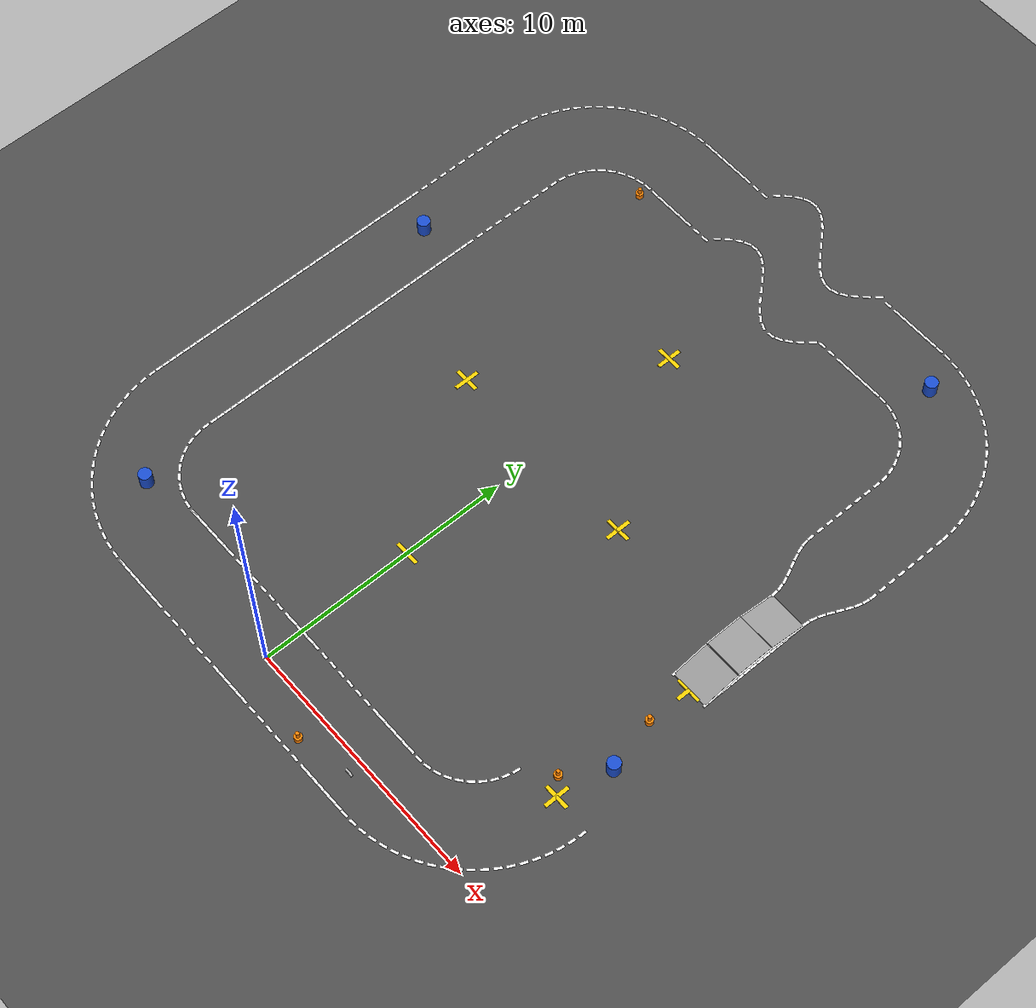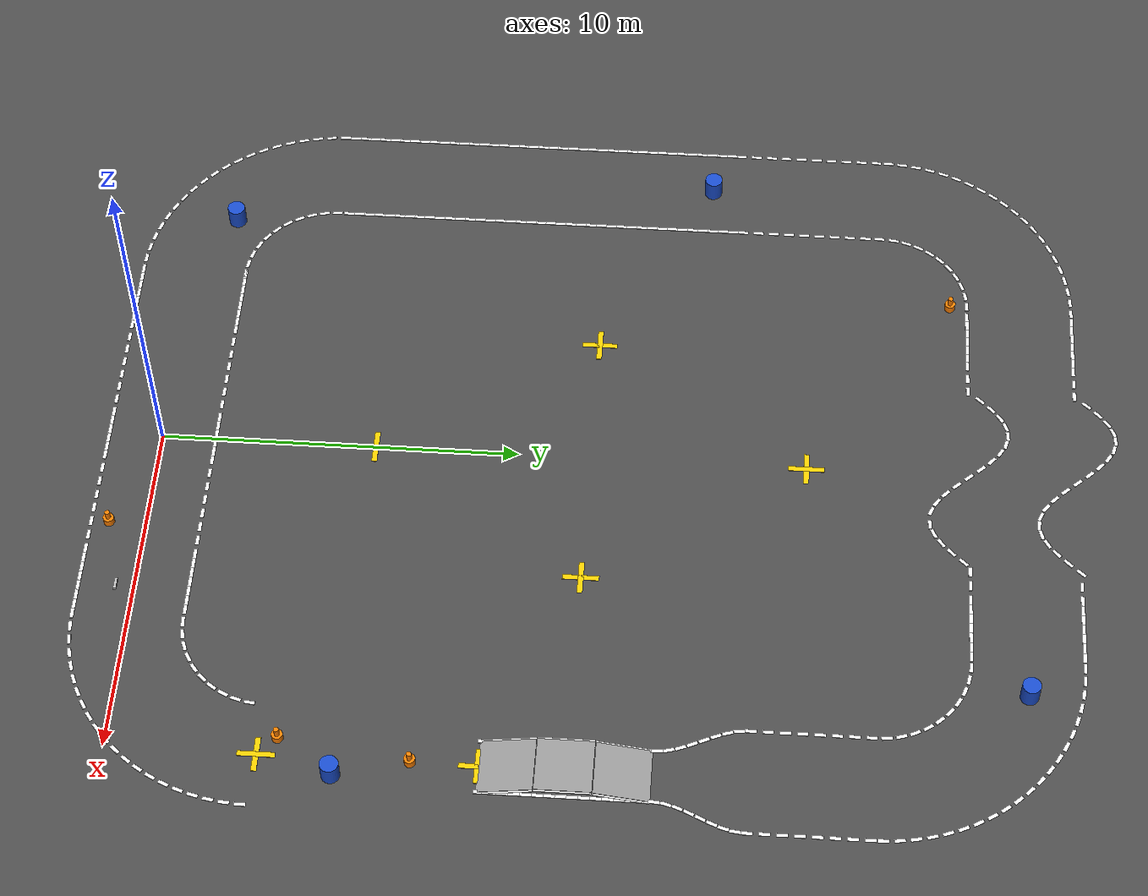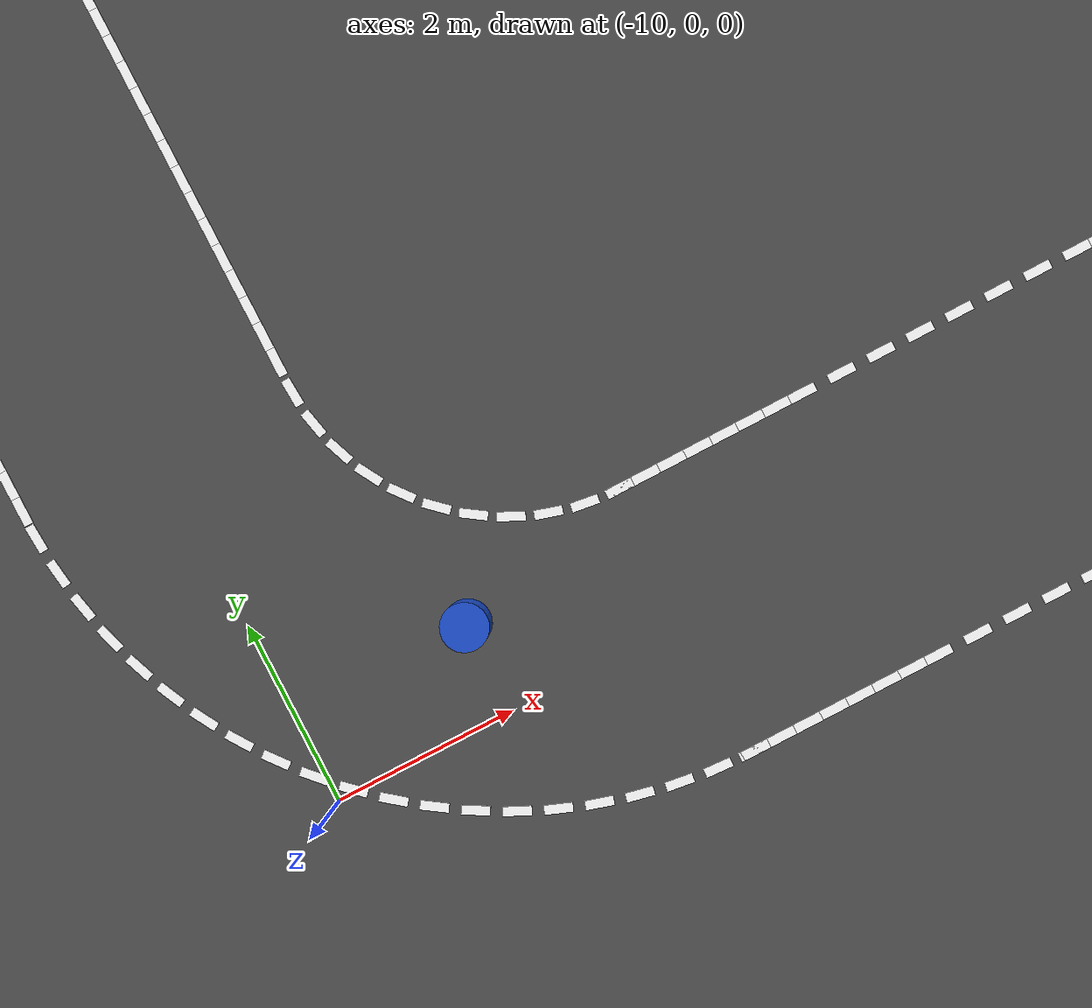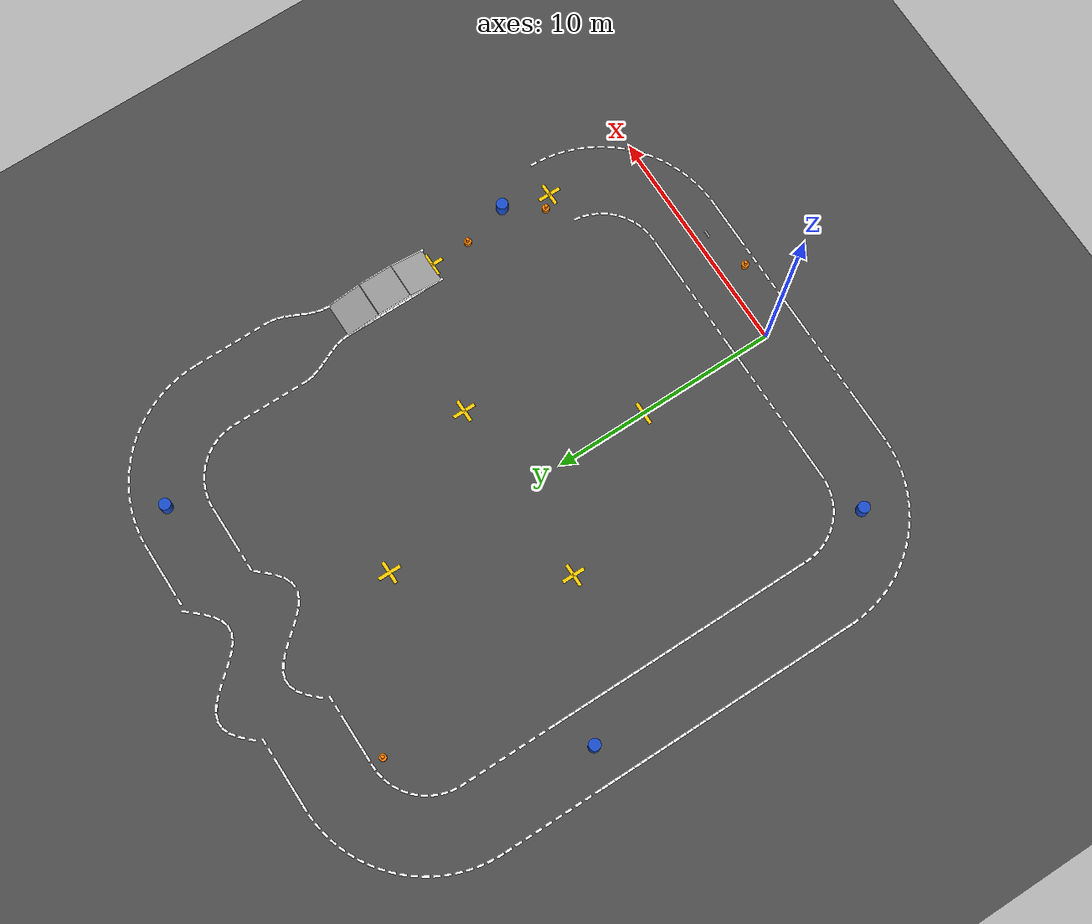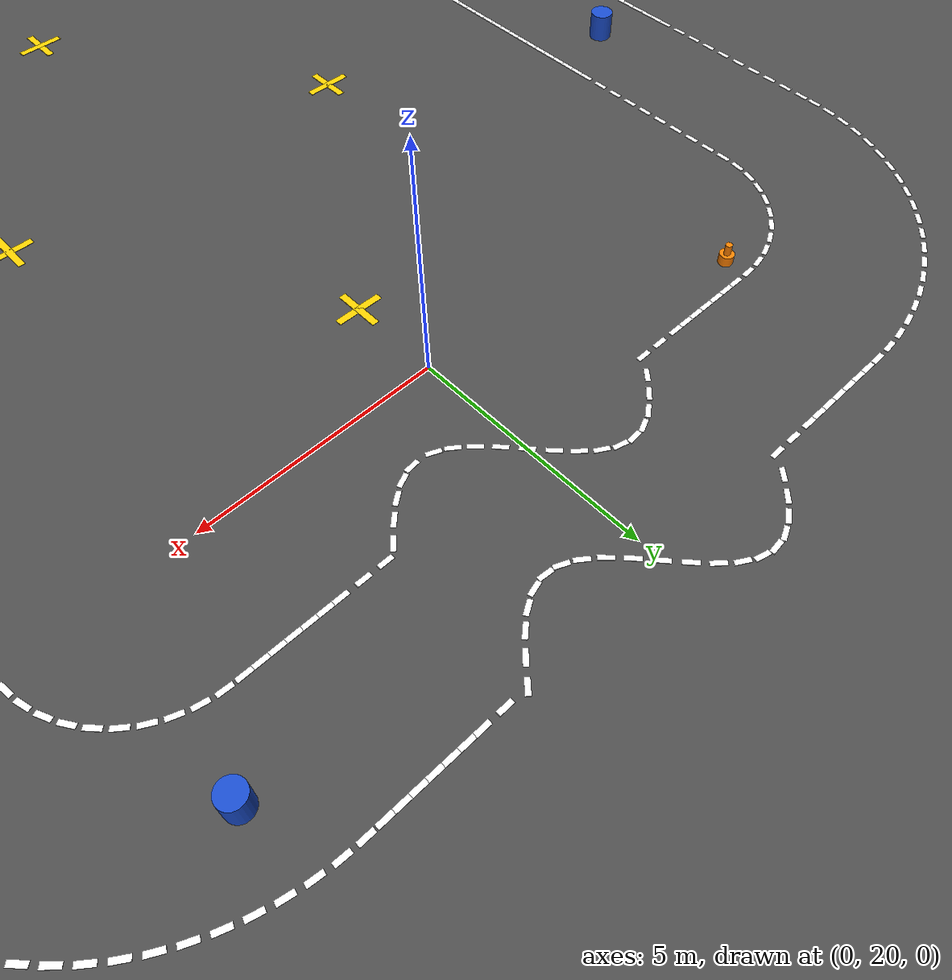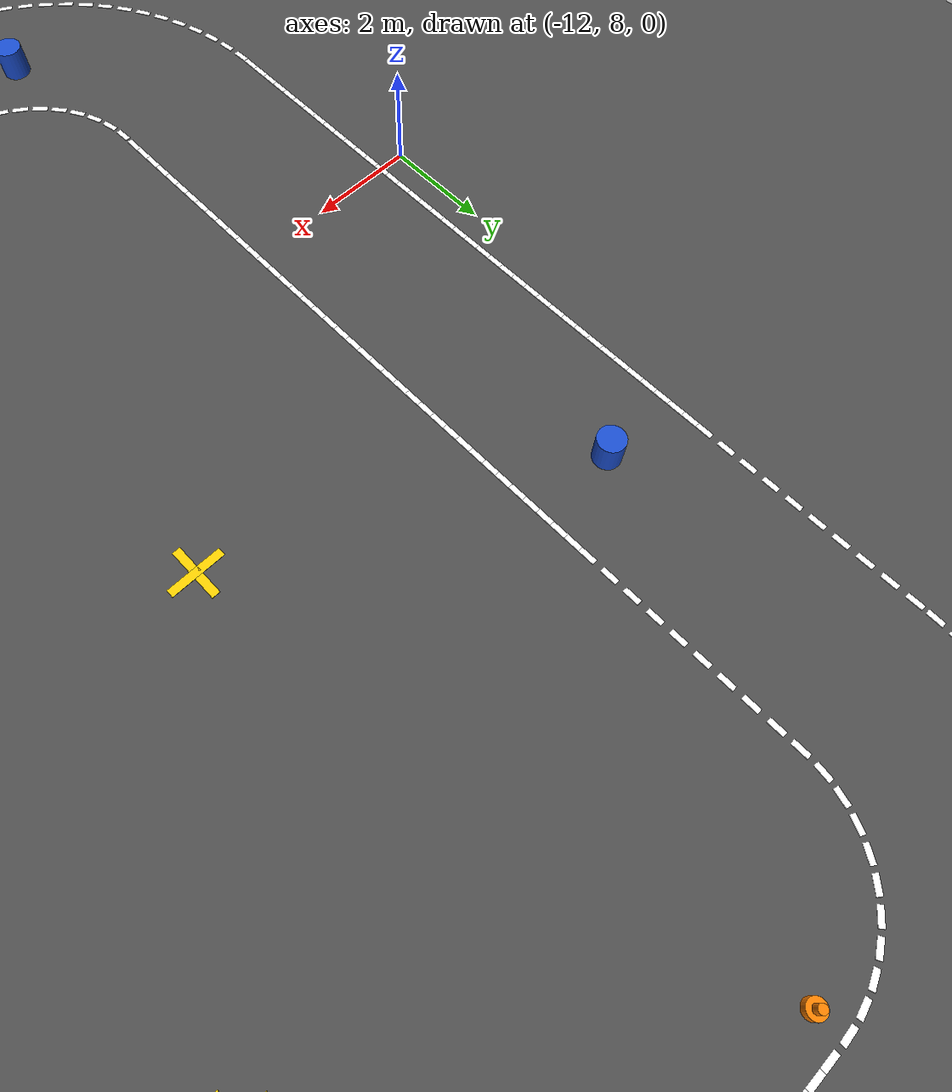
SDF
<sdf version="1.8">
 <world name="igvc_autonav">
  <physics name="dart_physics" type="dart">
   <max_step_size>0.006</max_step_size>
   <real_time_factor>1.0</real_time_factor>
  </physics>
  <spherical_coordinates>
   <surface_model>EARTH_WGS84</surface_model>
   <latitude_deg>42.6745</latitude_deg>
   <longitude_deg>-83.2187</longitude_deg>
   <elevation>282.0</elevation>
   <heading_deg>0</heading_deg>
  </spherical_coordinates>
  <plugin filename="ignition-gazebo-physics-system" name="ignition::gazebo::systems::Physics"/>
  <plugin filename="ignition-gazebo-sensors-system" name="ignition::gazebo::systems::Sensors">
   <render_engine>ogre</render_engine>
  </plugin>
  <plugin filename="ignition-gazebo-imu-system" name="ignition::gazebo::systems::Imu"/>
  <plugin filename="ignition-gazebo-navsat-system" name="ignition::gazebo::systems::NavSat"/>
  <plugin filename="ignition-gazebo-scene-broadcaster-system" name="ignition::gazebo::systems::SceneBroadcaster"/>
  <plugin filename="ignition-gazebo-user-commands-system" name="ignition::gazebo::systems::UserCommands"/>
  <light type="directional" name="sun">
   <pose>0 0 10 0 0 0</pose>
   <diffuse>0.9 0.9 0.9 1</diffuse>
   <specular>0.3 0.3 0.3 1</specular>
   <direction>-0.5 0.3 -0.9</direction>
  </light>
  <model name="ground_plane">
   <static>true</static>
   <link name="link">
    <collision name="collision">
     <geometry><plane><normal>0 0 1</normal><size>60 60</size></plane></geometry>
     <surface><friction><ode><mu>0.8</mu><mu2>0.8</mu2></ode></friction></surface>
    </collision>
    <visual name="visual">
     <geometry><plane><normal>0 0 1</normal><size>60 60</size></plane></geometry>
     <material>
      <ambient>0.25 0.25 0.25 1</ambient>
      <diffuse>0.3 0.3 0.3 1</diffuse>
      <specular>0.1 0.1 0.1 1</specular>
     </material>
    </visual>
   </link>
  </model>
  <model name="lane_inner_0">
   <static>true</static>
   <pose>-6.0000 1.5000 0.01 0 0 0.0000</pose>
   <link name="link">
    <visual name="visual">
     <geometry><box><size>0.3 0.1 0.01</size></box></geometry>
     <material><ambient>1 1 1 1</ambient><diffuse>1 1 1 1</diffuse><emissive>1 1 1 1</emissive></material>
    </visual>
   </link>
  </model>
  <model name="lane_inner_1">
   <static>true</static>
   <pose>-5.7000 1.5000 0.01 0 0 0.0000</pose>
   <link name="link">
    <visual name="visual">
     <geometry><box><size>0.3 0.1 0.01</size></box></geometry>
     <material><ambient>1 1 1 1</ambient><diffuse>1 1 1 1</diffuse><emissive>1 1 1 1</emissive></material>
    </visual>
   </link>
  </model>
  <model name="lane_inner_2">
   <static>true</static>
   <pose>-5.4000 1.5000 0.01 0 0 0.0000</pose>
   <link name="link">
    <visual name="visual">
     <geometry><box><size>0.3 0.1 0.01</size></box></geometry>
     <material><ambient>1 1 1 1</ambient><diffuse>1 1 1 1</diffuse><emissive>1 1 1 1</emissive></material>
    </visual>
   </link>
  </model>
  <model name="lane_inner_3">
   <static>true</static>
   <pose>-5.1000 1.5000 0.01 0 0 0.0000</pose>
   <link name="link">
    <visual name="visual">
     <geometry><box><size>0.3 0.1 0.01</size></box></geometry>
     <material><ambient>1 1 1 1</ambient><diffuse>1 1 1 1</diffuse><emissive>1 1 1 1</emissive></material>
    </visual>
   </link>
  </model>
  <model name="lane_inner_4">
   <static>true</static>
   <pose>-4.8000 1.5000 0.01 0 0 0.0000</pose>
   <link name="link">
    <visual name="visual">
     <geometry><box><size>0.3 0.1 0.01</size></box></geometry>
     <material><ambient>1 1 1 1</ambient><diffuse>1 1 1 1</diffuse><emissive>1 1 1 1</emissive></material>
    </visual>
   </link>
  </model>
  <model name="lane_inner_5">
   <static>true</static>
   <pose>-4.5000 1.5000 0.01 0 0 0.0000</pose>
   <link name="link">
    <visual name="visual">
     <geometry><box><size>0.3 0.1 0.01</size></box></geometry>
     <material><ambient>1 1 1 1</ambient><diffuse>1 1 1 1</diffuse><emissive>1 1 1 1</emissive></material>
    </visual>
   </link>
  </model>
  <model name="lane_inner_6">
   <static>true</static>
   <pose>-4.2000 1.5000 0.01 0 0 0.0000</pose>
   <link name="link">
    <visual name="visual">
     <geometry><box><size>0.3 0.1 0.01</size></box></geometry>
     <material><ambient>1 1 1 1</ambient><diffuse>1 1 1 1</diffuse><emissive>1 1 1 1</emissive></material>
    </visual>
   </link>
  </model>
  <model name="lane_inner_7">
   <static>true</static>
   <pose>-3.9000 1.5000 0.01 0 0 0.0000</pose>
   <link name="link">
    <visual name="visual">
     <geometry><box><size>0.3 0.1 0.01</size></box></geometry>
     <material><ambient>1 1 1 1</ambient><diffuse>1 1 1 1</diffuse><emissive>1 1 1 1</emissive></material>
    </visual>
   </link>
  </model>
  <model name="lane_inner_8">
   <static>true</static>
   <pose>-3.4500 1.5000 0.01 0 0 0.0000</pose>
   <link name="link">
    <visual name="visual">
     <geometry><box><size>0.3 0.1 0.01</size></box></geometry>
     <material><ambient>1 1 1 1</ambient><diffuse>1 1 1 1</diffuse><emissive>1 1 1 1</emissive></material>
    </visual>
   </link>
  </model>
  <model name="lane_inner_9">
   <static>true</static>
   <pose>-3.0000 1.5000 0.01 0 0 0.0000</pose>
   <link name="link">
    <visual name="visual">
     <geometry><box><size>0.3 0.1 0.01</size></box></geometry>
     <material><ambient>1 1 1 1</ambient><diffuse>1 1 1 1</diffuse><emissive>1 1 1 1</emissive></material>
    </visual>
   </link>
  </model>
  <model name="lane_inner_10">
   <static>true</static>
   <pose>-2.5500 1.5000 0.01 0 0 0.0000</pose>
   <link name="link">
    <visual name="visual">
     <geometry><box><size>0.3 0.1 0.01</size></box></geometry>
     <material><ambient>1 1 1 1</ambient><diffuse>1 1 1 1</diffuse><emissive>1 1 1 1</emissive></material>
    </visual>
   </link>
  </model>
  <model name="lane_inner_11">
   <static>true</static>
   <pose>-2.1000 1.5000 0.01 0 0 0.0000</pose>
   <link name="link">
    <visual name="visual">
     <geometry><box><size>0.3 0.1 0.01</size></box></geometry>
     <material><ambient>1 1 1 1</ambient><diffuse>1 1 1 1</diffuse><emissive>1 1 1 1</emissive></material>
    </visual>
   </link>
  </model>
  <model name="lane_inner_12">
   <static>true</static>
   <pose>-1.6500 1.5000 0.01 0 0 0.0000</pose>
   <link name="link">
    <visual name="visual">
     <geometry><box><size>0.3 0.1 0.01</size></box></geometry>
     <material><ambient>1 1 1 1</ambient><diffuse>1 1 1 1</diffuse><emissive>1 1 1 1</emissive></material>
    </visual>
   </link>
  </model>
  <model name="lane_inner_13">
   <static>true</static>
   <pose>-1.2000 1.5000 0.01 0 0 0.0000</pose>
   <link name="link">
    <visual name="visual">
     <geometry><box><size>0.3 0.1 0.01</size></box></geometry>
     <material><ambient>1 1 1 1</ambient><diffuse>1 1 1 1</diffuse><emissive>1 1 1 1</emissive></material>
    </visual>
   </link>
  </model>
  <model name="lane_inner_14">
   <static>true</static>
   <pose>-0.7500 1.5000 0.01 0 0 0.0000</pose>
   <link name="link">
    <visual name="visual">
     <geometry><box><size>0.3 0.1 0.01</size></box></geometry>
     <material><ambient>1 1 1 1</ambient><diffuse>1 1 1 1</diffuse><emissive>1 1 1 1</emissive></material>
    </visual>
   </link>
  </model>
  <model name="lane_inner_15">
   <static>true</static>
   <pose>-0.4500 1.5000 0.01 0 0 0.0000</pose>
   <link name="link">
    <visual name="visual">
     <geometry><box><size>0.3 0.1 0.01</size></box></geometry>
     <material><ambient>1 1 1 1</ambient><diffuse>1 1 1 1</diffuse><emissive>1 1 1 1</emissive></material>
    </visual>
   </link>
  </model>
  <model name="lane_inner_16">
   <static>true</static>
   <pose>-0.1500 1.5000 0.01 0 0 0.0000</pose>
   <link name="link">
    <visual name="visual">
     <geometry><box><size>0.3 0.1 0.01</size></box></geometry>
     <material><ambient>1 1 1 1</ambient><diffuse>1 1 1 1</diffuse><emissive>1 1 1 1</emissive></material>
    </visual>
   </link>
  </model>
  <model name="lane_inner_17">
   <static>true</static>
   <pose>0.1500 1.5000 0.01 0 0 0.0000</pose>
   <link name="link">
    <visual name="visual">
     <geometry><box><size>0.3 0.1 0.01</size></box></geometry>
     <material><ambient>1 1 1 1</ambient><diffuse>1 1 1 1</diffuse><emissive>1 1 1 1</emissive></material>
    </visual>
   </link>
  </model>
  <model name="lane_inner_18">
   <static>true</static>
   <pose>0.4500 1.5000 0.01 0 0 0.0000</pose>
   <link name="link">
    <visual name="visual">
     <geometry><box><size>0.3 0.1 0.01</size></box></geometry>
     <material><ambient>1 1 1 1</ambient><diffuse>1 1 1 1</diffuse><emissive>1 1 1 1</emissive></material>
    </visual>
   </link>
  </model>
  <model name="lane_inner_19">
   <static>true</static>
   <pose>0.7500 1.5000 0.01 0 0 0.0000</pose>
   <link name="link">
    <visual name="visual">
     <geometry><box><size>0.3 0.1 0.01</size></box></geometry>
     <material><ambient>1 1 1 1</ambient><diffuse>1 1 1 1</diffuse><emissive>1 1 1 1</emissive></material>
    </visual>
   </link>
  </model>
  <model name="lane_inner_20">
   <static>true</static>
   <pose>1.2000 1.5000 0.01 0 0 0.0000</pose>
   <link name="link">
    <visual name="visual">
     <geometry><box><size>0.3 0.1 0.01</size></box></geometry>
     <material><ambient>1 1 1 1</ambient><diffuse>1 1 1 1</diffuse><emissive>1 1 1 1</emissive></material>
    </visual>
   </link>
  </model>
  <model name="lane_inner_21">
   <static>true</static>
   <pose>1.6500 1.5000 0.01 0 0 0.0000</pose>
   <link name="link">
    <visual name="visual">
     <geometry><box><size>0.3 0.1 0.01</size></box></geometry>
     <material><ambient>1 1 1 1</ambient><diffuse>1 1 1 1</diffuse><emissive>1 1 1 1</emissive></material>
    </visual>
   </link>
  </model>
  <model name="lane_inner_22">
   <static>true</static>
   <pose>2.1000 1.5000 0.01 0 0 0.0000</pose>
   <link name="link">
    <visual name="visual">
     <geometry><box><size>0.3 0.1 0.01</size></box></geometry>
     <material><ambient>1 1 1 1</ambient><diffuse>1 1 1 1</diffuse><emissive>1 1 1 1</emissive></material>
    </visual>
   </link>
  </model>
  <model name="lane_inner_23">
   <static>true</static>
   <pose>2.5500 1.5000 0.01 0 0 0.0000</pose>
   <link name="link">
    <visual name="visual">
     <geometry><box><size>0.3 0.1 0.01</size></box></geometry>
     <material><ambient>1 1 1 1</ambient><diffuse>1 1 1 1</diffuse><emissive>1 1 1 1</emissive></material>
    </visual>
   </link>
  </model>
  <model name="lane_inner_24">
   <static>true</static>
   <pose>3.0000 1.5000 0.01 0 0 0.0000</pose>
   <link name="link">
    <visual name="visual">
     <geometry><box><size>0.3 0.1 0.01</size></box></geometry>
     <material><ambient>1 1 1 1</ambient><diffuse>1 1 1 1</diffuse><emissive>1 1 1 1</emissive></material>
    </visual>
   </link>
  </model>
  <model name="lane_inner_25">
   <static>true</static>
   <pose>3.4500 1.5000 0.01 0 0 0.0000</pose>
   <link name="link">
    <visual name="visual">
     <geometry><box><size>0.3 0.1 0.01</size></box></geometry>
     <material><ambient>1 1 1 1</ambient><diffuse>1 1 1 1</diffuse><emissive>1 1 1 1</emissive></material>
    </visual>
   </link>
  </model>
  <model name="lane_inner_26">
   <static>true</static>
   <pose>3.9000 1.5000 0.01 0 0 0.0000</pose>
   <link name="link">
    <visual name="visual">
     <geometry><box><size>0.3 0.1 0.01</size></box></geometry>
     <material><ambient>1 1 1 1</ambient><diffuse>1 1 1 1</diffuse><emissive>1 1 1 1</emissive></material>
    </visual>
   </link>
  </model>
  <model name="lane_inner_27">
   <static>true</static>
   <pose>4.2000 1.5000 0.01 0 0 0.0000</pose>
   <link name="link">
    <visual name="visual">
     <geometry><box><size>0.3 0.1 0.01</size></box></geometry>
     <material><ambient>1 1 1 1</ambient><diffuse>1 1 1 1</diffuse><emissive>1 1 1 1</emissive></material>
    </visual>
   </link>
  </model>
  <model name="lane_inner_28">
   <static>true</static>
   <pose>4.5000 1.5000 0.01 0 0 0.0000</pose>
   <link name="link">
    <visual name="visual">
     <geometry><box><size>0.3 0.1 0.01</size></box></geometry>
     <material><ambient>1 1 1 1</ambient><diffuse>1 1 1 1</diffuse><emissive>1 1 1 1</emissive></material>
    </visual>
   </link>
  </model>
  <model name="lane_inner_29">
   <static>true</static>
   <pose>4.8000 1.5000 0.01 0 0 0.0000</pose>
   <link name="link">
    <visual name="visual">
     <geometry><box><size>0.3 0.1 0.01</size></box></geometry>
     <material><ambient>1 1 1 1</ambient><diffuse>1 1 1 1</diffuse><emissive>1 1 1 1</emissive></material>
    </visual>
   </link>
  </model>
  <model name="lane_inner_30">
   <static>true</static>
   <pose>5.1000 1.5000 0.01 0 0 0.0000</pose>
   <link name="link">
    <visual name="visual">
     <geometry><box><size>0.3 0.1 0.01</size></box></geometry>
     <material><ambient>1 1 1 1</ambient><diffuse>1 1 1 1</diffuse><emissive>1 1 1 1</emissive></material>
    </visual>
   </link>
  </model>
  <model name="lane_inner_31">
   <static>true</static>
   <pose>5.4000 1.5000 0.01 0 0 0.0000</pose>
   <link name="link">
    <visual name="visual">
     <geometry><box><size>0.3 0.1 0.01</size></box></geometry>
     <material><ambient>1 1 1 1</ambient><diffuse>1 1 1 1</diffuse><emissive>1 1 1 1</emissive></material>
    </visual>
   </link>
  </model>
  <model name="lane_inner_32">
   <static>true</static>
   <pose>5.7000 1.5000 0.01 0 0 0.0000</pose>
   <link name="link">
    <visual name="visual">
     <geometry><box><size>0.3 0.1 0.01</size></box></geometry>
     <material><ambient>1 1 1 1</ambient><diffuse>1 1 1 1</diffuse><emissive>1 1 1 1</emissive></material>
    </visual>
   </link>
  </model>
  <model name="lane_inner_33">
   <static>true</static>
   <pose>6.0958 1.5018 0.01 0 0 0.0575</pose>
   <link name="link">
    <visual name="visual">
     <geometry><box><size>0.3 0.1 0.01</size></box></geometry>
     <material><ambient>1 1 1 1</ambient><diffuse>1 1 1 1</diffuse><emissive>1 1 1 1</emissive></material>
    </visual>
   </link>
  </model>
  <model name="lane_inner_34">
   <static>true</static>
   <pose>6.4760 1.5457 0.01 0 0 0.2107</pose>
   <link name="link">
    <visual name="visual">
     <geometry><box><size>0.3 0.1 0.01</size></box></geometry>
     <material><ambient>1 1 1 1</ambient><diffuse>1 1 1 1</diffuse><emissive>1 1 1 1</emissive></material>
    </visual>
   </link>
  </model>
  <model name="lane_inner_35">
   <static>true</static>
   <pose>6.8450 1.6471 0.01 0 0 0.3640</pose>
   <link name="link">
    <visual name="visual">
     <geometry><box><size>0.3 0.1 0.01</size></box></geometry>
     <material><ambient>1 1 1 1</ambient><diffuse>1 1 1 1</diffuse><emissive>1 1 1 1</emissive></material>
    </visual>
   </link>
  </model>
  <model name="lane_inner_36">
   <static>true</static>
   <pose>7.1943 1.8037 0.01 0 0 0.5172</pose>
   <link name="link">
    <visual name="visual">
     <geometry><box><size>0.3 0.1 0.01</size></box></geometry>
     <material><ambient>1 1 1 1</ambient><diffuse>1 1 1 1</diffuse><emissive>1 1 1 1</emissive></material>
    </visual>
   </link>
  </model>
  <model name="lane_inner_37">
   <static>true</static>
   <pose>7.5156 2.0118 0.01 0 0 0.6705</pose>
   <link name="link">
    <visual name="visual">
     <geometry><box><size>0.3 0.1 0.01</size></box></geometry>
     <material><ambient>1 1 1 1</ambient><diffuse>1 1 1 1</diffuse><emissive>1 1 1 1</emissive></material>
    </visual>
   </link>
  </model>
  <model name="lane_inner_38">
   <static>true</static>
   <pose>7.8013 2.2664 0.01 0 0 0.8237</pose>
   <link name="link">
    <visual name="visual">
     <geometry><box><size>0.3 0.1 0.01</size></box></geometry>
     <material><ambient>1 1 1 1</ambient><diffuse>1 1 1 1</diffuse><emissive>1 1 1 1</emissive></material>
    </visual>
   </link>
  </model>
  <model name="lane_inner_39">
   <static>true</static>
   <pose>8.0448 2.5617 0.01 0 0 0.9770</pose>
   <link name="link">
    <visual name="visual">
     <geometry><box><size>0.3 0.1 0.01</size></box></geometry>
     <material><ambient>1 1 1 1</ambient><diffuse>1 1 1 1</diffuse><emissive>1 1 1 1</emissive></material>
    </visual>
   </link>
  </model>
  <model name="lane_inner_40">
   <static>true</static>
   <pose>8.2404 2.8907 0.01 0 0 1.1302</pose>
   <link name="link">
    <visual name="visual">
     <geometry><box><size>0.3 0.1 0.01</size></box></geometry>
     <material><ambient>1 1 1 1</ambient><diffuse>1 1 1 1</diffuse><emissive>1 1 1 1</emissive></material>
    </visual>
   </link>
  </model>
  <model name="lane_inner_41">
   <static>true</static>
   <pose>8.3835 3.2457 0.01 0 0 1.2835</pose>
   <link name="link">
    <visual name="visual">
     <geometry><box><size>0.3 0.1 0.01</size></box></geometry>
     <material><ambient>1 1 1 1</ambient><diffuse>1 1 1 1</diffuse><emissive>1 1 1 1</emissive></material>
    </visual>
   </link>
  </model>
  <model name="lane_inner_42">
   <static>true</static>
   <pose>8.4707 3.6184 0.01 0 0 1.4367</pose>
   <link name="link">
    <visual name="visual">
     <geometry><box><size>0.3 0.1 0.01</size></box></geometry>
     <material><ambient>1 1 1 1</ambient><diffuse>1 1 1 1</diffuse><emissive>1 1 1 1</emissive></material>
    </visual>
   </link>
  </model>
  <model name="lane_inner_43">
   <static>true</static>
   <pose>9.2500 9.8500 0.01 0 0 1.5708</pose>
   <link name="link">
    <visual name="visual">
     <geometry><box><size>0.3 0.1 0.01</size></box></geometry>
     <material><ambient>1 1 1 1</ambient><diffuse>1 1 1 1</diffuse><emissive>1 1 1 1</emissive></material>
    </visual>
   </link>
  </model>
  <model name="lane_inner_44">
   <static>true</static>
   <pose>9.2500 10.1500 0.01 0 0 1.5708</pose>
   <link name="link">
    <visual name="visual">
     <geometry><box><size>0.3 0.1 0.01</size></box></geometry>
     <material><ambient>1 1 1 1</ambient><diffuse>1 1 1 1</diffuse><emissive>1 1 1 1</emissive></material>
    </visual>
   </link>
  </model>
  <model name="lane_inner_45">
   <static>true</static>
   <pose>9.2500 10.4500 0.01 0 0 1.5708</pose>
   <link name="link">
    <visual name="visual">
     <geometry><box><size>0.3 0.1 0.01</size></box></geometry>
     <material><ambient>1 1 1 1</ambient><diffuse>1 1 1 1</diffuse><emissive>1 1 1 1</emissive></material>
    </visual>
   </link>
  </model>
  <model name="lane_inner_46">
   <static>true</static>
   <pose>9.2500 10.7500 0.01 0 0 1.5708</pose>
   <link name="link">
    <visual name="visual">
     <geometry><box><size>0.3 0.1 0.01</size></box></geometry>
     <material><ambient>1 1 1 1</ambient><diffuse>1 1 1 1</diffuse><emissive>1 1 1 1</emissive></material>
    </visual>
   </link>
  </model>
  <model name="lane_inner_47">
   <static>true</static>
   <pose>9.2500 11.0500 0.01 0 0 1.5708</pose>
   <link name="link">
    <visual name="visual">
     <geometry><box><size>0.3 0.1 0.01</size></box></geometry>
     <material><ambient>1 1 1 1</ambient><diffuse>1 1 1 1</diffuse><emissive>1 1 1 1</emissive></material>
    </visual>
   </link>
  </model>
  <model name="lane_inner_48">
   <static>true</static>
   <pose>9.2500 11.3500 0.01 0 0 1.5708</pose>
   <link name="link">
    <visual name="visual">
     <geometry><box><size>0.3 0.1 0.01</size></box></geometry>
     <material><ambient>1 1 1 1</ambient><diffuse>1 1 1 1</diffuse><emissive>1 1 1 1</emissive></material>
    </visual>
   </link>
  </model>
  <model name="lane_inner_49">
   <static>true</static>
   <pose>9.2500 11.6500 0.01 0 0 1.5708</pose>
   <link name="link">
    <visual name="visual">
     <geometry><box><size>0.3 0.1 0.01</size></box></geometry>
     <material><ambient>1 1 1 1</ambient><diffuse>1 1 1 1</diffuse><emissive>1 1 1 1</emissive></material>
    </visual>
   </link>
  </model>
  <model name="lane_inner_50">
   <static>true</static>
   <pose>9.2500 11.9500 0.01 0 0 1.5708</pose>
   <link name="link">
    <visual name="visual">
     <geometry><box><size>0.3 0.1 0.01</size></box></geometry>
     <material><ambient>1 1 1 1</ambient><diffuse>1 1 1 1</diffuse><emissive>1 1 1 1</emissive></material>
    </visual>
   </link>
  </model>
  <model name="lane_inner_51">
   <static>true</static>
   <pose>9.2500 12.2500 0.01 0 0 1.5708</pose>
   <link name="link">
    <visual name="visual">
     <geometry><box><size>0.3 0.1 0.01</size></box></geometry>
     <material><ambient>1 1 1 1</ambient><diffuse>1 1 1 1</diffuse><emissive>1 1 1 1</emissive></material>
    </visual>
   </link>
  </model>
  <model name="lane_inner_52">
   <static>true</static>
   <pose>9.2500 12.5500 0.01 0 0 1.5708</pose>
   <link name="link">
    <visual name="visual">
     <geometry><box><size>0.3 0.1 0.01</size></box></geometry>
     <material><ambient>1 1 1 1</ambient><diffuse>1 1 1 1</diffuse><emissive>1 1 1 1</emissive></material>
    </visual>
   </link>
  </model>
  <model name="lane_inner_53">
   <static>true</static>
   <pose>9.2500 12.8500 0.01 0 0 1.5708</pose>
   <link name="link">
    <visual name="visual">
     <geometry><box><size>0.3 0.1 0.01</size></box></geometry>
     <material><ambient>1 1 1 1</ambient><diffuse>1 1 1 1</diffuse><emissive>1 1 1 1</emissive></material>
    </visual>
   </link>
  </model>
  <model name="lane_inner_54">
   <static>true</static>
   <pose>9.2500 13.1500 0.01 0 0 1.5708</pose>
   <link name="link">
    <visual name="visual">
     <geometry><box><size>0.3 0.1 0.01</size></box></geometry>
     <material><ambient>1 1 1 1</ambient><diffuse>1 1 1 1</diffuse><emissive>1 1 1 1</emissive></material>
    </visual>
   </link>
  </model>
  <model name="lane_inner_55">
   <static>true</static>
   <pose>9.2500 13.4500 0.01 0 0 1.5708</pose>
   <link name="link">
    <visual name="visual">
     <geometry><box><size>0.3 0.1 0.01</size></box></geometry>
     <material><ambient>1 1 1 1</ambient><diffuse>1 1 1 1</diffuse><emissive>1 1 1 1</emissive></material>
    </visual>
   </link>
  </model>
  <model name="lane_inner_56">
   <static>true</static>
   <pose>9.2500 13.7500 0.01 0 0 1.5708</pose>
   <link name="link">
    <visual name="visual">
     <geometry><box><size>0.3 0.1 0.01</size></box></geometry>
     <material><ambient>1 1 1 1</ambient><diffuse>1 1 1 1</diffuse><emissive>1 1 1 1</emissive></material>
    </visual>
   </link>
  </model>
  <model name="lane_inner_57">
   <static>true</static>
   <pose>9.2500 14.0500 0.01 0 0 1.5708</pose>
   <link name="link">
    <visual name="visual">
     <geometry><box><size>0.3 0.1 0.01</size></box></geometry>
     <material><ambient>1 1 1 1</ambient><diffuse>1 1 1 1</diffuse><emissive>1 1 1 1</emissive></material>
    </visual>
   </link>
  </model>
  <model name="lane_inner_58">
   <static>true</static>
   <pose>9.2470 14.3500 0.01 0 0 1.6731</pose>
   <link name="link">
    <visual name="visual">
     <geometry><box><size>0.3 0.1 0.01</size></box></geometry>
     <material><ambient>1 1 1 1</ambient><diffuse>1 1 1 1</diffuse><emissive>1 1 1 1</emissive></material>
    </visual>
   </link>
  </model>
  <model name="lane_inner_59">
   <static>true</static>
   <pose>9.2036 14.6500 0.01 0 0 1.8294</pose>
   <link name="link">
    <visual name="visual">
     <geometry><box><size>0.3 0.1 0.01</size></box></geometry>
     <material><ambient>1 1 1 1</ambient><diffuse>1 1 1 1</diffuse><emissive>1 1 1 1</emissive></material>
    </visual>
   </link>
  </model>
  <model name="lane_inner_60">
   <static>true</static>
   <pose>9.1140 14.9500 0.01 0 0 1.9419</pose>
   <link name="link">
    <visual name="visual">
     <geometry><box><size>0.3 0.1 0.01</size></box></geometry>
     <material><ambient>1 1 1 1</ambient><diffuse>1 1 1 1</diffuse><emissive>1 1 1 1</emissive></material>
    </visual>
   </link>
  </model>
  <model name="lane_inner_61">
   <static>true</static>
   <pose>8.9909 15.2500 0.01 0 0 2.0013</pose>
   <link name="link">
    <visual name="visual">
     <geometry><box><size>0.3 0.1 0.01</size></box></geometry>
     <material><ambient>1 1 1 1</ambient><diffuse>1 1 1 1</diffuse><emissive>1 1 1 1</emissive></material>
    </visual>
   </link>
  </model>
  <model name="lane_inner_62">
   <static>true</static>
   <pose>8.8515 15.5500 0.01 0 0 2.0058</pose>
   <link name="link">
    <visual name="visual">
     <geometry><box><size>0.3 0.1 0.01</size></box></geometry>
     <material><ambient>1 1 1 1</ambient><diffuse>1 1 1 1</diffuse><emissive>1 1 1 1</emissive></material>
    </visual>
   </link>
  </model>
  <model name="lane_inner_63">
   <static>true</static>
   <pose>8.7153 15.8500 0.01 0 0 1.9556</pose>
   <link name="link">
    <visual name="visual">
     <geometry><box><size>0.3 0.1 0.01</size></box></geometry>
     <material><ambient>1 1 1 1</ambient><diffuse>1 1 1 1</diffuse><emissive>1 1 1 1</emissive></material>
    </visual>
   </link>
  </model>
  <model name="lane_inner_64">
   <static>true</static>
   <pose>8.6016 16.1500 0.01 0 0 1.8516</pose>
   <link name="link">
    <visual name="visual">
     <geometry><box><size>0.3 0.1 0.01</size></box></geometry>
     <material><ambient>1 1 1 1</ambient><diffuse>1 1 1 1</diffuse><emissive>1 1 1 1</emissive></material>
    </visual>
   </link>
  </model>
  <model name="lane_inner_65">
   <static>true</static>
   <pose>8.5263 16.4500 0.01 0 0 1.7013</pose>
   <link name="link">
    <visual name="visual">
     <geometry><box><size>0.3 0.1 0.01</size></box></geometry>
     <material><ambient>1 1 1 1</ambient><diffuse>1 1 1 1</diffuse><emissive>1 1 1 1</emissive></material>
    </visual>
   </link>
  </model>
  <model name="lane_inner_66">
   <static>true</static>
   <pose>8.5000 16.7500 0.01 0 0 1.5708</pose>
   <link name="link">
    <visual name="visual">
     <geometry><box><size>0.3 0.1 0.01</size></box></geometry>
     <material><ambient>1 1 1 1</ambient><diffuse>1 1 1 1</diffuse><emissive>1 1 1 1</emissive></material>
    </visual>
   </link>
  </model>
  <model name="lane_inner_67">
   <static>true</static>
   <pose>8.5000 17.2000 0.01 0 0 1.5708</pose>
   <link name="link">
    <visual name="visual">
     <geometry><box><size>0.3 0.1 0.01</size></box></geometry>
     <material><ambient>1 1 1 1</ambient><diffuse>1 1 1 1</diffuse><emissive>1 1 1 1</emissive></material>
    </visual>
   </link>
  </model>
  <model name="lane_inner_68">
   <static>true</static>
   <pose>8.5000 17.6500 0.01 0 0 1.5708</pose>
   <link name="link">
    <visual name="visual">
     <geometry><box><size>0.3 0.1 0.01</size></box></geometry>
     <material><ambient>1 1 1 1</ambient><diffuse>1 1 1 1</diffuse><emissive>1 1 1 1</emissive></material>
    </visual>
   </link>
  </model>
  <model name="lane_inner_69">
   <static>true</static>
   <pose>8.5000 18.1000 0.01 0 0 1.5708</pose>
   <link name="link">
    <visual name="visual">
     <geometry><box><size>0.3 0.1 0.01</size></box></geometry>
     <material><ambient>1 1 1 1</ambient><diffuse>1 1 1 1</diffuse><emissive>1 1 1 1</emissive></material>
    </visual>
   </link>
  </model>
  <model name="lane_inner_70">
   <static>true</static>
   <pose>8.5000 18.5500 0.01 0 0 1.5708</pose>
   <link name="link">
    <visual name="visual">
     <geometry><box><size>0.3 0.1 0.01</size></box></geometry>
     <material><ambient>1 1 1 1</ambient><diffuse>1 1 1 1</diffuse><emissive>1 1 1 1</emissive></material>
    </visual>
   </link>
  </model>
  <model name="lane_inner_71">
   <static>true</static>
   <pose>8.5000 19.0000 0.01 0 0 1.5708</pose>
   <link name="link">
    <visual name="visual">
     <geometry><box><size>0.3 0.1 0.01</size></box></geometry>
     <material><ambient>1 1 1 1</ambient><diffuse>1 1 1 1</diffuse><emissive>1 1 1 1</emissive></material>
    </visual>
   </link>
  </model>
  <model name="lane_inner_72">
   <static>true</static>
   <pose>8.5000 19.4500 0.01 0 0 1.5708</pose>
   <link name="link">
    <visual name="visual">
     <geometry><box><size>0.3 0.1 0.01</size></box></geometry>
     <material><ambient>1 1 1 1</ambient><diffuse>1 1 1 1</diffuse><emissive>1 1 1 1</emissive></material>
    </visual>
   </link>
  </model>
  <model name="lane_inner_73">
   <static>true</static>
   <pose>8.5000 19.9000 0.01 0 0 1.5696</pose>
   <link name="link">
    <visual name="visual">
     <geometry><box><size>0.3 0.1 0.01</size></box></geometry>
     <material><ambient>1 1 1 1</ambient><diffuse>1 1 1 1</diffuse><emissive>1 1 1 1</emissive></material>
    </visual>
   </link>
  </model>
  <model name="lane_inner_74">
   <static>true</static>
   <pose>8.4835 20.2867 0.01 0 0 1.7049</pose>
   <link name="link">
    <visual name="visual">
     <geometry><box><size>0.3 0.1 0.01</size></box></geometry>
     <material><ambient>1 1 1 1</ambient><diffuse>1 1 1 1</diffuse><emissive>1 1 1 1</emissive></material>
    </visual>
   </link>
  </model>
  <model name="lane_inner_75">
   <static>true</static>
   <pose>8.4106 20.6625 0.01 0 0 1.8581</pose>
   <link name="link">
    <visual name="visual">
     <geometry><box><size>0.3 0.1 0.01</size></box></geometry>
     <material><ambient>1 1 1 1</ambient><diffuse>1 1 1 1</diffuse><emissive>1 1 1 1</emissive></material>
    </visual>
   </link>
  </model>
  <model name="lane_inner_76">
   <static>true</static>
   <pose>8.2813 21.0227 0.01 0 0 2.0114</pose>
   <link name="link">
    <visual name="visual">
     <geometry><box><size>0.3 0.1 0.01</size></box></geometry>
     <material><ambient>1 1 1 1</ambient><diffuse>1 1 1 1</diffuse><emissive>1 1 1 1</emissive></material>
    </visual>
   </link>
  </model>
  <model name="lane_inner_77">
   <static>true</static>
   <pose>8.0984 21.3589 0.01 0 0 2.1646</pose>
   <link name="link">
    <visual name="visual">
     <geometry><box><size>0.3 0.1 0.01</size></box></geometry>
     <material><ambient>1 1 1 1</ambient><diffuse>1 1 1 1</diffuse><emissive>1 1 1 1</emissive></material>
    </visual>
   </link>
  </model>
  <model name="lane_inner_78">
   <static>true</static>
   <pose>7.8664 21.6633 0.01 0 0 2.3179</pose>
   <link name="link">
    <visual name="visual">
     <geometry><box><size>0.3 0.1 0.01</size></box></geometry>
     <material><ambient>1 1 1 1</ambient><diffuse>1 1 1 1</diffuse><emissive>1 1 1 1</emissive></material>
    </visual>
   </link>
  </model>
  <model name="lane_inner_79">
   <static>true</static>
   <pose>7.5906 21.9287 0.01 0 0 2.4711</pose>
   <link name="link">
    <visual name="visual">
     <geometry><box><size>0.3 0.1 0.01</size></box></geometry>
     <material><ambient>1 1 1 1</ambient><diffuse>1 1 1 1</diffuse><emissive>1 1 1 1</emissive></material>
    </visual>
   </link>
  </model>
  <model name="lane_inner_80">
   <static>true</static>
   <pose>7.2775 22.1489 0.01 0 0 2.6244</pose>
   <link name="link">
    <visual name="visual">
     <geometry><box><size>0.3 0.1 0.01</size></box></geometry>
     <material><ambient>1 1 1 1</ambient><diffuse>1 1 1 1</diffuse><emissive>1 1 1 1</emissive></material>
    </visual>
   </link>
  </model>
  <model name="lane_inner_81">
   <static>true</static>
   <pose>6.9345 22.3188 0.01 0 0 2.7776</pose>
   <link name="link">
    <visual name="visual">
     <geometry><box><size>0.3 0.1 0.01</size></box></geometry>
     <material><ambient>1 1 1 1</ambient><diffuse>1 1 1 1</diffuse><emissive>1 1 1 1</emissive></material>
    </visual>
   </link>
  </model>
  <model name="lane_inner_82">
   <static>true</static>
   <pose>6.5696 22.4342 0.01 0 0 2.9309</pose>
   <link name="link">
    <visual name="visual">
     <geometry><box><size>0.3 0.1 0.01</size></box></geometry>
     <material><ambient>1 1 1 1</ambient><diffuse>1 1 1 1</diffuse><emissive>1 1 1 1</emissive></material>
    </visual>
   </link>
  </model>
  <model name="lane_inner_83">
   <static>true</static>
   <pose>6.1914 22.4927 0.01 0 0 3.0841</pose>
   <link name="link">
    <visual name="visual">
     <geometry><box><size>0.3 0.1 0.01</size></box></geometry>
     <material><ambient>1 1 1 1</ambient><diffuse>1 1 1 1</diffuse><emissive>1 1 1 1</emissive></material>
    </visual>
   </link>
  </model>
  <model name="lane_inner_84">
   <static>true</static>
   <pose>5.8500 22.5000 0.01 0 0 3.1416</pose>
   <link name="link">
    <visual name="visual">
     <geometry><box><size>0.3 0.1 0.01</size></box></geometry>
     <material><ambient>1 1 1 1</ambient><diffuse>1 1 1 1</diffuse><emissive>1 1 1 1</emissive></material>
    </visual>
   </link>
  </model>
  <model name="lane_inner_85">
   <static>true</static>
   <pose>5.5500 22.5000 0.01 0 0 3.1416</pose>
   <link name="link">
    <visual name="visual">
     <geometry><box><size>0.3 0.1 0.01</size></box></geometry>
     <material><ambient>1 1 1 1</ambient><diffuse>1 1 1 1</diffuse><emissive>1 1 1 1</emissive></material>
    </visual>
   </link>
  </model>
  <model name="lane_inner_86">
   <static>true</static>
   <pose>5.2500 22.5000 0.01 0 0 3.1416</pose>
   <link name="link">
    <visual name="visual">
     <geometry><box><size>0.3 0.1 0.01</size></box></geometry>
     <material><ambient>1 1 1 1</ambient><diffuse>1 1 1 1</diffuse><emissive>1 1 1 1</emissive></material>
    </visual>
   </link>
  </model>
  <model name="lane_inner_87">
   <static>true</static>
   <pose>4.9500 22.5000 0.01 0 0 3.1416</pose>
   <link name="link">
    <visual name="visual">
     <geometry><box><size>0.3 0.1 0.01</size></box></geometry>
     <material><ambient>1 1 1 1</ambient><diffuse>1 1 1 1</diffuse><emissive>1 1 1 1</emissive></material>
    </visual>
   </link>
  </model>
  <model name="lane_inner_88">
   <static>true</static>
   <pose>4.6500 22.5000 0.01 0 0 3.1416</pose>
   <link name="link">
    <visual name="visual">
     <geometry><box><size>0.3 0.1 0.01</size></box></geometry>
     <material><ambient>1 1 1 1</ambient><diffuse>1 1 1 1</diffuse><emissive>1 1 1 1</emissive></material>
    </visual>
   </link>
  </model>
  <model name="lane_inner_89">
   <static>true</static>
   <pose>4.3500 22.5000 0.01 0 0 3.1416</pose>
   <link name="link">
    <visual name="visual">
     <geometry><box><size>0.3 0.1 0.01</size></box></geometry>
     <material><ambient>1 1 1 1</ambient><diffuse>1 1 1 1</diffuse><emissive>1 1 1 1</emissive></material>
    </visual>
   </link>
  </model>
  <model name="lane_inner_90">
   <static>true</static>
   <pose>4.0500 22.5000 0.01 0 0 3.1416</pose>
   <link name="link">
    <visual name="visual">
     <geometry><box><size>0.3 0.1 0.01</size></box></geometry>
     <material><ambient>1 1 1 1</ambient><diffuse>1 1 1 1</diffuse><emissive>1 1 1 1</emissive></material>
    </visual>
   </link>
  </model>
  <model name="lane_inner_91">
   <static>true</static>
   <pose>3.6000 22.5000 0.01 0 0 3.1416</pose>
   <link name="link">
    <visual name="visual">
     <geometry><box><size>0.3 0.1 0.01</size></box></geometry>
     <material><ambient>1 1 1 1</ambient><diffuse>1 1 1 1</diffuse><emissive>1 1 1 1</emissive></material>
    </visual>
   </link>
  </model>
  <model name="lane_inner_92">
   <static>true</static>
   <pose>3.1500 22.5000 0.01 0 0 -3.1416</pose>
   <link name="link">
    <visual name="visual">
     <geometry><box><size>0.3 0.1 0.01</size></box></geometry>
     <material><ambient>1 1 1 1</ambient><diffuse>1 1 1 1</diffuse><emissive>1 1 1 1</emissive></material>
    </visual>
   </link>
  </model>
  <model name="lane_inner_93">
   <static>true</static>
   <pose>2.8500 22.3279 0.01 0 0 -2.3001</pose>
   <link name="link">
    <visual name="visual">
     <geometry><box><size>0.3 0.1 0.01</size></box></geometry>
     <material><ambient>1 1 1 1</ambient><diffuse>1 1 1 1</diffuse><emissive>1 1 1 1</emissive></material>
    </visual>
   </link>
  </model>
  <model name="lane_inner_94">
   <static>true</static>
   <pose>2.5500 22.0006 0.01 0 0 -2.3657</pose>
   <link name="link">
    <visual name="visual">
     <geometry><box><size>0.3 0.1 0.01</size></box></geometry>
     <material><ambient>1 1 1 1</ambient><diffuse>1 1 1 1</diffuse><emissive>1 1 1 1</emissive></material>
    </visual>
   </link>
  </model>
  <model name="lane_inner_95">
   <static>true</static>
   <pose>2.2500 21.7222 0.01 0 0 -2.4998</pose>
   <link name="link">
    <visual name="visual">
     <geometry><box><size>0.3 0.1 0.01</size></box></geometry>
     <material><ambient>1 1 1 1</ambient><diffuse>1 1 1 1</diffuse><emissive>1 1 1 1</emissive></material>
    </visual>
   </link>
  </model>
  <model name="lane_inner_96">
   <static>true</static>
   <pose>1.9500 21.5199 0.01 0 0 -2.7268</pose>
   <link name="link">
    <visual name="visual">
     <geometry><box><size>0.3 0.1 0.01</size></box></geometry>
     <material><ambient>1 1 1 1</ambient><diffuse>1 1 1 1</diffuse><emissive>1 1 1 1</emissive></material>
    </visual>
   </link>
  </model>
  <model name="lane_inner_97">
   <static>true</static>
   <pose>1.6500 21.4135 0.01 0 0 -3.0516</pose>
   <link name="link">
    <visual name="visual">
     <geometry><box><size>0.3 0.1 0.01</size></box></geometry>
     <material><ambient>1 1 1 1</ambient><diffuse>1 1 1 1</diffuse><emissive>1 1 1 1</emissive></material>
    </visual>
   </link>
  </model>
  <model name="lane_inner_98">
   <static>true</static>
   <pose>1.2000 21.4538 0.01 0 0 2.7268</pose>
   <link name="link">
    <visual name="visual">
     <geometry><box><size>0.3 0.1 0.01</size></box></geometry>
     <material><ambient>1 1 1 1</ambient><diffuse>1 1 1 1</diffuse><emissive>1 1 1 1</emissive></material>
    </visual>
   </link>
  </model>
  <model name="lane_inner_99">
   <static>true</static>
   <pose>0.9000 21.6101 0.01 0 0 2.4998</pose>
   <link name="link">
    <visual name="visual">
     <geometry><box><size>0.3 0.1 0.01</size></box></geometry>
     <material><ambient>1 1 1 1</ambient><diffuse>1 1 1 1</diffuse><emissive>1 1 1 1</emissive></material>
    </visual>
   </link>
  </model>
  <model name="lane_inner_100">
   <static>true</static>
   <pose>0.6000 21.8534 0.01 0 0 2.3657</pose>
   <link name="link">
    <visual name="visual">
     <geometry><box><size>0.3 0.1 0.01</size></box></geometry>
     <material><ambient>1 1 1 1</ambient><diffuse>1 1 1 1</diffuse><emissive>1 1 1 1</emissive></material>
    </visual>
   </link>
  </model>
  <model name="lane_inner_101">
   <static>true</static>
   <pose>0.3000 22.1601 0.01 0 0 2.3001</pose>
   <link name="link">
    <visual name="visual">
     <geometry><box><size>0.3 0.1 0.01</size></box></geometry>
     <material><ambient>1 1 1 1</ambient><diffuse>1 1 1 1</diffuse><emissive>1 1 1 1</emissive></material>
    </visual>
   </link>
  </model>
  <model name="lane_inner_102">
   <static>true</static>
   <pose>-0.0000 22.5000 0.01 0 0 2.2878</pose>
   <link name="link">
    <visual name="visual">
     <geometry><box><size>0.3 0.1 0.01</size></box></geometry>
     <material><ambient>1 1 1 1</ambient><diffuse>1 1 1 1</diffuse><emissive>1 1 1 1</emissive></material>
    </visual>
   </link>
  </model>
  <model name="lane_inner_103">
   <static>true</static>
   <pose>-0.3000 22.8399 0.01 0 0 2.3256</pose>
   <link name="link">
    <visual name="visual">
     <geometry><box><size>0.3 0.1 0.01</size></box></geometry>
     <material><ambient>1 1 1 1</ambient><diffuse>1 1 1 1</diffuse><emissive>1 1 1 1</emissive></material>
    </visual>
   </link>
  </model>
  <model name="lane_inner_104">
   <static>true</static>
   <pose>-0.6000 23.1466 0.01 0 0 2.4227</pose>
   <link name="link">
    <visual name="visual">
     <geometry><box><size>0.3 0.1 0.01</size></box></geometry>
     <material><ambient>1 1 1 1</ambient><diffuse>1 1 1 1</diffuse><emissive>1 1 1 1</emissive></material>
    </visual>
   </link>
  </model>
  <model name="lane_inner_105">
   <static>true</static>
   <pose>-0.9000 23.3899 0.01 0 0 2.6002</pose>
   <link name="link">
    <visual name="visual">
     <geometry><box><size>0.3 0.1 0.01</size></box></geometry>
     <material><ambient>1 1 1 1</ambient><diffuse>1 1 1 1</diffuse><emissive>1 1 1 1</emissive></material>
    </visual>
   </link>
  </model>
  <model name="lane_inner_106">
   <static>true</static>
   <pose>-1.2000 23.5462 0.01 0 0 2.8792</pose>
   <link name="link">
    <visual name="visual">
     <geometry><box><size>0.3 0.1 0.01</size></box></geometry>
     <material><ambient>1 1 1 1</ambient><diffuse>1 1 1 1</diffuse><emissive>1 1 1 1</emissive></material>
    </visual>
   </link>
  </model>
  <model name="lane_inner_107">
   <static>true</static>
   <pose>-1.5000 23.6000 0.01 0 0 -3.0516</pose>
   <link name="link">
    <visual name="visual">
     <geometry><box><size>0.3 0.1 0.01</size></box></geometry>
     <material><ambient>1 1 1 1</ambient><diffuse>1 1 1 1</diffuse><emissive>1 1 1 1</emissive></material>
    </visual>
   </link>
  </model>
  <model name="lane_inner_108">
   <static>true</static>
   <pose>-1.8000 23.5462 0.01 0 0 -2.7268</pose>
   <link name="link">
    <visual name="visual">
     <geometry><box><size>0.3 0.1 0.01</size></box></geometry>
     <material><ambient>1 1 1 1</ambient><diffuse>1 1 1 1</diffuse><emissive>1 1 1 1</emissive></material>
    </visual>
   </link>
  </model>
  <model name="lane_inner_109">
   <static>true</static>
   <pose>-2.1000 23.3899 0.01 0 0 -2.4998</pose>
   <link name="link">
    <visual name="visual">
     <geometry><box><size>0.3 0.1 0.01</size></box></geometry>
     <material><ambient>1 1 1 1</ambient><diffuse>1 1 1 1</diffuse><emissive>1 1 1 1</emissive></material>
    </visual>
   </link>
  </model>
  <model name="lane_inner_110">
   <static>true</static>
   <pose>-2.4000 23.1466 0.01 0 0 -2.3657</pose>
   <link name="link">
    <visual name="visual">
     <geometry><box><size>0.3 0.1 0.01</size></box></geometry>
     <material><ambient>1 1 1 1</ambient><diffuse>1 1 1 1</diffuse><emissive>1 1 1 1</emissive></material>
    </visual>
   </link>
  </model>
  <model name="lane_inner_111">
   <static>true</static>
   <pose>-2.7000 22.8399 0.01 0 0 -2.3001</pose>
   <link name="link">
    <visual name="visual">
     <geometry><box><size>0.3 0.1 0.01</size></box></geometry>
     <material><ambient>1 1 1 1</ambient><diffuse>1 1 1 1</diffuse><emissive>1 1 1 1</emissive></material>
    </visual>
   </link>
  </model>
  <model name="lane_inner_112">
   <static>true</static>
   <pose>-3.0000 22.5000 0.01 0 0 3.1416</pose>
   <link name="link">
    <visual name="visual">
     <geometry><box><size>0.3 0.1 0.01</size></box></geometry>
     <material><ambient>1 1 1 1</ambient><diffuse>1 1 1 1</diffuse><emissive>1 1 1 1</emissive></material>
    </visual>
   </link>
  </model>
  <model name="lane_inner_113">
   <static>true</static>
   <pose>-3.4500 22.5000 0.01 0 0 3.1416</pose>
   <link name="link">
    <visual name="visual">
     <geometry><box><size>0.3 0.1 0.01</size></box></geometry>
     <material><ambient>1 1 1 1</ambient><diffuse>1 1 1 1</diffuse><emissive>1 1 1 1</emissive></material>
    </visual>
   </link>
  </model>
  <model name="lane_inner_114">
   <static>true</static>
   <pose>-3.9000 22.5000 0.01 0 0 3.1416</pose>
   <link name="link">
    <visual name="visual">
     <geometry><box><size>0.3 0.1 0.01</size></box></geometry>
     <material><ambient>1 1 1 1</ambient><diffuse>1 1 1 1</diffuse><emissive>1 1 1 1</emissive></material>
    </visual>
   </link>
  </model>
  <model name="lane_inner_115">
   <static>true</static>
   <pose>-4.2000 22.5000 0.01 0 0 3.1416</pose>
   <link name="link">
    <visual name="visual">
     <geometry><box><size>0.3 0.1 0.01</size></box></geometry>
     <material><ambient>1 1 1 1</ambient><diffuse>1 1 1 1</diffuse><emissive>1 1 1 1</emissive></material>
    </visual>
   </link>
  </model>
  <model name="lane_inner_116">
   <static>true</static>
   <pose>-4.5000 22.5000 0.01 0 0 3.1416</pose>
   <link name="link">
    <visual name="visual">
     <geometry><box><size>0.3 0.1 0.01</size></box></geometry>
     <material><ambient>1 1 1 1</ambient><diffuse>1 1 1 1</diffuse><emissive>1 1 1 1</emissive></material>
    </visual>
   </link>
  </model>
  <model name="lane_inner_117">
   <static>true</static>
   <pose>-4.8000 22.5000 0.01 0 0 3.1416</pose>
   <link name="link">
    <visual name="visual">
     <geometry><box><size>0.3 0.1 0.01</size></box></geometry>
     <material><ambient>1 1 1 1</ambient><diffuse>1 1 1 1</diffuse><emissive>1 1 1 1</emissive></material>
    </visual>
   </link>
  </model>
  <model name="lane_inner_118">
   <static>true</static>
   <pose>-5.1000 22.5000 0.01 0 0 3.1416</pose>
   <link name="link">
    <visual name="visual">
     <geometry><box><size>0.3 0.1 0.01</size></box></geometry>
     <material><ambient>1 1 1 1</ambient><diffuse>1 1 1 1</diffuse><emissive>1 1 1 1</emissive></material>
    </visual>
   </link>
  </model>
  <model name="lane_inner_119">
   <static>true</static>
   <pose>-5.4000 22.5000 0.01 0 0 3.1416</pose>
   <link name="link">
    <visual name="visual">
     <geometry><box><size>0.3 0.1 0.01</size></box></geometry>
     <material><ambient>1 1 1 1</ambient><diffuse>1 1 1 1</diffuse><emissive>1 1 1 1</emissive></material>
    </visual>
   </link>
  </model>
  <model name="lane_inner_120">
   <static>true</static>
   <pose>-5.7000 22.5000 0.01 0 0 3.1416</pose>
   <link name="link">
    <visual name="visual">
     <geometry><box><size>0.3 0.1 0.01</size></box></geometry>
     <material><ambient>1 1 1 1</ambient><diffuse>1 1 1 1</diffuse><emissive>1 1 1 1</emissive></material>
    </visual>
   </link>
  </model>
  <model name="lane_inner_121">
   <static>true</static>
   <pose>-6.0958 22.4982 0.01 0 0 -3.0841</pose>
   <link name="link">
    <visual name="visual">
     <geometry><box><size>0.3 0.1 0.01</size></box></geometry>
     <material><ambient>1 1 1 1</ambient><diffuse>1 1 1 1</diffuse><emissive>1 1 1 1</emissive></material>
    </visual>
   </link>
  </model>
  <model name="lane_inner_122">
   <static>true</static>
   <pose>-6.4760 22.4543 0.01 0 0 -2.9309</pose>
   <link name="link">
    <visual name="visual">
     <geometry><box><size>0.3 0.1 0.01</size></box></geometry>
     <material><ambient>1 1 1 1</ambient><diffuse>1 1 1 1</diffuse><emissive>1 1 1 1</emissive></material>
    </visual>
   </link>
  </model>
  <model name="lane_inner_123">
   <static>true</static>
   <pose>-6.8450 22.3529 0.01 0 0 -2.7776</pose>
   <link name="link">
    <visual name="visual">
     <geometry><box><size>0.3 0.1 0.01</size></box></geometry>
     <material><ambient>1 1 1 1</ambient><diffuse>1 1 1 1</diffuse><emissive>1 1 1 1</emissive></material>
    </visual>
   </link>
  </model>
  <model name="lane_inner_124">
   <static>true</static>
   <pose>-7.1943 22.1963 0.01 0 0 -2.6244</pose>
   <link name="link">
    <visual name="visual">
     <geometry><box><size>0.3 0.1 0.01</size></box></geometry>
     <material><ambient>1 1 1 1</ambient><diffuse>1 1 1 1</diffuse><emissive>1 1 1 1</emissive></material>
    </visual>
   </link>
  </model>
  <model name="lane_inner_125">
   <static>true</static>
   <pose>-7.5156 21.9882 0.01 0 0 -2.4711</pose>
   <link name="link">
    <visual name="visual">
     <geometry><box><size>0.3 0.1 0.01</size></box></geometry>
     <material><ambient>1 1 1 1</ambient><diffuse>1 1 1 1</diffuse><emissive>1 1 1 1</emissive></material>
    </visual>
   </link>
  </model>
  <model name="lane_inner_126">
   <static>true</static>
   <pose>-7.8013 21.7336 0.01 0 0 -2.3179</pose>
   <link name="link">
    <visual name="visual">
     <geometry><box><size>0.3 0.1 0.01</size></box></geometry>
     <material><ambient>1 1 1 1</ambient><diffuse>1 1 1 1</diffuse><emissive>1 1 1 1</emissive></material>
    </visual>
   </link>
  </model>
  <model name="lane_inner_127">
   <static>true</static>
   <pose>-8.0448 21.4383 0.01 0 0 -2.1646</pose>
   <link name="link">
    <visual name="visual">
     <geometry><box><size>0.3 0.1 0.01</size></box></geometry>
     <material><ambient>1 1 1 1</ambient><diffuse>1 1 1 1</diffuse><emissive>1 1 1 1</emissive></material>
    </visual>
   </link>
  </model>
  <model name="lane_inner_128">
   <static>true</static>
   <pose>-8.2404 21.1093 0.01 0 0 -2.0114</pose>
   <link name="link">
    <visual name="visual">
     <geometry><box><size>0.3 0.1 0.01</size></box></geometry>
     <material><ambient>1 1 1 1</ambient><diffuse>1 1 1 1</diffuse><emissive>1 1 1 1</emissive></material>
    </visual>
   </link>
  </model>
  <model name="lane_inner_129">
   <static>true</static>
   <pose>-8.3835 20.7543 0.01 0 0 -1.8581</pose>
   <link name="link">
    <visual name="visual">
     <geometry><box><size>0.3 0.1 0.01</size></box></geometry>
     <material><ambient>1 1 1 1</ambient><diffuse>1 1 1 1</diffuse><emissive>1 1 1 1</emissive></material>
    </visual>
   </link>
  </model>
  <model name="lane_inner_130">
   <static>true</static>
   <pose>-8.4707 20.3816 0.01 0 0 -1.7049</pose>
   <link name="link">
    <visual name="visual">
     <geometry><box><size>0.3 0.1 0.01</size></box></geometry>
     <material><ambient>1 1 1 1</ambient><diffuse>1 1 1 1</diffuse><emissive>1 1 1 1</emissive></material>
    </visual>
   </link>
  </model>
  <model name="lane_inner_131">
   <static>true</static>
   <pose>-8.5003 19.9713 0.01 0 0 1.5612</pose>
   <link name="link">
    <visual name="visual">
     <geometry><box><size>0.3 0.1 0.01</size></box></geometry>
     <material><ambient>1 1 1 1</ambient><diffuse>1 1 1 1</diffuse><emissive>1 1 1 1</emissive></material>
    </visual>
   </link>
  </model>
  <model name="lane_inner_132">
   <static>true</static>
   <pose>-8.5000 19.5500 0.01 0 0 -1.5708</pose>
   <link name="link">
    <visual name="visual">
     <geometry><box><size>0.3 0.1 0.01</size></box></geometry>
     <material><ambient>1 1 1 1</ambient><diffuse>1 1 1 1</diffuse><emissive>1 1 1 1</emissive></material>
    </visual>
   </link>
  </model>
  <model name="lane_inner_133">
   <static>true</static>
   <pose>-8.5000 19.1000 0.01 0 0 -1.5708</pose>
   <link name="link">
    <visual name="visual">
     <geometry><box><size>0.3 0.1 0.01</size></box></geometry>
     <material><ambient>1 1 1 1</ambient><diffuse>1 1 1 1</diffuse><emissive>1 1 1 1</emissive></material>
    </visual>
   </link>
  </model>
  <model name="lane_inner_134">
   <static>true</static>
   <pose>-8.5000 18.6500 0.01 0 0 -1.5708</pose>
   <link name="link">
    <visual name="visual">
     <geometry><box><size>0.3 0.1 0.01</size></box></geometry>
     <material><ambient>1 1 1 1</ambient><diffuse>1 1 1 1</diffuse><emissive>1 1 1 1</emissive></material>
    </visual>
   </link>
  </model>
  <model name="lane_inner_135">
   <static>true</static>
   <pose>-8.5000 18.2000 0.01 0 0 -1.5708</pose>
   <link name="link">
    <visual name="visual">
     <geometry><box><size>0.3 0.1 0.01</size></box></geometry>
     <material><ambient>1 1 1 1</ambient><diffuse>1 1 1 1</diffuse><emissive>1 1 1 1</emissive></material>
    </visual>
   </link>
  </model>
  <model name="lane_inner_136">
   <static>true</static>
   <pose>-8.5000 17.7500 0.01 0 0 -1.5708</pose>
   <link name="link">
    <visual name="visual">
     <geometry><box><size>0.3 0.1 0.01</size></box></geometry>
     <material><ambient>1 1 1 1</ambient><diffuse>1 1 1 1</diffuse><emissive>1 1 1 1</emissive></material>
    </visual>
   </link>
  </model>
  <model name="lane_inner_137">
   <static>true</static>
   <pose>-8.5000 17.3000 0.01 0 0 -1.5708</pose>
   <link name="link">
    <visual name="visual">
     <geometry><box><size>0.3 0.1 0.01</size></box></geometry>
     <material><ambient>1 1 1 1</ambient><diffuse>1 1 1 1</diffuse><emissive>1 1 1 1</emissive></material>
    </visual>
   </link>
  </model>
  <model name="lane_inner_138">
   <static>true</static>
   <pose>-8.5000 16.8500 0.01 0 0 -1.5708</pose>
   <link name="link">
    <visual name="visual">
     <geometry><box><size>0.3 0.1 0.01</size></box></geometry>
     <material><ambient>1 1 1 1</ambient><diffuse>1 1 1 1</diffuse><emissive>1 1 1 1</emissive></material>
    </visual>
   </link>
  </model>
  <model name="lane_inner_139">
   <static>true</static>
   <pose>-8.5000 16.4000 0.01 0 0 -1.5708</pose>
   <link name="link">
    <visual name="visual">
     <geometry><box><size>0.3 0.1 0.01</size></box></geometry>
     <material><ambient>1 1 1 1</ambient><diffuse>1 1 1 1</diffuse><emissive>1 1 1 1</emissive></material>
    </visual>
   </link>
  </model>
  <model name="lane_inner_140">
   <static>true</static>
   <pose>-8.5000 15.9500 0.01 0 0 -1.5708</pose>
   <link name="link">
    <visual name="visual">
     <geometry><box><size>0.3 0.1 0.01</size></box></geometry>
     <material><ambient>1 1 1 1</ambient><diffuse>1 1 1 1</diffuse><emissive>1 1 1 1</emissive></material>
    </visual>
   </link>
  </model>
  <model name="lane_inner_141">
   <static>true</static>
   <pose>-8.5000 15.6500 0.01 0 0 -1.5708</pose>
   <link name="link">
    <visual name="visual">
     <geometry><box><size>0.3 0.1 0.01</size></box></geometry>
     <material><ambient>1 1 1 1</ambient><diffuse>1 1 1 1</diffuse><emissive>1 1 1 1</emissive></material>
    </visual>
   </link>
  </model>
  <model name="lane_inner_142">
   <static>true</static>
   <pose>-8.5000 15.3500 0.01 0 0 -1.5708</pose>
   <link name="link">
    <visual name="visual">
     <geometry><box><size>0.3 0.1 0.01</size></box></geometry>
     <material><ambient>1 1 1 1</ambient><diffuse>1 1 1 1</diffuse><emissive>1 1 1 1</emissive></material>
    </visual>
   </link>
  </model>
  <model name="lane_inner_143">
   <static>true</static>
   <pose>-8.5000 15.0500 0.01 0 0 -1.5708</pose>
   <link name="link">
    <visual name="visual">
     <geometry><box><size>0.3 0.1 0.01</size></box></geometry>
     <material><ambient>1 1 1 1</ambient><diffuse>1 1 1 1</diffuse><emissive>1 1 1 1</emissive></material>
    </visual>
   </link>
  </model>
  <model name="lane_inner_144">
   <static>true</static>
   <pose>-8.5000 14.7500 0.01 0 0 -1.5708</pose>
   <link name="link">
    <visual name="visual">
     <geometry><box><size>0.3 0.1 0.01</size></box></geometry>
     <material><ambient>1 1 1 1</ambient><diffuse>1 1 1 1</diffuse><emissive>1 1 1 1</emissive></material>
    </visual>
   </link>
  </model>
  <model name="lane_inner_145">
   <static>true</static>
   <pose>-8.5000 14.4500 0.01 0 0 -1.5708</pose>
   <link name="link">
    <visual name="visual">
     <geometry><box><size>0.3 0.1 0.01</size></box></geometry>
     <material><ambient>1 1 1 1</ambient><diffuse>1 1 1 1</diffuse><emissive>1 1 1 1</emissive></material>
    </visual>
   </link>
  </model>
  <model name="lane_inner_146">
   <static>true</static>
   <pose>-8.5000 14.1500 0.01 0 0 -1.5708</pose>
   <link name="link">
    <visual name="visual">
     <geometry><box><size>0.3 0.1 0.01</size></box></geometry>
     <material><ambient>1 1 1 1</ambient><diffuse>1 1 1 1</diffuse><emissive>1 1 1 1</emissive></material>
    </visual>
   </link>
  </model>
  <model name="lane_inner_147">
   <static>true</static>
   <pose>-8.5000 13.8500 0.01 0 0 -1.5708</pose>
   <link name="link">
    <visual name="visual">
     <geometry><box><size>0.3 0.1 0.01</size></box></geometry>
     <material><ambient>1 1 1 1</ambient><diffuse>1 1 1 1</diffuse><emissive>1 1 1 1</emissive></material>
    </visual>
   </link>
  </model>
  <model name="lane_inner_148">
   <static>true</static>
   <pose>-8.5000 13.5500 0.01 0 0 -1.5708</pose>
   <link name="link">
    <visual name="visual">
     <geometry><box><size>0.3 0.1 0.01</size></box></geometry>
     <material><ambient>1 1 1 1</ambient><diffuse>1 1 1 1</diffuse><emissive>1 1 1 1</emissive></material>
    </visual>
   </link>
  </model>
  <model name="lane_inner_149">
   <static>true</static>
   <pose>-8.5000 13.2500 0.01 0 0 -1.5708</pose>
   <link name="link">
    <visual name="visual">
     <geometry><box><size>0.3 0.1 0.01</size></box></geometry>
     <material><ambient>1 1 1 1</ambient><diffuse>1 1 1 1</diffuse><emissive>1 1 1 1</emissive></material>
    </visual>
   </link>
  </model>
  <model name="lane_inner_150">
   <static>true</static>
   <pose>-8.5000 12.9500 0.01 0 0 -1.5708</pose>
   <link name="link">
    <visual name="visual">
     <geometry><box><size>0.3 0.1 0.01</size></box></geometry>
     <material><ambient>1 1 1 1</ambient><diffuse>1 1 1 1</diffuse><emissive>1 1 1 1</emissive></material>
    </visual>
   </link>
  </model>
  <model name="lane_inner_151">
   <static>true</static>
   <pose>-8.5000 12.6500 0.01 0 0 -1.5708</pose>
   <link name="link">
    <visual name="visual">
     <geometry><box><size>0.3 0.1 0.01</size></box></geometry>
     <material><ambient>1 1 1 1</ambient><diffuse>1 1 1 1</diffuse><emissive>1 1 1 1</emissive></material>
    </visual>
   </link>
  </model>
  <model name="lane_inner_152">
   <static>true</static>
   <pose>-8.5000 12.3500 0.01 0 0 -1.5708</pose>
   <link name="link">
    <visual name="visual">
     <geometry><box><size>0.3 0.1 0.01</size></box></geometry>
     <material><ambient>1 1 1 1</ambient><diffuse>1 1 1 1</diffuse><emissive>1 1 1 1</emissive></material>
    </visual>
   </link>
  </model>
  <model name="lane_inner_153">
   <static>true</static>
   <pose>-8.5000 12.0500 0.01 0 0 -1.5708</pose>
   <link name="link">
    <visual name="visual">
     <geometry><box><size>0.3 0.1 0.01</size></box></geometry>
     <material><ambient>1 1 1 1</ambient><diffuse>1 1 1 1</diffuse><emissive>1 1 1 1</emissive></material>
    </visual>
   </link>
  </model>
  <model name="lane_inner_154">
   <static>true</static>
   <pose>-8.5000 11.7500 0.01 0 0 -1.5708</pose>
   <link name="link">
    <visual name="visual">
     <geometry><box><size>0.3 0.1 0.01</size></box></geometry>
     <material><ambient>1 1 1 1</ambient><diffuse>1 1 1 1</diffuse><emissive>1 1 1 1</emissive></material>
    </visual>
   </link>
  </model>
  <model name="lane_inner_155">
   <static>true</static>
   <pose>-8.5000 11.4500 0.01 0 0 -1.5708</pose>
   <link name="link">
    <visual name="visual">
     <geometry><box><size>0.3 0.1 0.01</size></box></geometry>
     <material><ambient>1 1 1 1</ambient><diffuse>1 1 1 1</diffuse><emissive>1 1 1 1</emissive></material>
    </visual>
   </link>
  </model>
  <model name="lane_inner_156">
   <static>true</static>
   <pose>-8.5000 11.1500 0.01 0 0 -1.5708</pose>
   <link name="link">
    <visual name="visual">
     <geometry><box><size>0.3 0.1 0.01</size></box></geometry>
     <material><ambient>1 1 1 1</ambient><diffuse>1 1 1 1</diffuse><emissive>1 1 1 1</emissive></material>
    </visual>
   </link>
  </model>
  <model name="lane_inner_157">
   <static>true</static>
   <pose>-8.5000 10.8500 0.01 0 0 -1.5708</pose>
   <link name="link">
    <visual name="visual">
     <geometry><box><size>0.3 0.1 0.01</size></box></geometry>
     <material><ambient>1 1 1 1</ambient><diffuse>1 1 1 1</diffuse><emissive>1 1 1 1</emissive></material>
    </visual>
   </link>
  </model>
  <model name="lane_inner_158">
   <static>true</static>
   <pose>-8.5000 10.5500 0.01 0 0 -1.5708</pose>
   <link name="link">
    <visual name="visual">
     <geometry><box><size>0.3 0.1 0.01</size></box></geometry>
     <material><ambient>1 1 1 1</ambient><diffuse>1 1 1 1</diffuse><emissive>1 1 1 1</emissive></material>
    </visual>
   </link>
  </model>
  <model name="lane_inner_159">
   <static>true</static>
   <pose>-8.5000 10.2500 0.01 0 0 -1.5708</pose>
   <link name="link">
    <visual name="visual">
     <geometry><box><size>0.3 0.1 0.01</size></box></geometry>
     <material><ambient>1 1 1 1</ambient><diffuse>1 1 1 1</diffuse><emissive>1 1 1 1</emissive></material>
    </visual>
   </link>
  </model>
  <model name="lane_inner_160">
   <static>true</static>
   <pose>-8.5000 9.9500 0.01 0 0 -1.5708</pose>
   <link name="link">
    <visual name="visual">
     <geometry><box><size>0.3 0.1 0.01</size></box></geometry>
     <material><ambient>1 1 1 1</ambient><diffuse>1 1 1 1</diffuse><emissive>1 1 1 1</emissive></material>
    </visual>
   </link>
  </model>
  <model name="lane_inner_161">
   <static>true</static>
   <pose>-8.5000 9.6500 0.01 0 0 -1.5708</pose>
   <link name="link">
    <visual name="visual">
     <geometry><box><size>0.3 0.1 0.01</size></box></geometry>
     <material><ambient>1 1 1 1</ambient><diffuse>1 1 1 1</diffuse><emissive>1 1 1 1</emissive></material>
    </visual>
   </link>
  </model>
  <model name="lane_inner_162">
   <static>true</static>
   <pose>-8.5000 9.3500 0.01 0 0 -1.5708</pose>
   <link name="link">
    <visual name="visual">
     <geometry><box><size>0.3 0.1 0.01</size></box></geometry>
     <material><ambient>1 1 1 1</ambient><diffuse>1 1 1 1</diffuse><emissive>1 1 1 1</emissive></material>
    </visual>
   </link>
  </model>
  <model name="lane_inner_163">
   <static>true</static>
   <pose>-8.5000 9.0500 0.01 0 0 -1.5708</pose>
   <link name="link">
    <visual name="visual">
     <geometry><box><size>0.3 0.1 0.01</size></box></geometry>
     <material><ambient>1 1 1 1</ambient><diffuse>1 1 1 1</diffuse><emissive>1 1 1 1</emissive></material>
    </visual>
   </link>
  </model>
  <model name="lane_inner_164">
   <static>true</static>
   <pose>-8.5000 8.7500 0.01 0 0 -1.5708</pose>
   <link name="link">
    <visual name="visual">
     <geometry><box><size>0.3 0.1 0.01</size></box></geometry>
     <material><ambient>1 1 1 1</ambient><diffuse>1 1 1 1</diffuse><emissive>1 1 1 1</emissive></material>
    </visual>
   </link>
  </model>
  <model name="lane_inner_165">
   <static>true</static>
   <pose>-8.5000 8.4500 0.01 0 0 -1.5708</pose>
   <link name="link">
    <visual name="visual">
     <geometry><box><size>0.3 0.1 0.01</size></box></geometry>
     <material><ambient>1 1 1 1</ambient><diffuse>1 1 1 1</diffuse><emissive>1 1 1 1</emissive></material>
    </visual>
   </link>
  </model>
  <model name="lane_inner_166">
   <static>true</static>
   <pose>-8.5000 8.1500 0.01 0 0 -1.5708</pose>
   <link name="link">
    <visual name="visual">
     <geometry><box><size>0.3 0.1 0.01</size></box></geometry>
     <material><ambient>1 1 1 1</ambient><diffuse>1 1 1 1</diffuse><emissive>1 1 1 1</emissive></material>
    </visual>
   </link>
  </model>
  <model name="lane_inner_167">
   <static>true</static>
   <pose>-8.5000 7.8500 0.01 0 0 -1.5708</pose>
   <link name="link">
    <visual name="visual">
     <geometry><box><size>0.3 0.1 0.01</size></box></geometry>
     <material><ambient>1 1 1 1</ambient><diffuse>1 1 1 1</diffuse><emissive>1 1 1 1</emissive></material>
    </visual>
   </link>
  </model>
  <model name="lane_inner_168">
   <static>true</static>
   <pose>-8.5000 7.5500 0.01 0 0 -1.5708</pose>
   <link name="link">
    <visual name="visual">
     <geometry><box><size>0.3 0.1 0.01</size></box></geometry>
     <material><ambient>1 1 1 1</ambient><diffuse>1 1 1 1</diffuse><emissive>1 1 1 1</emissive></material>
    </visual>
   </link>
  </model>
  <model name="lane_inner_169">
   <static>true</static>
   <pose>-8.5000 7.2500 0.01 0 0 -1.5708</pose>
   <link name="link">
    <visual name="visual">
     <geometry><box><size>0.3 0.1 0.01</size></box></geometry>
     <material><ambient>1 1 1 1</ambient><diffuse>1 1 1 1</diffuse><emissive>1 1 1 1</emissive></material>
    </visual>
   </link>
  </model>
  <model name="lane_inner_170">
   <static>true</static>
   <pose>-8.5000 6.9500 0.01 0 0 -1.5708</pose>
   <link name="link">
    <visual name="visual">
     <geometry><box><size>0.3 0.1 0.01</size></box></geometry>
     <material><ambient>1 1 1 1</ambient><diffuse>1 1 1 1</diffuse><emissive>1 1 1 1</emissive></material>
    </visual>
   </link>
  </model>
  <model name="lane_inner_171">
   <static>true</static>
   <pose>-8.5000 6.6500 0.01 0 0 -1.5708</pose>
   <link name="link">
    <visual name="visual">
     <geometry><box><size>0.3 0.1 0.01</size></box></geometry>
     <material><ambient>1 1 1 1</ambient><diffuse>1 1 1 1</diffuse><emissive>1 1 1 1</emissive></material>
    </visual>
   </link>
  </model>
  <model name="lane_inner_172">
   <static>true</static>
   <pose>-8.5000 6.3500 0.01 0 0 -1.5708</pose>
   <link name="link">
    <visual name="visual">
     <geometry><box><size>0.3 0.1 0.01</size></box></geometry>
     <material><ambient>1 1 1 1</ambient><diffuse>1 1 1 1</diffuse><emissive>1 1 1 1</emissive></material>
    </visual>
   </link>
  </model>
  <model name="lane_inner_173">
   <static>true</static>
   <pose>-8.5000 6.0500 0.01 0 0 -1.5708</pose>
   <link name="link">
    <visual name="visual">
     <geometry><box><size>0.3 0.1 0.01</size></box></geometry>
     <material><ambient>1 1 1 1</ambient><diffuse>1 1 1 1</diffuse><emissive>1 1 1 1</emissive></material>
    </visual>
   </link>
  </model>
  <model name="lane_inner_174">
   <static>true</static>
   <pose>-8.5000 5.7500 0.01 0 0 -1.5708</pose>
   <link name="link">
    <visual name="visual">
     <geometry><box><size>0.3 0.1 0.01</size></box></geometry>
     <material><ambient>1 1 1 1</ambient><diffuse>1 1 1 1</diffuse><emissive>1 1 1 1</emissive></material>
    </visual>
   </link>
  </model>
  <model name="lane_inner_175">
   <static>true</static>
   <pose>-8.5000 5.4500 0.01 0 0 -1.5708</pose>
   <link name="link">
    <visual name="visual">
     <geometry><box><size>0.3 0.1 0.01</size></box></geometry>
     <material><ambient>1 1 1 1</ambient><diffuse>1 1 1 1</diffuse><emissive>1 1 1 1</emissive></material>
    </visual>
   </link>
  </model>
  <model name="lane_inner_176">
   <static>true</static>
   <pose>-8.5000 5.1500 0.01 0 0 -1.5708</pose>
   <link name="link">
    <visual name="visual">
     <geometry><box><size>0.3 0.1 0.01</size></box></geometry>
     <material><ambient>1 1 1 1</ambient><diffuse>1 1 1 1</diffuse><emissive>1 1 1 1</emissive></material>
    </visual>
   </link>
  </model>
  <model name="lane_inner_177">
   <static>true</static>
   <pose>-8.5000 4.8500 0.01 0 0 -1.5708</pose>
   <link name="link">
    <visual name="visual">
     <geometry><box><size>0.3 0.1 0.01</size></box></geometry>
     <material><ambient>1 1 1 1</ambient><diffuse>1 1 1 1</diffuse><emissive>1 1 1 1</emissive></material>
    </visual>
   </link>
  </model>
  <model name="lane_inner_178">
   <static>true</static>
   <pose>-8.5000 4.5500 0.01 0 0 -1.5708</pose>
   <link name="link">
    <visual name="visual">
     <geometry><box><size>0.3 0.1 0.01</size></box></geometry>
     <material><ambient>1 1 1 1</ambient><diffuse>1 1 1 1</diffuse><emissive>1 1 1 1</emissive></material>
    </visual>
   </link>
  </model>
  <model name="lane_inner_179">
   <static>true</static>
   <pose>-8.5000 4.2500 0.01 0 0 -1.5708</pose>
   <link name="link">
    <visual name="visual">
     <geometry><box><size>0.3 0.1 0.01</size></box></geometry>
     <material><ambient>1 1 1 1</ambient><diffuse>1 1 1 1</diffuse><emissive>1 1 1 1</emissive></material>
    </visual>
   </link>
  </model>
  <model name="lane_inner_180">
   <static>true</static>
   <pose>-8.4982 3.9042 0.01 0 0 -1.5133</pose>
   <link name="link">
    <visual name="visual">
     <geometry><box><size>0.3 0.1 0.01</size></box></geometry>
     <material><ambient>1 1 1 1</ambient><diffuse>1 1 1 1</diffuse><emissive>1 1 1 1</emissive></material>
    </visual>
   </link>
  </model>
  <model name="lane_inner_181">
   <static>true</static>
   <pose>-8.4543 3.5240 0.01 0 0 -1.3601</pose>
   <link name="link">
    <visual name="visual">
     <geometry><box><size>0.3 0.1 0.01</size></box></geometry>
     <material><ambient>1 1 1 1</ambient><diffuse>1 1 1 1</diffuse><emissive>1 1 1 1</emissive></material>
    </visual>
   </link>
  </model>
  <model name="lane_inner_182">
   <static>true</static>
   <pose>-8.3529 3.1550 0.01 0 0 -1.2068</pose>
   <link name="link">
    <visual name="visual">
     <geometry><box><size>0.3 0.1 0.01</size></box></geometry>
     <material><ambient>1 1 1 1</ambient><diffuse>1 1 1 1</diffuse><emissive>1 1 1 1</emissive></material>
    </visual>
   </link>
  </model>
  <model name="lane_inner_183">
   <static>true</static>
   <pose>-8.1963 2.8057 0.01 0 0 -1.0536</pose>
   <link name="link">
    <visual name="visual">
     <geometry><box><size>0.3 0.1 0.01</size></box></geometry>
     <material><ambient>1 1 1 1</ambient><diffuse>1 1 1 1</diffuse><emissive>1 1 1 1</emissive></material>
    </visual>
   </link>
  </model>
  <model name="lane_inner_184">
   <static>true</static>
   <pose>-7.9882 2.4844 0.01 0 0 -0.9003</pose>
   <link name="link">
    <visual name="visual">
     <geometry><box><size>0.3 0.1 0.01</size></box></geometry>
     <material><ambient>1 1 1 1</ambient><diffuse>1 1 1 1</diffuse><emissive>1 1 1 1</emissive></material>
    </visual>
   </link>
  </model>
  <model name="lane_inner_185">
   <static>true</static>
   <pose>-7.7336 2.1987 0.01 0 0 -0.7471</pose>
   <link name="link">
    <visual name="visual">
     <geometry><box><size>0.3 0.1 0.01</size></box></geometry>
     <material><ambient>1 1 1 1</ambient><diffuse>1 1 1 1</diffuse><emissive>1 1 1 1</emissive></material>
    </visual>
   </link>
  </model>
  <model name="lane_inner_186">
   <static>true</static>
   <pose>-7.4383 1.9552 0.01 0 0 -0.5938</pose>
   <link name="link">
    <visual name="visual">
     <geometry><box><size>0.3 0.1 0.01</size></box></geometry>
     <material><ambient>1 1 1 1</ambient><diffuse>1 1 1 1</diffuse><emissive>1 1 1 1</emissive></material>
    </visual>
   </link>
  </model>
  <model name="lane_inner_187">
   <static>true</static>
   <pose>-7.1093 1.7596 0.01 0 0 -0.4406</pose>
   <link name="link">
    <visual name="visual">
     <geometry><box><size>0.3 0.1 0.01</size></box></geometry>
     <material><ambient>1 1 1 1</ambient><diffuse>1 1 1 1</diffuse><emissive>1 1 1 1</emissive></material>
    </visual>
   </link>
  </model>
  <model name="lane_inner_188">
   <static>true</static>
   <pose>-6.7543 1.6165 0.01 0 0 -0.2873</pose>
   <link name="link">
    <visual name="visual">
     <geometry><box><size>0.3 0.1 0.01</size></box></geometry>
     <material><ambient>1 1 1 1</ambient><diffuse>1 1 1 1</diffuse><emissive>1 1 1 1</emissive></material>
    </visual>
   </link>
  </model>
  <model name="lane_inner_189">
   <static>true</static>
   <pose>-6.3816 1.5293 0.01 0 0 -0.1341</pose>
   <link name="link">
    <visual name="visual">
     <geometry><box><size>0.3 0.1 0.01</size></box></geometry>
     <material><ambient>1 1 1 1</ambient><diffuse>1 1 1 1</diffuse><emissive>1 1 1 1</emissive></material>
    </visual>
   </link>
  </model>
  <model name="lane_inner_190">
   <static>true</static>
   <pose>-5.9713 1.4997 0.01 0 0 -0.0169</pose>
   <link name="link">
    <visual name="visual">
     <geometry><box><size>0.3 0.1 0.01</size></box></geometry>
     <material><ambient>1 1 1 1</ambient><diffuse>1 1 1 1</diffuse><emissive>1 1 1 1</emissive></material>
    </visual>
   </link>
  </model>
  <model name="lane_outer_0">
   <static>true</static>
   <pose>-6.0000 -1.5000 0.01 0 0 0.0000</pose>
   <link name="link">
    <visual name="visual">
     <geometry><box><size>0.3 0.1 0.01</size></box></geometry>
     <material><ambient>1 1 1 1</ambient><diffuse>1 1 1 1</diffuse><emissive>1 1 1 1</emissive></material>
    </visual>
   </link>
  </model>
  <model name="lane_outer_1">
   <static>true</static>
   <pose>-5.7000 -1.5000 0.01 0 0 0.0000</pose>
   <link name="link">
    <visual name="visual">
     <geometry><box><size>0.3 0.1 0.01</size></box></geometry>
     <material><ambient>1 1 1 1</ambient><diffuse>1 1 1 1</diffuse><emissive>1 1 1 1</emissive></material>
    </visual>
   </link>
  </model>
  <model name="lane_outer_2">
   <static>true</static>
   <pose>-5.4000 -1.5000 0.01 0 0 0.0000</pose>
   <link name="link">
    <visual name="visual">
     <geometry><box><size>0.3 0.1 0.01</size></box></geometry>
     <material><ambient>1 1 1 1</ambient><diffuse>1 1 1 1</diffuse><emissive>1 1 1 1</emissive></material>
    </visual>
   </link>
  </model>
  <model name="lane_outer_3">
   <static>true</static>
   <pose>-5.1000 -1.5000 0.01 0 0 0.0000</pose>
   <link name="link">
    <visual name="visual">
     <geometry><box><size>0.3 0.1 0.01</size></box></geometry>
     <material><ambient>1 1 1 1</ambient><diffuse>1 1 1 1</diffuse><emissive>1 1 1 1</emissive></material>
    </visual>
   </link>
  </model>
  <model name="lane_outer_4">
   <static>true</static>
   <pose>-4.8000 -1.5000 0.01 0 0 0.0000</pose>
   <link name="link">
    <visual name="visual">
     <geometry><box><size>0.3 0.1 0.01</size></box></geometry>
     <material><ambient>1 1 1 1</ambient><diffuse>1 1 1 1</diffuse><emissive>1 1 1 1</emissive></material>
    </visual>
   </link>
  </model>
  <model name="lane_outer_5">
   <static>true</static>
   <pose>-4.5000 -1.5000 0.01 0 0 0.0000</pose>
   <link name="link">
    <visual name="visual">
     <geometry><box><size>0.3 0.1 0.01</size></box></geometry>
     <material><ambient>1 1 1 1</ambient><diffuse>1 1 1 1</diffuse><emissive>1 1 1 1</emissive></material>
    </visual>
   </link>
  </model>
  <model name="lane_outer_6">
   <static>true</static>
   <pose>-4.2000 -1.5000 0.01 0 0 0.0000</pose>
   <link name="link">
    <visual name="visual">
     <geometry><box><size>0.3 0.1 0.01</size></box></geometry>
     <material><ambient>1 1 1 1</ambient><diffuse>1 1 1 1</diffuse><emissive>1 1 1 1</emissive></material>
    </visual>
   </link>
  </model>
  <model name="lane_outer_7">
   <static>true</static>
   <pose>-3.9000 -1.5000 0.01 0 0 0.0000</pose>
   <link name="link">
    <visual name="visual">
     <geometry><box><size>0.3 0.1 0.01</size></box></geometry>
     <material><ambient>1 1 1 1</ambient><diffuse>1 1 1 1</diffuse><emissive>1 1 1 1</emissive></material>
    </visual>
   </link>
  </model>
  <model name="lane_outer_8">
   <static>true</static>
   <pose>-3.4500 -1.5000 0.01 0 0 0.0000</pose>
   <link name="link">
    <visual name="visual">
     <geometry><box><size>0.3 0.1 0.01</size></box></geometry>
     <material><ambient>1 1 1 1</ambient><diffuse>1 1 1 1</diffuse><emissive>1 1 1 1</emissive></material>
    </visual>
   </link>
  </model>
  <model name="lane_outer_9">
   <static>true</static>
   <pose>-3.0000 -1.5000 0.01 0 0 0.0000</pose>
   <link name="link">
    <visual name="visual">
     <geometry><box><size>0.3 0.1 0.01</size></box></geometry>
     <material><ambient>1 1 1 1</ambient><diffuse>1 1 1 1</diffuse><emissive>1 1 1 1</emissive></material>
    </visual>
   </link>
  </model>
  <model name="lane_outer_10">
   <static>true</static>
   <pose>-2.5500 -1.5000 0.01 0 0 0.0000</pose>
   <link name="link">
    <visual name="visual">
     <geometry><box><size>0.3 0.1 0.01</size></box></geometry>
     <material><ambient>1 1 1 1</ambient><diffuse>1 1 1 1</diffuse><emissive>1 1 1 1</emissive></material>
    </visual>
   </link>
  </model>
  <model name="lane_outer_11">
   <static>true</static>
   <pose>-2.1000 -1.5000 0.01 0 0 0.0000</pose>
   <link name="link">
    <visual name="visual">
     <geometry><box><size>0.3 0.1 0.01</size></box></geometry>
     <material><ambient>1 1 1 1</ambient><diffuse>1 1 1 1</diffuse><emissive>1 1 1 1</emissive></material>
    </visual>
   </link>
  </model>
  <model name="lane_outer_12">
   <static>true</static>
   <pose>-1.6500 -1.5000 0.01 0 0 0.0000</pose>
   <link name="link">
    <visual name="visual">
     <geometry><box><size>0.3 0.1 0.01</size></box></geometry>
     <material><ambient>1 1 1 1</ambient><diffuse>1 1 1 1</diffuse><emissive>1 1 1 1</emissive></material>
    </visual>
   </link>
  </model>
  <model name="lane_outer_13">
   <static>true</static>
   <pose>-1.2000 -1.5000 0.01 0 0 0.0000</pose>
   <link name="link">
    <visual name="visual">
     <geometry><box><size>0.3 0.1 0.01</size></box></geometry>
     <material><ambient>1 1 1 1</ambient><diffuse>1 1 1 1</diffuse><emissive>1 1 1 1</emissive></material>
    </visual>
   </link>
  </model>
  <model name="lane_outer_14">
   <static>true</static>
   <pose>-0.7500 -1.5000 0.01 0 0 0.0000</pose>
   <link name="link">
    <visual name="visual">
     <geometry><box><size>0.3 0.1 0.01</size></box></geometry>
     <material><ambient>1 1 1 1</ambient><diffuse>1 1 1 1</diffuse><emissive>1 1 1 1</emissive></material>
    </visual>
   </link>
  </model>
  <model name="lane_outer_15">
   <static>true</static>
   <pose>-0.4500 -1.5000 0.01 0 0 0.0000</pose>
   <link name="link">
    <visual name="visual">
     <geometry><box><size>0.3 0.1 0.01</size></box></geometry>
     <material><ambient>1 1 1 1</ambient><diffuse>1 1 1 1</diffuse><emissive>1 1 1 1</emissive></material>
    </visual>
   </link>
  </model>
  <model name="lane_outer_16">
   <static>true</static>
   <pose>-0.1500 -1.5000 0.01 0 0 0.0000</pose>
   <link name="link">
    <visual name="visual">
     <geometry><box><size>0.3 0.1 0.01</size></box></geometry>
     <material><ambient>1 1 1 1</ambient><diffuse>1 1 1 1</diffuse><emissive>1 1 1 1</emissive></material>
    </visual>
   </link>
  </model>
  <model name="lane_outer_17">
   <static>true</static>
   <pose>0.1500 -1.5000 0.01 0 0 0.0000</pose>
   <link name="link">
    <visual name="visual">
     <geometry><box><size>0.3 0.1 0.01</size></box></geometry>
     <material><ambient>1 1 1 1</ambient><diffuse>1 1 1 1</diffuse><emissive>1 1 1 1</emissive></material>
    </visual>
   </link>
  </model>
  <model name="lane_outer_18">
   <static>true</static>
   <pose>0.4500 -1.5000 0.01 0 0 0.0000</pose>
   <link name="link">
    <visual name="visual">
     <geometry><box><size>0.3 0.1 0.01</size></box></geometry>
     <material><ambient>1 1 1 1</ambient><diffuse>1 1 1 1</diffuse><emissive>1 1 1 1</emissive></material>
    </visual>
   </link>
  </model>
  <model name="lane_outer_19">
   <static>true</static>
   <pose>0.7500 -1.5000 0.01 0 0 0.0000</pose>
   <link name="link">
    <visual name="visual">
     <geometry><box><size>0.3 0.1 0.01</size></box></geometry>
     <material><ambient>1 1 1 1</ambient><diffuse>1 1 1 1</diffuse><emissive>1 1 1 1</emissive></material>
    </visual>
   </link>
  </model>
  <model name="lane_outer_20">
   <static>true</static>
   <pose>1.2000 -1.5000 0.01 0 0 0.0000</pose>
   <link name="link">
    <visual name="visual">
     <geometry><box><size>0.3 0.1 0.01</size></box></geometry>
     <material><ambient>1 1 1 1</ambient><diffuse>1 1 1 1</diffuse><emissive>1 1 1 1</emissive></material>
    </visual>
   </link>
  </model>
  <model name="lane_outer_21">
   <static>true</static>
   <pose>1.6500 -1.5000 0.01 0 0 0.0000</pose>
   <link name="link">
    <visual name="visual">
     <geometry><box><size>0.3 0.1 0.01</size></box></geometry>
     <material><ambient>1 1 1 1</ambient><diffuse>1 1 1 1</diffuse><emissive>1 1 1 1</emissive></material>
    </visual>
   </link>
  </model>
  <model name="lane_outer_22">
   <static>true</static>
   <pose>2.1000 -1.5000 0.01 0 0 0.0000</pose>
   <link name="link">
    <visual name="visual">
     <geometry><box><size>0.3 0.1 0.01</size></box></geometry>
     <material><ambient>1 1 1 1</ambient><diffuse>1 1 1 1</diffuse><emissive>1 1 1 1</emissive></material>
    </visual>
   </link>
  </model>
  <model name="lane_outer_23">
   <static>true</static>
   <pose>2.5500 -1.5000 0.01 0 0 0.0000</pose>
   <link name="link">
    <visual name="visual">
     <geometry><box><size>0.3 0.1 0.01</size></box></geometry>
     <material><ambient>1 1 1 1</ambient><diffuse>1 1 1 1</diffuse><emissive>1 1 1 1</emissive></material>
    </visual>
   </link>
  </model>
  <model name="lane_outer_24">
   <static>true</static>
   <pose>3.0000 -1.5000 0.01 0 0 0.0000</pose>
   <link name="link">
    <visual name="visual">
     <geometry><box><size>0.3 0.1 0.01</size></box></geometry>
     <material><ambient>1 1 1 1</ambient><diffuse>1 1 1 1</diffuse><emissive>1 1 1 1</emissive></material>
    </visual>
   </link>
  </model>
  <model name="lane_outer_25">
   <static>true</static>
   <pose>3.4500 -1.5000 0.01 0 0 0.0000</pose>
   <link name="link">
    <visual name="visual">
     <geometry><box><size>0.3 0.1 0.01</size></box></geometry>
     <material><ambient>1 1 1 1</ambient><diffuse>1 1 1 1</diffuse><emissive>1 1 1 1</emissive></material>
    </visual>
   </link>
  </model>
  <model name="lane_outer_26">
   <static>true</static>
   <pose>3.9000 -1.5000 0.01 0 0 0.0000</pose>
   <link name="link">
    <visual name="visual">
     <geometry><box><size>0.3 0.1 0.01</size></box></geometry>
     <material><ambient>1 1 1 1</ambient><diffuse>1 1 1 1</diffuse><emissive>1 1 1 1</emissive></material>
    </visual>
   </link>
  </model>
  <model name="lane_outer_27">
   <static>true</static>
   <pose>4.2000 -1.5000 0.01 0 0 0.0000</pose>
   <link name="link">
    <visual name="visual">
     <geometry><box><size>0.3 0.1 0.01</size></box></geometry>
     <material><ambient>1 1 1 1</ambient><diffuse>1 1 1 1</diffuse><emissive>1 1 1 1</emissive></material>
    </visual>
   </link>
  </model>
  <model name="lane_outer_28">
   <static>true</static>
   <pose>4.5000 -1.5000 0.01 0 0 0.0000</pose>
   <link name="link">
    <visual name="visual">
     <geometry><box><size>0.3 0.1 0.01</size></box></geometry>
     <material><ambient>1 1 1 1</ambient><diffuse>1 1 1 1</diffuse><emissive>1 1 1 1</emissive></material>
    </visual>
   </link>
  </model>
  <model name="lane_outer_29">
   <static>true</static>
   <pose>4.8000 -1.5000 0.01 0 0 0.0000</pose>
   <link name="link">
    <visual name="visual">
     <geometry><box><size>0.3 0.1 0.01</size></box></geometry>
     <material><ambient>1 1 1 1</ambient><diffuse>1 1 1 1</diffuse><emissive>1 1 1 1</emissive></material>
    </visual>
   </link>
  </model>
  <model name="lane_outer_30">
   <static>true</static>
   <pose>5.1000 -1.5000 0.01 0 0 0.0000</pose>
   <link name="link">
    <visual name="visual">
     <geometry><box><size>0.3 0.1 0.01</size></box></geometry>
     <material><ambient>1 1 1 1</ambient><diffuse>1 1 1 1</diffuse><emissive>1 1 1 1</emissive></material>
    </visual>
   </link>
  </model>
  <model name="lane_outer_31">
   <static>true</static>
   <pose>5.4000 -1.5000 0.01 0 0 0.0000</pose>
   <link name="link">
    <visual name="visual">
     <geometry><box><size>0.3 0.1 0.01</size></box></geometry>
     <material><ambient>1 1 1 1</ambient><diffuse>1 1 1 1</diffuse><emissive>1 1 1 1</emissive></material>
    </visual>
   </link>
  </model>
  <model name="lane_outer_32">
   <static>true</static>
   <pose>5.7000 -1.5000 0.01 0 0 0.0000</pose>
   <link name="link">
    <visual name="visual">
     <geometry><box><size>0.3 0.1 0.01</size></box></geometry>
     <material><ambient>1 1 1 1</ambient><diffuse>1 1 1 1</diffuse><emissive>1 1 1 1</emissive></material>
    </visual>
   </link>
  </model>
  <model name="lane_outer_33">
   <static>true</static>
   <pose>6.0145 -1.4999 0.01 0 0 0.0202</pose>
   <link name="link">
    <visual name="visual">
     <geometry><box><size>0.3 0.1 0.01</size></box></geometry>
     <material><ambient>1 1 1 1</ambient><diffuse>1 1 1 1</diffuse><emissive>1 1 1 1</emissive></material>
    </visual>
   </link>
  </model>
  <model name="lane_outer_34">
   <static>true</static>
   <pose>6.4210 -1.4839 0.01 0 0 0.0958</pose>
   <link name="link">
    <visual name="visual">
     <geometry><box><size>0.3 0.1 0.01</size></box></geometry>
     <material><ambient>1 1 1 1</ambient><diffuse>1 1 1 1</diffuse><emissive>1 1 1 1</emissive></material>
    </visual>
   </link>
  </model>
  <model name="lane_outer_35">
   <static>true</static>
   <pose>6.8396 -1.4355 0.01 0 0 0.1724</pose>
   <link name="link">
    <visual name="visual">
     <geometry><box><size>0.3 0.1 0.01</size></box></geometry>
     <material><ambient>1 1 1 1</ambient><diffuse>1 1 1 1</diffuse><emissive>1 1 1 1</emissive></material>
    </visual>
   </link>
  </model>
  <model name="lane_outer_36">
   <static>true</static>
   <pose>7.2532 -1.3553 0.01 0 0 0.2490</pose>
   <link name="link">
    <visual name="visual">
     <geometry><box><size>0.3 0.1 0.01</size></box></geometry>
     <material><ambient>1 1 1 1</ambient><diffuse>1 1 1 1</diffuse><emissive>1 1 1 1</emissive></material>
    </visual>
   </link>
  </model>
  <model name="lane_outer_37">
   <static>true</static>
   <pose>7.6595 -1.2437 0.01 0 0 0.3257</pose>
   <link name="link">
    <visual name="visual">
     <geometry><box><size>0.3 0.1 0.01</size></box></geometry>
     <material><ambient>1 1 1 1</ambient><diffuse>1 1 1 1</diffuse><emissive>1 1 1 1</emissive></material>
    </visual>
   </link>
  </model>
  <model name="lane_outer_38">
   <static>true</static>
   <pose>8.0560 -1.1013 0.01 0 0 0.4023</pose>
   <link name="link">
    <visual name="visual">
     <geometry><box><size>0.3 0.1 0.01</size></box></geometry>
     <material><ambient>1 1 1 1</ambient><diffuse>1 1 1 1</diffuse><emissive>1 1 1 1</emissive></material>
    </visual>
   </link>
  </model>
  <model name="lane_outer_39">
   <static>true</static>
   <pose>8.4405 -0.9289 0.01 0 0 0.4789</pose>
   <link name="link">
    <visual name="visual">
     <geometry><box><size>0.3 0.1 0.01</size></box></geometry>
     <material><ambient>1 1 1 1</ambient><diffuse>1 1 1 1</diffuse><emissive>1 1 1 1</emissive></material>
    </visual>
   </link>
  </model>
  <model name="lane_outer_40">
   <static>true</static>
   <pose>8.8106 -0.7276 0.01 0 0 0.5555</pose>
   <link name="link">
    <visual name="visual">
     <geometry><box><size>0.3 0.1 0.01</size></box></geometry>
     <material><ambient>1 1 1 1</ambient><diffuse>1 1 1 1</diffuse><emissive>1 1 1 1</emissive></material>
    </visual>
   </link>
  </model>
  <model name="lane_outer_41">
   <static>true</static>
   <pose>9.1643 -0.4986 0.01 0 0 0.6321</pose>
   <link name="link">
    <visual name="visual">
     <geometry><box><size>0.3 0.1 0.01</size></box></geometry>
     <material><ambient>1 1 1 1</ambient><diffuse>1 1 1 1</diffuse><emissive>1 1 1 1</emissive></material>
    </visual>
   </link>
  </model>
  <model name="lane_outer_42">
   <static>true</static>
   <pose>9.4993 -0.2432 0.01 0 0 0.7088</pose>
   <link name="link">
    <visual name="visual">
     <geometry><box><size>0.3 0.1 0.01</size></box></geometry>
     <material><ambient>1 1 1 1</ambient><diffuse>1 1 1 1</diffuse><emissive>1 1 1 1</emissive></material>
    </visual>
   </link>
  </model>
  <model name="lane_outer_43">
   <static>true</static>
   <pose>9.8139 0.0371 0.01 0 0 0.7854</pose>
   <link name="link">
    <visual name="visual">
     <geometry><box><size>0.3 0.1 0.01</size></box></geometry>
     <material><ambient>1 1 1 1</ambient><diffuse>1 1 1 1</diffuse><emissive>1 1 1 1</emissive></material>
    </visual>
   </link>
  </model>
  <model name="lane_outer_44">
   <static>true</static>
   <pose>10.1060 0.3407 0.01 0 0 0.8620</pose>
   <link name="link">
    <visual name="visual">
     <geometry><box><size>0.3 0.1 0.01</size></box></geometry>
     <material><ambient>1 1 1 1</ambient><diffuse>1 1 1 1</diffuse><emissive>1 1 1 1</emissive></material>
    </visual>
   </link>
  </model>
  <model name="lane_outer_45">
   <static>true</static>
   <pose>10.3741 0.6658 0.01 0 0 0.9386</pose>
   <link name="link">
    <visual name="visual">
     <geometry><box><size>0.3 0.1 0.01</size></box></geometry>
     <material><ambient>1 1 1 1</ambient><diffuse>1 1 1 1</diffuse><emissive>1 1 1 1</emissive></material>
    </visual>
   </link>
  </model>
  <model name="lane_outer_46">
   <static>true</static>
   <pose>10.6165 1.0104 0.01 0 0 1.0153</pose>
   <link name="link">
    <visual name="visual">
     <geometry><box><size>0.3 0.1 0.01</size></box></geometry>
     <material><ambient>1 1 1 1</ambient><diffuse>1 1 1 1</diffuse><emissive>1 1 1 1</emissive></material>
    </visual>
   </link>
  </model>
  <model name="lane_outer_47">
   <static>true</static>
   <pose>10.8318 1.3725 0.01 0 0 1.0919</pose>
   <link name="link">
    <visual name="visual">
     <geometry><box><size>0.3 0.1 0.01</size></box></geometry>
     <material><ambient>1 1 1 1</ambient><diffuse>1 1 1 1</diffuse><emissive>1 1 1 1</emissive></material>
    </visual>
   </link>
  </model>
  <model name="lane_outer_48">
   <static>true</static>
   <pose>11.0188 1.7501 0.01 0 0 1.1685</pose>
   <link name="link">
    <visual name="visual">
     <geometry><box><size>0.3 0.1 0.01</size></box></geometry>
     <material><ambient>1 1 1 1</ambient><diffuse>1 1 1 1</diffuse><emissive>1 1 1 1</emissive></material>
    </visual>
   </link>
  </model>
  <model name="lane_outer_49">
   <static>true</static>
   <pose>11.1763 2.1409 0.01 0 0 1.2451</pose>
   <link name="link">
    <visual name="visual">
     <geometry><box><size>0.3 0.1 0.01</size></box></geometry>
     <material><ambient>1 1 1 1</ambient><diffuse>1 1 1 1</diffuse><emissive>1 1 1 1</emissive></material>
    </visual>
   </link>
  </model>
  <model name="lane_outer_50">
   <static>true</static>
   <pose>11.3034 2.5426 0.01 0 0 1.3218</pose>
   <link name="link">
    <visual name="visual">
     <geometry><box><size>0.3 0.1 0.01</size></box></geometry>
     <material><ambient>1 1 1 1</ambient><diffuse>1 1 1 1</diffuse><emissive>1 1 1 1</emissive></material>
    </visual>
   </link>
  </model>
  <model name="lane_outer_51">
   <static>true</static>
   <pose>11.3994 2.9528 0.01 0 0 1.3984</pose>
   <link name="link">
    <visual name="visual">
     <geometry><box><size>0.3 0.1 0.01</size></box></geometry>
     <material><ambient>1 1 1 1</ambient><diffuse>1 1 1 1</diffuse><emissive>1 1 1 1</emissive></material>
    </visual>
   </link>
  </model>
  <model name="lane_outer_52">
   <static>true</static>
   <pose>11.4637 3.3692 0.01 0 0 1.4750</pose>
   <link name="link">
    <visual name="visual">
     <geometry><box><size>0.3 0.1 0.01</size></box></geometry>
     <material><ambient>1 1 1 1</ambient><diffuse>1 1 1 1</diffuse><emissive>1 1 1 1</emissive></material>
    </visual>
   </link>
  </model>
  <model name="lane_outer_53">
   <static>true</static>
   <pose>11.4960 3.7893 0.01 0 0 1.5501</pose>
   <link name="link">
    <visual name="visual">
     <geometry><box><size>0.3 0.1 0.01</size></box></geometry>
     <material><ambient>1 1 1 1</ambient><diffuse>1 1 1 1</diffuse><emissive>1 1 1 1</emissive></material>
    </visual>
   </link>
  </model>
  <model name="lane_outer_54">
   <static>true</static>
   <pose>10.7500 9.8500 0.01 0 0 1.5708</pose>
   <link name="link">
    <visual name="visual">
     <geometry><box><size>0.3 0.1 0.01</size></box></geometry>
     <material><ambient>1 1 1 1</ambient><diffuse>1 1 1 1</diffuse><emissive>1 1 1 1</emissive></material>
    </visual>
   </link>
  </model>
  <model name="lane_outer_55">
   <static>true</static>
   <pose>10.7500 10.1500 0.01 0 0 1.5708</pose>
   <link name="link">
    <visual name="visual">
     <geometry><box><size>0.3 0.1 0.01</size></box></geometry>
     <material><ambient>1 1 1 1</ambient><diffuse>1 1 1 1</diffuse><emissive>1 1 1 1</emissive></material>
    </visual>
   </link>
  </model>
  <model name="lane_outer_56">
   <static>true</static>
   <pose>10.7500 10.4500 0.01 0 0 1.5708</pose>
   <link name="link">
    <visual name="visual">
     <geometry><box><size>0.3 0.1 0.01</size></box></geometry>
     <material><ambient>1 1 1 1</ambient><diffuse>1 1 1 1</diffuse><emissive>1 1 1 1</emissive></material>
    </visual>
   </link>
  </model>
  <model name="lane_outer_57">
   <static>true</static>
   <pose>10.7500 10.7500 0.01 0 0 1.5708</pose>
   <link name="link">
    <visual name="visual">
     <geometry><box><size>0.3 0.1 0.01</size></box></geometry>
     <material><ambient>1 1 1 1</ambient><diffuse>1 1 1 1</diffuse><emissive>1 1 1 1</emissive></material>
    </visual>
   </link>
  </model>
  <model name="lane_outer_58">
   <static>true</static>
   <pose>10.7500 11.0500 0.01 0 0 1.5708</pose>
   <link name="link">
    <visual name="visual">
     <geometry><box><size>0.3 0.1 0.01</size></box></geometry>
     <material><ambient>1 1 1 1</ambient><diffuse>1 1 1 1</diffuse><emissive>1 1 1 1</emissive></material>
    </visual>
   </link>
  </model>
  <model name="lane_outer_59">
   <static>true</static>
   <pose>10.7500 11.3500 0.01 0 0 1.5708</pose>
   <link name="link">
    <visual name="visual">
     <geometry><box><size>0.3 0.1 0.01</size></box></geometry>
     <material><ambient>1 1 1 1</ambient><diffuse>1 1 1 1</diffuse><emissive>1 1 1 1</emissive></material>
    </visual>
   </link>
  </model>
  <model name="lane_outer_60">
   <static>true</static>
   <pose>10.7500 11.6500 0.01 0 0 1.5708</pose>
   <link name="link">
    <visual name="visual">
     <geometry><box><size>0.3 0.1 0.01</size></box></geometry>
     <material><ambient>1 1 1 1</ambient><diffuse>1 1 1 1</diffuse><emissive>1 1 1 1</emissive></material>
    </visual>
   </link>
  </model>
  <model name="lane_outer_61">
   <static>true</static>
   <pose>10.7500 11.9500 0.01 0 0 1.5708</pose>
   <link name="link">
    <visual name="visual">
     <geometry><box><size>0.3 0.1 0.01</size></box></geometry>
     <material><ambient>1 1 1 1</ambient><diffuse>1 1 1 1</diffuse><emissive>1 1 1 1</emissive></material>
    </visual>
   </link>
  </model>
  <model name="lane_outer_62">
   <static>true</static>
   <pose>10.7500 12.2500 0.01 0 0 1.5708</pose>
   <link name="link">
    <visual name="visual">
     <geometry><box><size>0.3 0.1 0.01</size></box></geometry>
     <material><ambient>1 1 1 1</ambient><diffuse>1 1 1 1</diffuse><emissive>1 1 1 1</emissive></material>
    </visual>
   </link>
  </model>
  <model name="lane_outer_63">
   <static>true</static>
   <pose>10.7500 12.5500 0.01 0 0 1.5708</pose>
   <link name="link">
    <visual name="visual">
     <geometry><box><size>0.3 0.1 0.01</size></box></geometry>
     <material><ambient>1 1 1 1</ambient><diffuse>1 1 1 1</diffuse><emissive>1 1 1 1</emissive></material>
    </visual>
   </link>
  </model>
  <model name="lane_outer_64">
   <static>true</static>
   <pose>10.7500 12.8500 0.01 0 0 1.5708</pose>
   <link name="link">
    <visual name="visual">
     <geometry><box><size>0.3 0.1 0.01</size></box></geometry>
     <material><ambient>1 1 1 1</ambient><diffuse>1 1 1 1</diffuse><emissive>1 1 1 1</emissive></material>
    </visual>
   </link>
  </model>
  <model name="lane_outer_65">
   <static>true</static>
   <pose>10.7500 13.1500 0.01 0 0 1.5708</pose>
   <link name="link">
    <visual name="visual">
     <geometry><box><size>0.3 0.1 0.01</size></box></geometry>
     <material><ambient>1 1 1 1</ambient><diffuse>1 1 1 1</diffuse><emissive>1 1 1 1</emissive></material>
    </visual>
   </link>
  </model>
  <model name="lane_outer_66">
   <static>true</static>
   <pose>10.7500 13.4500 0.01 0 0 1.5708</pose>
   <link name="link">
    <visual name="visual">
     <geometry><box><size>0.3 0.1 0.01</size></box></geometry>
     <material><ambient>1 1 1 1</ambient><diffuse>1 1 1 1</diffuse><emissive>1 1 1 1</emissive></material>
    </visual>
   </link>
  </model>
  <model name="lane_outer_67">
   <static>true</static>
   <pose>10.7500 13.7500 0.01 0 0 1.5708</pose>
   <link name="link">
    <visual name="visual">
     <geometry><box><size>0.3 0.1 0.01</size></box></geometry>
     <material><ambient>1 1 1 1</ambient><diffuse>1 1 1 1</diffuse><emissive>1 1 1 1</emissive></material>
    </visual>
   </link>
  </model>
  <model name="lane_outer_68">
   <static>true</static>
   <pose>10.7500 14.0500 0.01 0 0 1.5708</pose>
   <link name="link">
    <visual name="visual">
     <geometry><box><size>0.3 0.1 0.01</size></box></geometry>
     <material><ambient>1 1 1 1</ambient><diffuse>1 1 1 1</diffuse><emissive>1 1 1 1</emissive></material>
    </visual>
   </link>
  </model>
  <model name="lane_outer_69">
   <static>true</static>
   <pose>10.7530 14.3500 0.01 0 0 1.4685</pose>
   <link name="link">
    <visual name="visual">
     <geometry><box><size>0.3 0.1 0.01</size></box></geometry>
     <material><ambient>1 1 1 1</ambient><diffuse>1 1 1 1</diffuse><emissive>1 1 1 1</emissive></material>
    </visual>
   </link>
  </model>
  <model name="lane_outer_70">
   <static>true</static>
   <pose>10.7964 14.6500 0.01 0 0 1.3122</pose>
   <link name="link">
    <visual name="visual">
     <geometry><box><size>0.3 0.1 0.01</size></box></geometry>
     <material><ambient>1 1 1 1</ambient><diffuse>1 1 1 1</diffuse><emissive>1 1 1 1</emissive></material>
    </visual>
   </link>
  </model>
  <model name="lane_outer_71">
   <static>true</static>
   <pose>10.8860 14.9500 0.01 0 0 1.1997</pose>
   <link name="link">
    <visual name="visual">
     <geometry><box><size>0.3 0.1 0.01</size></box></geometry>
     <material><ambient>1 1 1 1</ambient><diffuse>1 1 1 1</diffuse><emissive>1 1 1 1</emissive></material>
    </visual>
   </link>
  </model>
  <model name="lane_outer_72">
   <static>true</static>
   <pose>11.0091 15.2500 0.01 0 0 1.1403</pose>
   <link name="link">
    <visual name="visual">
     <geometry><box><size>0.3 0.1 0.01</size></box></geometry>
     <material><ambient>1 1 1 1</ambient><diffuse>1 1 1 1</diffuse><emissive>1 1 1 1</emissive></material>
    </visual>
   </link>
  </model>
  <model name="lane_outer_73">
   <static>true</static>
   <pose>11.1485 15.5500 0.01 0 0 1.1357</pose>
   <link name="link">
    <visual name="visual">
     <geometry><box><size>0.3 0.1 0.01</size></box></geometry>
     <material><ambient>1 1 1 1</ambient><diffuse>1 1 1 1</diffuse><emissive>1 1 1 1</emissive></material>
    </visual>
   </link>
  </model>
  <model name="lane_outer_74">
   <static>true</static>
   <pose>11.2847 15.8500 0.01 0 0 1.1860</pose>
   <link name="link">
    <visual name="visual">
     <geometry><box><size>0.3 0.1 0.01</size></box></geometry>
     <material><ambient>1 1 1 1</ambient><diffuse>1 1 1 1</diffuse><emissive>1 1 1 1</emissive></material>
    </visual>
   </link>
  </model>
  <model name="lane_outer_75">
   <static>true</static>
   <pose>11.3984 16.1500 0.01 0 0 1.2900</pose>
   <link name="link">
    <visual name="visual">
     <geometry><box><size>0.3 0.1 0.01</size></box></geometry>
     <material><ambient>1 1 1 1</ambient><diffuse>1 1 1 1</diffuse><emissive>1 1 1 1</emissive></material>
    </visual>
   </link>
  </model>
  <model name="lane_outer_76">
   <static>true</static>
   <pose>11.4737 16.4500 0.01 0 0 1.4403</pose>
   <link name="link">
    <visual name="visual">
     <geometry><box><size>0.3 0.1 0.01</size></box></geometry>
     <material><ambient>1 1 1 1</ambient><diffuse>1 1 1 1</diffuse><emissive>1 1 1 1</emissive></material>
    </visual>
   </link>
  </model>
  <model name="lane_outer_77">
   <static>true</static>
   <pose>11.5000 16.7500 0.01 0 0 1.5708</pose>
   <link name="link">
    <visual name="visual">
     <geometry><box><size>0.3 0.1 0.01</size></box></geometry>
     <material><ambient>1 1 1 1</ambient><diffuse>1 1 1 1</diffuse><emissive>1 1 1 1</emissive></material>
    </visual>
   </link>
  </model>
  <model name="lane_outer_78">
   <static>true</static>
   <pose>11.5000 17.2000 0.01 0 0 1.5708</pose>
   <link name="link">
    <visual name="visual">
     <geometry><box><size>0.3 0.1 0.01</size></box></geometry>
     <material><ambient>1 1 1 1</ambient><diffuse>1 1 1 1</diffuse><emissive>1 1 1 1</emissive></material>
    </visual>
   </link>
  </model>
  <model name="lane_outer_79">
   <static>true</static>
   <pose>11.5000 17.6500 0.01 0 0 1.5708</pose>
   <link name="link">
    <visual name="visual">
     <geometry><box><size>0.3 0.1 0.01</size></box></geometry>
     <material><ambient>1 1 1 1</ambient><diffuse>1 1 1 1</diffuse><emissive>1 1 1 1</emissive></material>
    </visual>
   </link>
  </model>
  <model name="lane_outer_80">
   <static>true</static>
   <pose>11.5000 18.1000 0.01 0 0 1.5708</pose>
   <link name="link">
    <visual name="visual">
     <geometry><box><size>0.3 0.1 0.01</size></box></geometry>
     <material><ambient>1 1 1 1</ambient><diffuse>1 1 1 1</diffuse><emissive>1 1 1 1</emissive></material>
    </visual>
   </link>
  </model>
  <model name="lane_outer_81">
   <static>true</static>
   <pose>11.5000 18.5500 0.01 0 0 1.5708</pose>
   <link name="link">
    <visual name="visual">
     <geometry><box><size>0.3 0.1 0.01</size></box></geometry>
     <material><ambient>1 1 1 1</ambient><diffuse>1 1 1 1</diffuse><emissive>1 1 1 1</emissive></material>
    </visual>
   </link>
  </model>
  <model name="lane_outer_82">
   <static>true</static>
   <pose>11.5000 19.0000 0.01 0 0 1.5708</pose>
   <link name="link">
    <visual name="visual">
     <geometry><box><size>0.3 0.1 0.01</size></box></geometry>
     <material><ambient>1 1 1 1</ambient><diffuse>1 1 1 1</diffuse><emissive>1 1 1 1</emissive></material>
    </visual>
   </link>
  </model>
  <model name="lane_outer_83">
   <static>true</static>
   <pose>11.5000 19.4500 0.01 0 0 1.5708</pose>
   <link name="link">
    <visual name="visual">
     <geometry><box><size>0.3 0.1 0.01</size></box></geometry>
     <material><ambient>1 1 1 1</ambient><diffuse>1 1 1 1</diffuse><emissive>1 1 1 1</emissive></material>
    </visual>
   </link>
  </model>
  <model name="lane_outer_84">
   <static>true</static>
   <pose>11.5000 19.9000 0.01 0 0 1.5717</pose>
   <link name="link">
    <visual name="visual">
     <geometry><box><size>0.3 0.1 0.01</size></box></geometry>
     <material><ambient>1 1 1 1</ambient><diffuse>1 1 1 1</diffuse><emissive>1 1 1 1</emissive></material>
    </visual>
   </link>
  </model>
  <model name="lane_outer_85">
   <static>true</static>
   <pose>11.4960 20.2107 0.01 0 0 1.6283</pose>
   <link name="link">
    <visual name="visual">
     <geometry><box><size>0.3 0.1 0.01</size></box></geometry>
     <material><ambient>1 1 1 1</ambient><diffuse>1 1 1 1</diffuse><emissive>1 1 1 1</emissive></material>
    </visual>
   </link>
  </model>
  <model name="lane_outer_86">
   <static>true</static>
   <pose>11.4637 20.6308 0.01 0 0 1.7049</pose>
   <link name="link">
    <visual name="visual">
     <geometry><box><size>0.3 0.1 0.01</size></box></geometry>
     <material><ambient>1 1 1 1</ambient><diffuse>1 1 1 1</diffuse><emissive>1 1 1 1</emissive></material>
    </visual>
   </link>
  </model>
  <model name="lane_outer_87">
   <static>true</static>
   <pose>11.3994 21.0472 0.01 0 0 1.7815</pose>
   <link name="link">
    <visual name="visual">
     <geometry><box><size>0.3 0.1 0.01</size></box></geometry>
     <material><ambient>1 1 1 1</ambient><diffuse>1 1 1 1</diffuse><emissive>1 1 1 1</emissive></material>
    </visual>
   </link>
  </model>
  <model name="lane_outer_88">
   <static>true</static>
   <pose>11.3034 21.4574 0.01 0 0 1.8581</pose>
   <link name="link">
    <visual name="visual">
     <geometry><box><size>0.3 0.1 0.01</size></box></geometry>
     <material><ambient>1 1 1 1</ambient><diffuse>1 1 1 1</diffuse><emissive>1 1 1 1</emissive></material>
    </visual>
   </link>
  </model>
  <model name="lane_outer_89">
   <static>true</static>
   <pose>11.1763 21.8591 0.01 0 0 1.9348</pose>
   <link name="link">
    <visual name="visual">
     <geometry><box><size>0.3 0.1 0.01</size></box></geometry>
     <material><ambient>1 1 1 1</ambient><diffuse>1 1 1 1</diffuse><emissive>1 1 1 1</emissive></material>
    </visual>
   </link>
  </model>
  <model name="lane_outer_90">
   <static>true</static>
   <pose>11.0188 22.2499 0.01 0 0 2.0114</pose>
   <link name="link">
    <visual name="visual">
     <geometry><box><size>0.3 0.1 0.01</size></box></geometry>
     <material><ambient>1 1 1 1</ambient><diffuse>1 1 1 1</diffuse><emissive>1 1 1 1</emissive></material>
    </visual>
   </link>
  </model>
  <model name="lane_outer_91">
   <static>true</static>
   <pose>10.8318 22.6275 0.01 0 0 2.0880</pose>
   <link name="link">
    <visual name="visual">
     <geometry><box><size>0.3 0.1 0.01</size></box></geometry>
     <material><ambient>1 1 1 1</ambient><diffuse>1 1 1 1</diffuse><emissive>1 1 1 1</emissive></material>
    </visual>
   </link>
  </model>
  <model name="lane_outer_92">
   <static>true</static>
   <pose>10.6165 22.9896 0.01 0 0 2.1646</pose>
   <link name="link">
    <visual name="visual">
     <geometry><box><size>0.3 0.1 0.01</size></box></geometry>
     <material><ambient>1 1 1 1</ambient><diffuse>1 1 1 1</diffuse><emissive>1 1 1 1</emissive></material>
    </visual>
   </link>
  </model>
  <model name="lane_outer_93">
   <static>true</static>
   <pose>10.3741 23.3342 0.01 0 0 2.2413</pose>
   <link name="link">
    <visual name="visual">
     <geometry><box><size>0.3 0.1 0.01</size></box></geometry>
     <material><ambient>1 1 1 1</ambient><diffuse>1 1 1 1</diffuse><emissive>1 1 1 1</emissive></material>
    </visual>
   </link>
  </model>
  <model name="lane_outer_94">
   <static>true</static>
   <pose>10.1060 23.6593 0.01 0 0 2.3179</pose>
   <link name="link">
    <visual name="visual">
     <geometry><box><size>0.3 0.1 0.01</size></box></geometry>
     <material><ambient>1 1 1 1</ambient><diffuse>1 1 1 1</diffuse><emissive>1 1 1 1</emissive></material>
    </visual>
   </link>
  </model>
  <model name="lane_outer_95">
   <static>true</static>
   <pose>9.8139 23.9629 0.01 0 0 2.3945</pose>
   <link name="link">
    <visual name="visual">
     <geometry><box><size>0.3 0.1 0.01</size></box></geometry>
     <material><ambient>1 1 1 1</ambient><diffuse>1 1 1 1</diffuse><emissive>1 1 1 1</emissive></material>
    </visual>
   </link>
  </model>
  <model name="lane_outer_96">
   <static>true</static>
   <pose>9.4993 24.2432 0.01 0 0 2.4711</pose>
   <link name="link">
    <visual name="visual">
     <geometry><box><size>0.3 0.1 0.01</size></box></geometry>
     <material><ambient>1 1 1 1</ambient><diffuse>1 1 1 1</diffuse><emissive>1 1 1 1</emissive></material>
    </visual>
   </link>
  </model>
  <model name="lane_outer_97">
   <static>true</static>
   <pose>9.1643 24.4986 0.01 0 0 2.5478</pose>
   <link name="link">
    <visual name="visual">
     <geometry><box><size>0.3 0.1 0.01</size></box></geometry>
     <material><ambient>1 1 1 1</ambient><diffuse>1 1 1 1</diffuse><emissive>1 1 1 1</emissive></material>
    </visual>
   </link>
  </model>
  <model name="lane_outer_98">
   <static>true</static>
   <pose>8.8106 24.7276 0.01 0 0 2.6244</pose>
   <link name="link">
    <visual name="visual">
     <geometry><box><size>0.3 0.1 0.01</size></box></geometry>
     <material><ambient>1 1 1 1</ambient><diffuse>1 1 1 1</diffuse><emissive>1 1 1 1</emissive></material>
    </visual>
   </link>
  </model>
  <model name="lane_outer_99">
   <static>true</static>
   <pose>8.4405 24.9289 0.01 0 0 2.7010</pose>
   <link name="link">
    <visual name="visual">
     <geometry><box><size>0.3 0.1 0.01</size></box></geometry>
     <material><ambient>1 1 1 1</ambient><diffuse>1 1 1 1</diffuse><emissive>1 1 1 1</emissive></material>
    </visual>
   </link>
  </model>
  <model name="lane_outer_100">
   <static>true</static>
   <pose>8.0560 25.1013 0.01 0 0 2.7776</pose>
   <link name="link">
    <visual name="visual">
     <geometry><box><size>0.3 0.1 0.01</size></box></geometry>
     <material><ambient>1 1 1 1</ambient><diffuse>1 1 1 1</diffuse><emissive>1 1 1 1</emissive></material>
    </visual>
   </link>
  </model>
  <model name="lane_outer_101">
   <static>true</static>
   <pose>7.6595 25.2437 0.01 0 0 2.8543</pose>
   <link name="link">
    <visual name="visual">
     <geometry><box><size>0.3 0.1 0.01</size></box></geometry>
     <material><ambient>1 1 1 1</ambient><diffuse>1 1 1 1</diffuse><emissive>1 1 1 1</emissive></material>
    </visual>
   </link>
  </model>
  <model name="lane_outer_102">
   <static>true</static>
   <pose>7.2532 25.3553 0.01 0 0 2.9309</pose>
   <link name="link">
    <visual name="visual">
     <geometry><box><size>0.3 0.1 0.01</size></box></geometry>
     <material><ambient>1 1 1 1</ambient><diffuse>1 1 1 1</diffuse><emissive>1 1 1 1</emissive></material>
    </visual>
   </link>
  </model>
  <model name="lane_outer_103">
   <static>true</static>
   <pose>6.8396 25.4355 0.01 0 0 3.0075</pose>
   <link name="link">
    <visual name="visual">
     <geometry><box><size>0.3 0.1 0.01</size></box></geometry>
     <material><ambient>1 1 1 1</ambient><diffuse>1 1 1 1</diffuse><emissive>1 1 1 1</emissive></material>
    </visual>
   </link>
  </model>
  <model name="lane_outer_104">
   <static>true</static>
   <pose>6.4210 25.4839 0.01 0 0 3.0841</pose>
   <link name="link">
    <visual name="visual">
     <geometry><box><size>0.3 0.1 0.01</size></box></geometry>
     <material><ambient>1 1 1 1</ambient><diffuse>1 1 1 1</diffuse><emissive>1 1 1 1</emissive></material>
    </visual>
   </link>
  </model>
  <model name="lane_outer_105">
   <static>true</static>
   <pose>6.0287 25.4997 0.01 0 0 3.1320</pose>
   <link name="link">
    <visual name="visual">
     <geometry><box><size>0.3 0.1 0.01</size></box></geometry>
     <material><ambient>1 1 1 1</ambient><diffuse>1 1 1 1</diffuse><emissive>1 1 1 1</emissive></material>
    </visual>
   </link>
  </model>
  <model name="lane_outer_106">
   <static>true</static>
   <pose>5.7000 25.5000 0.01 0 0 3.1416</pose>
   <link name="link">
    <visual name="visual">
     <geometry><box><size>0.3 0.1 0.01</size></box></geometry>
     <material><ambient>1 1 1 1</ambient><diffuse>1 1 1 1</diffuse><emissive>1 1 1 1</emissive></material>
    </visual>
   </link>
  </model>
  <model name="lane_outer_107">
   <static>true</static>
   <pose>5.4000 25.5000 0.01 0 0 3.1416</pose>
   <link name="link">
    <visual name="visual">
     <geometry><box><size>0.3 0.1 0.01</size></box></geometry>
     <material><ambient>1 1 1 1</ambient><diffuse>1 1 1 1</diffuse><emissive>1 1 1 1</emissive></material>
    </visual>
   </link>
  </model>
  <model name="lane_outer_108">
   <static>true</static>
   <pose>5.1000 25.5000 0.01 0 0 3.1416</pose>
   <link name="link">
    <visual name="visual">
     <geometry><box><size>0.3 0.1 0.01</size></box></geometry>
     <material><ambient>1 1 1 1</ambient><diffuse>1 1 1 1</diffuse><emissive>1 1 1 1</emissive></material>
    </visual>
   </link>
  </model>
  <model name="lane_outer_109">
   <static>true</static>
   <pose>4.8000 25.5000 0.01 0 0 3.1416</pose>
   <link name="link">
    <visual name="visual">
     <geometry><box><size>0.3 0.1 0.01</size></box></geometry>
     <material><ambient>1 1 1 1</ambient><diffuse>1 1 1 1</diffuse><emissive>1 1 1 1</emissive></material>
    </visual>
   </link>
  </model>
  <model name="lane_outer_110">
   <static>true</static>
   <pose>4.5000 25.5000 0.01 0 0 3.1416</pose>
   <link name="link">
    <visual name="visual">
     <geometry><box><size>0.3 0.1 0.01</size></box></geometry>
     <material><ambient>1 1 1 1</ambient><diffuse>1 1 1 1</diffuse><emissive>1 1 1 1</emissive></material>
    </visual>
   </link>
  </model>
  <model name="lane_outer_111">
   <static>true</static>
   <pose>4.2000 25.5000 0.01 0 0 3.1416</pose>
   <link name="link">
    <visual name="visual">
     <geometry><box><size>0.3 0.1 0.01</size></box></geometry>
     <material><ambient>1 1 1 1</ambient><diffuse>1 1 1 1</diffuse><emissive>1 1 1 1</emissive></material>
    </visual>
   </link>
  </model>
  <model name="lane_outer_112">
   <static>true</static>
   <pose>3.9000 25.5000 0.01 0 0 3.1416</pose>
   <link name="link">
    <visual name="visual">
     <geometry><box><size>0.3 0.1 0.01</size></box></geometry>
     <material><ambient>1 1 1 1</ambient><diffuse>1 1 1 1</diffuse><emissive>1 1 1 1</emissive></material>
    </visual>
   </link>
  </model>
  <model name="lane_outer_113">
   <static>true</static>
   <pose>3.4500 25.5000 0.01 0 0 3.1416</pose>
   <link name="link">
    <visual name="visual">
     <geometry><box><size>0.3 0.1 0.01</size></box></geometry>
     <material><ambient>1 1 1 1</ambient><diffuse>1 1 1 1</diffuse><emissive>1 1 1 1</emissive></material>
    </visual>
   </link>
  </model>
  <model name="lane_outer_114">
   <static>true</static>
   <pose>3.0000 25.5000 0.01 0 0 -2.2878</pose>
   <link name="link">
    <visual name="visual">
     <geometry><box><size>0.3 0.1 0.01</size></box></geometry>
     <material><ambient>1 1 1 1</ambient><diffuse>1 1 1 1</diffuse><emissive>1 1 1 1</emissive></material>
    </visual>
   </link>
  </model>
  <model name="lane_outer_115">
   <static>true</static>
   <pose>2.7000 25.1601 0.01 0 0 -2.3256</pose>
   <link name="link">
    <visual name="visual">
     <geometry><box><size>0.3 0.1 0.01</size></box></geometry>
     <material><ambient>1 1 1 1</ambient><diffuse>1 1 1 1</diffuse><emissive>1 1 1 1</emissive></material>
    </visual>
   </link>
  </model>
  <model name="lane_outer_116">
   <static>true</static>
   <pose>2.4000 24.8534 0.01 0 0 -2.4227</pose>
   <link name="link">
    <visual name="visual">
     <geometry><box><size>0.3 0.1 0.01</size></box></geometry>
     <material><ambient>1 1 1 1</ambient><diffuse>1 1 1 1</diffuse><emissive>1 1 1 1</emissive></material>
    </visual>
   </link>
  </model>
  <model name="lane_outer_117">
   <static>true</static>
   <pose>2.1000 24.6101 0.01 0 0 -2.6002</pose>
   <link name="link">
    <visual name="visual">
     <geometry><box><size>0.3 0.1 0.01</size></box></geometry>
     <material><ambient>1 1 1 1</ambient><diffuse>1 1 1 1</diffuse><emissive>1 1 1 1</emissive></material>
    </visual>
   </link>
  </model>
  <model name="lane_outer_118">
   <static>true</static>
   <pose>1.8000 24.4538 0.01 0 0 -2.8792</pose>
   <link name="link">
    <visual name="visual">
     <geometry><box><size>0.3 0.1 0.01</size></box></geometry>
     <material><ambient>1 1 1 1</ambient><diffuse>1 1 1 1</diffuse><emissive>1 1 1 1</emissive></material>
    </visual>
   </link>
  </model>
  <model name="lane_outer_119">
   <static>true</static>
   <pose>1.5000 24.4000 0.01 0 0 3.0516</pose>
   <link name="link">
    <visual name="visual">
     <geometry><box><size>0.3 0.1 0.01</size></box></geometry>
     <material><ambient>1 1 1 1</ambient><diffuse>1 1 1 1</diffuse><emissive>1 1 1 1</emissive></material>
    </visual>
   </link>
  </model>
  <model name="lane_outer_120">
   <static>true</static>
   <pose>1.2000 24.4538 0.01 0 0 2.7268</pose>
   <link name="link">
    <visual name="visual">
     <geometry><box><size>0.3 0.1 0.01</size></box></geometry>
     <material><ambient>1 1 1 1</ambient><diffuse>1 1 1 1</diffuse><emissive>1 1 1 1</emissive></material>
    </visual>
   </link>
  </model>
  <model name="lane_outer_121">
   <static>true</static>
   <pose>0.9000 24.6101 0.01 0 0 2.4998</pose>
   <link name="link">
    <visual name="visual">
     <geometry><box><size>0.3 0.1 0.01</size></box></geometry>
     <material><ambient>1 1 1 1</ambient><diffuse>1 1 1 1</diffuse><emissive>1 1 1 1</emissive></material>
    </visual>
   </link>
  </model>
  <model name="lane_outer_122">
   <static>true</static>
   <pose>0.6000 24.8534 0.01 0 0 2.3657</pose>
   <link name="link">
    <visual name="visual">
     <geometry><box><size>0.3 0.1 0.01</size></box></geometry>
     <material><ambient>1 1 1 1</ambient><diffuse>1 1 1 1</diffuse><emissive>1 1 1 1</emissive></material>
    </visual>
   </link>
  </model>
  <model name="lane_outer_123">
   <static>true</static>
   <pose>0.3000 25.1601 0.01 0 0 2.3001</pose>
   <link name="link">
    <visual name="visual">
     <geometry><box><size>0.3 0.1 0.01</size></box></geometry>
     <material><ambient>1 1 1 1</ambient><diffuse>1 1 1 1</diffuse><emissive>1 1 1 1</emissive></material>
    </visual>
   </link>
  </model>
  <model name="lane_outer_124">
   <static>true</static>
   <pose>-0.0000 25.5000 0.01 0 0 2.2878</pose>
   <link name="link">
    <visual name="visual">
     <geometry><box><size>0.3 0.1 0.01</size></box></geometry>
     <material><ambient>1 1 1 1</ambient><diffuse>1 1 1 1</diffuse><emissive>1 1 1 1</emissive></material>
    </visual>
   </link>
  </model>
  <model name="lane_outer_125">
   <static>true</static>
   <pose>-0.3000 25.8399 0.01 0 0 2.3256</pose>
   <link name="link">
    <visual name="visual">
     <geometry><box><size>0.3 0.1 0.01</size></box></geometry>
     <material><ambient>1 1 1 1</ambient><diffuse>1 1 1 1</diffuse><emissive>1 1 1 1</emissive></material>
    </visual>
   </link>
  </model>
  <model name="lane_outer_126">
   <static>true</static>
   <pose>-0.6000 26.1466 0.01 0 0 2.4227</pose>
   <link name="link">
    <visual name="visual">
     <geometry><box><size>0.3 0.1 0.01</size></box></geometry>
     <material><ambient>1 1 1 1</ambient><diffuse>1 1 1 1</diffuse><emissive>1 1 1 1</emissive></material>
    </visual>
   </link>
  </model>
  <model name="lane_outer_127">
   <static>true</static>
   <pose>-0.9000 26.3899 0.01 0 0 2.6002</pose>
   <link name="link">
    <visual name="visual">
     <geometry><box><size>0.3 0.1 0.01</size></box></geometry>
     <material><ambient>1 1 1 1</ambient><diffuse>1 1 1 1</diffuse><emissive>1 1 1 1</emissive></material>
    </visual>
   </link>
  </model>
  <model name="lane_outer_128">
   <static>true</static>
   <pose>-1.2000 26.5462 0.01 0 0 2.8792</pose>
   <link name="link">
    <visual name="visual">
     <geometry><box><size>0.3 0.1 0.01</size></box></geometry>
     <material><ambient>1 1 1 1</ambient><diffuse>1 1 1 1</diffuse><emissive>1 1 1 1</emissive></material>
    </visual>
   </link>
  </model>
  <model name="lane_outer_129">
   <static>true</static>
   <pose>-1.5000 26.6000 0.01 0 0 -3.0516</pose>
   <link name="link">
    <visual name="visual">
     <geometry><box><size>0.3 0.1 0.01</size></box></geometry>
     <material><ambient>1 1 1 1</ambient><diffuse>1 1 1 1</diffuse><emissive>1 1 1 1</emissive></material>
    </visual>
   </link>
  </model>
  <model name="lane_outer_130">
   <static>true</static>
   <pose>-1.8000 26.5462 0.01 0 0 -2.7268</pose>
   <link name="link">
    <visual name="visual">
     <geometry><box><size>0.3 0.1 0.01</size></box></geometry>
     <material><ambient>1 1 1 1</ambient><diffuse>1 1 1 1</diffuse><emissive>1 1 1 1</emissive></material>
    </visual>
   </link>
  </model>
  <model name="lane_outer_131">
   <static>true</static>
   <pose>-2.1000 26.3899 0.01 0 0 -2.4998</pose>
   <link name="link">
    <visual name="visual">
     <geometry><box><size>0.3 0.1 0.01</size></box></geometry>
     <material><ambient>1 1 1 1</ambient><diffuse>1 1 1 1</diffuse><emissive>1 1 1 1</emissive></material>
    </visual>
   </link>
  </model>
  <model name="lane_outer_132">
   <static>true</static>
   <pose>-2.4000 26.1466 0.01 0 0 -2.3657</pose>
   <link name="link">
    <visual name="visual">
     <geometry><box><size>0.3 0.1 0.01</size></box></geometry>
     <material><ambient>1 1 1 1</ambient><diffuse>1 1 1 1</diffuse><emissive>1 1 1 1</emissive></material>
    </visual>
   </link>
  </model>
  <model name="lane_outer_133">
   <static>true</static>
   <pose>-2.7000 25.8399 0.01 0 0 -2.3001</pose>
   <link name="link">
    <visual name="visual">
     <geometry><box><size>0.3 0.1 0.01</size></box></geometry>
     <material><ambient>1 1 1 1</ambient><diffuse>1 1 1 1</diffuse><emissive>1 1 1 1</emissive></material>
    </visual>
   </link>
  </model>
  <model name="lane_outer_134">
   <static>true</static>
   <pose>-3.0000 25.5000 0.01 0 0 3.1416</pose>
   <link name="link">
    <visual name="visual">
     <geometry><box><size>0.3 0.1 0.01</size></box></geometry>
     <material><ambient>1 1 1 1</ambient><diffuse>1 1 1 1</diffuse><emissive>1 1 1 1</emissive></material>
    </visual>
   </link>
  </model>
  <model name="lane_outer_135">
   <static>true</static>
   <pose>-3.4500 25.5000 0.01 0 0 3.1416</pose>
   <link name="link">
    <visual name="visual">
     <geometry><box><size>0.3 0.1 0.01</size></box></geometry>
     <material><ambient>1 1 1 1</ambient><diffuse>1 1 1 1</diffuse><emissive>1 1 1 1</emissive></material>
    </visual>
   </link>
  </model>
  <model name="lane_outer_136">
   <static>true</static>
   <pose>-3.9000 25.5000 0.01 0 0 3.1416</pose>
   <link name="link">
    <visual name="visual">
     <geometry><box><size>0.3 0.1 0.01</size></box></geometry>
     <material><ambient>1 1 1 1</ambient><diffuse>1 1 1 1</diffuse><emissive>1 1 1 1</emissive></material>
    </visual>
   </link>
  </model>
  <model name="lane_outer_137">
   <static>true</static>
   <pose>-4.2000 25.5000 0.01 0 0 3.1416</pose>
   <link name="link">
    <visual name="visual">
     <geometry><box><size>0.3 0.1 0.01</size></box></geometry>
     <material><ambient>1 1 1 1</ambient><diffuse>1 1 1 1</diffuse><emissive>1 1 1 1</emissive></material>
    </visual>
   </link>
  </model>
  <model name="lane_outer_138">
   <static>true</static>
   <pose>-4.5000 25.5000 0.01 0 0 3.1416</pose>
   <link name="link">
    <visual name="visual">
     <geometry><box><size>0.3 0.1 0.01</size></box></geometry>
     <material><ambient>1 1 1 1</ambient><diffuse>1 1 1 1</diffuse><emissive>1 1 1 1</emissive></material>
    </visual>
   </link>
  </model>
  <model name="lane_outer_139">
   <static>true</static>
   <pose>-4.8000 25.5000 0.01 0 0 3.1416</pose>
   <link name="link">
    <visual name="visual">
     <geometry><box><size>0.3 0.1 0.01</size></box></geometry>
     <material><ambient>1 1 1 1</ambient><diffuse>1 1 1 1</diffuse><emissive>1 1 1 1</emissive></material>
    </visual>
   </link>
  </model>
  <model name="lane_outer_140">
   <static>true</static>
   <pose>-5.1000 25.5000 0.01 0 0 3.1416</pose>
   <link name="link">
    <visual name="visual">
     <geometry><box><size>0.3 0.1 0.01</size></box></geometry>
     <material><ambient>1 1 1 1</ambient><diffuse>1 1 1 1</diffuse><emissive>1 1 1 1</emissive></material>
    </visual>
   </link>
  </model>
  <model name="lane_outer_141">
   <static>true</static>
   <pose>-5.4000 25.5000 0.01 0 0 3.1416</pose>
   <link name="link">
    <visual name="visual">
     <geometry><box><size>0.3 0.1 0.01</size></box></geometry>
     <material><ambient>1 1 1 1</ambient><diffuse>1 1 1 1</diffuse><emissive>1 1 1 1</emissive></material>
    </visual>
   </link>
  </model>
  <model name="lane_outer_142">
   <static>true</static>
   <pose>-5.7000 25.5000 0.01 0 0 3.1416</pose>
   <link name="link">
    <visual name="visual">
     <geometry><box><size>0.3 0.1 0.01</size></box></geometry>
     <material><ambient>1 1 1 1</ambient><diffuse>1 1 1 1</diffuse><emissive>1 1 1 1</emissive></material>
    </visual>
   </link>
  </model>
  <model name="lane_outer_143">
   <static>true</static>
   <pose>-6.0145 25.4999 0.01 0 0 -3.1214</pose>
   <link name="link">
    <visual name="visual">
     <geometry><box><size>0.3 0.1 0.01</size></box></geometry>
     <material><ambient>1 1 1 1</ambient><diffuse>1 1 1 1</diffuse><emissive>1 1 1 1</emissive></material>
    </visual>
   </link>
  </model>
  <model name="lane_outer_144">
   <static>true</static>
   <pose>-6.4210 25.4839 0.01 0 0 -3.0458</pose>
   <link name="link">
    <visual name="visual">
     <geometry><box><size>0.3 0.1 0.01</size></box></geometry>
     <material><ambient>1 1 1 1</ambient><diffuse>1 1 1 1</diffuse><emissive>1 1 1 1</emissive></material>
    </visual>
   </link>
  </model>
  <model name="lane_outer_145">
   <static>true</static>
   <pose>-6.8396 25.4355 0.01 0 0 -2.9692</pose>
   <link name="link">
    <visual name="visual">
     <geometry><box><size>0.3 0.1 0.01</size></box></geometry>
     <material><ambient>1 1 1 1</ambient><diffuse>1 1 1 1</diffuse><emissive>1 1 1 1</emissive></material>
    </visual>
   </link>
  </model>
  <model name="lane_outer_146">
   <static>true</static>
   <pose>-7.2532 25.3553 0.01 0 0 -2.8926</pose>
   <link name="link">
    <visual name="visual">
     <geometry><box><size>0.3 0.1 0.01</size></box></geometry>
     <material><ambient>1 1 1 1</ambient><diffuse>1 1 1 1</diffuse><emissive>1 1 1 1</emissive></material>
    </visual>
   </link>
  </model>
  <model name="lane_outer_147">
   <static>true</static>
   <pose>-7.6595 25.2437 0.01 0 0 -2.8159</pose>
   <link name="link">
    <visual name="visual">
     <geometry><box><size>0.3 0.1 0.01</size></box></geometry>
     <material><ambient>1 1 1 1</ambient><diffuse>1 1 1 1</diffuse><emissive>1 1 1 1</emissive></material>
    </visual>
   </link>
  </model>
  <model name="lane_outer_148">
   <static>true</static>
   <pose>-8.0560 25.1013 0.01 0 0 -2.7393</pose>
   <link name="link">
    <visual name="visual">
     <geometry><box><size>0.3 0.1 0.01</size></box></geometry>
     <material><ambient>1 1 1 1</ambient><diffuse>1 1 1 1</diffuse><emissive>1 1 1 1</emissive></material>
    </visual>
   </link>
  </model>
  <model name="lane_outer_149">
   <static>true</static>
   <pose>-8.4405 24.9289 0.01 0 0 -2.6627</pose>
   <link name="link">
    <visual name="visual">
     <geometry><box><size>0.3 0.1 0.01</size></box></geometry>
     <material><ambient>1 1 1 1</ambient><diffuse>1 1 1 1</diffuse><emissive>1 1 1 1</emissive></material>
    </visual>
   </link>
  </model>
  <model name="lane_outer_150">
   <static>true</static>
   <pose>-8.8106 24.7276 0.01 0 0 -2.5861</pose>
   <link name="link">
    <visual name="visual">
     <geometry><box><size>0.3 0.1 0.01</size></box></geometry>
     <material><ambient>1 1 1 1</ambient><diffuse>1 1 1 1</diffuse><emissive>1 1 1 1</emissive></material>
    </visual>
   </link>
  </model>
  <model name="lane_outer_151">
   <static>true</static>
   <pose>-9.1643 24.4986 0.01 0 0 -2.5094</pose>
   <link name="link">
    <visual name="visual">
     <geometry><box><size>0.3 0.1 0.01</size></box></geometry>
     <material><ambient>1 1 1 1</ambient><diffuse>1 1 1 1</diffuse><emissive>1 1 1 1</emissive></material>
    </visual>
   </link>
  </model>
  <model name="lane_outer_152">
   <static>true</static>
   <pose>-9.4993 24.2432 0.01 0 0 -2.4328</pose>
   <link name="link">
    <visual name="visual">
     <geometry><box><size>0.3 0.1 0.01</size></box></geometry>
     <material><ambient>1 1 1 1</ambient><diffuse>1 1 1 1</diffuse><emissive>1 1 1 1</emissive></material>
    </visual>
   </link>
  </model>
  <model name="lane_outer_153">
   <static>true</static>
   <pose>-9.8139 23.9629 0.01 0 0 -2.3562</pose>
   <link name="link">
    <visual name="visual">
     <geometry><box><size>0.3 0.1 0.01</size></box></geometry>
     <material><ambient>1 1 1 1</ambient><diffuse>1 1 1 1</diffuse><emissive>1 1 1 1</emissive></material>
    </visual>
   </link>
  </model>
  <model name="lane_outer_154">
   <static>true</static>
   <pose>-10.1060 23.6593 0.01 0 0 -2.2796</pose>
   <link name="link">
    <visual name="visual">
     <geometry><box><size>0.3 0.1 0.01</size></box></geometry>
     <material><ambient>1 1 1 1</ambient><diffuse>1 1 1 1</diffuse><emissive>1 1 1 1</emissive></material>
    </visual>
   </link>
  </model>
  <model name="lane_outer_155">
   <static>true</static>
   <pose>-10.3741 23.3342 0.01 0 0 -2.2029</pose>
   <link name="link">
    <visual name="visual">
     <geometry><box><size>0.3 0.1 0.01</size></box></geometry>
     <material><ambient>1 1 1 1</ambient><diffuse>1 1 1 1</diffuse><emissive>1 1 1 1</emissive></material>
    </visual>
   </link>
  </model>
  <model name="lane_outer_156">
   <static>true</static>
   <pose>-10.6165 22.9896 0.01 0 0 -2.1263</pose>
   <link name="link">
    <visual name="visual">
     <geometry><box><size>0.3 0.1 0.01</size></box></geometry>
     <material><ambient>1 1 1 1</ambient><diffuse>1 1 1 1</diffuse><emissive>1 1 1 1</emissive></material>
    </visual>
   </link>
  </model>
  <model name="lane_outer_157">
   <static>true</static>
   <pose>-10.8318 22.6275 0.01 0 0 -2.0497</pose>
   <link name="link">
    <visual name="visual">
     <geometry><box><size>0.3 0.1 0.01</size></box></geometry>
     <material><ambient>1 1 1 1</ambient><diffuse>1 1 1 1</diffuse><emissive>1 1 1 1</emissive></material>
    </visual>
   </link>
  </model>
  <model name="lane_outer_158">
   <static>true</static>
   <pose>-11.0188 22.2499 0.01 0 0 -1.9731</pose>
   <link name="link">
    <visual name="visual">
     <geometry><box><size>0.3 0.1 0.01</size></box></geometry>
     <material><ambient>1 1 1 1</ambient><diffuse>1 1 1 1</diffuse><emissive>1 1 1 1</emissive></material>
    </visual>
   </link>
  </model>
  <model name="lane_outer_159">
   <static>true</static>
   <pose>-11.1763 21.8591 0.01 0 0 -1.8964</pose>
   <link name="link">
    <visual name="visual">
     <geometry><box><size>0.3 0.1 0.01</size></box></geometry>
     <material><ambient>1 1 1 1</ambient><diffuse>1 1 1 1</diffuse><emissive>1 1 1 1</emissive></material>
    </visual>
   </link>
  </model>
  <model name="lane_outer_160">
   <static>true</static>
   <pose>-11.3034 21.4574 0.01 0 0 -1.8198</pose>
   <link name="link">
    <visual name="visual">
     <geometry><box><size>0.3 0.1 0.01</size></box></geometry>
     <material><ambient>1 1 1 1</ambient><diffuse>1 1 1 1</diffuse><emissive>1 1 1 1</emissive></material>
    </visual>
   </link>
  </model>
  <model name="lane_outer_161">
   <static>true</static>
   <pose>-11.3994 21.0472 0.01 0 0 -1.7432</pose>
   <link name="link">
    <visual name="visual">
     <geometry><box><size>0.3 0.1 0.01</size></box></geometry>
     <material><ambient>1 1 1 1</ambient><diffuse>1 1 1 1</diffuse><emissive>1 1 1 1</emissive></material>
    </visual>
   </link>
  </model>
  <model name="lane_outer_162">
   <static>true</static>
   <pose>-11.4637 20.6308 0.01 0 0 -1.6666</pose>
   <link name="link">
    <visual name="visual">
     <geometry><box><size>0.3 0.1 0.01</size></box></geometry>
     <material><ambient>1 1 1 1</ambient><diffuse>1 1 1 1</diffuse><emissive>1 1 1 1</emissive></material>
    </visual>
   </link>
  </model>
  <model name="lane_outer_163">
   <static>true</static>
   <pose>-11.4960 20.2107 0.01 0 0 -1.5915</pose>
   <link name="link">
    <visual name="visual">
     <geometry><box><size>0.3 0.1 0.01</size></box></geometry>
     <material><ambient>1 1 1 1</ambient><diffuse>1 1 1 1</diffuse><emissive>1 1 1 1</emissive></material>
    </visual>
   </link>
  </model>
  <model name="lane_outer_164">
   <static>true</static>
   <pose>-11.5000 19.8500 0.01 0 0 -1.5708</pose>
   <link name="link">
    <visual name="visual">
     <geometry><box><size>0.3 0.1 0.01</size></box></geometry>
     <material><ambient>1 1 1 1</ambient><diffuse>1 1 1 1</diffuse><emissive>1 1 1 1</emissive></material>
    </visual>
   </link>
  </model>
  <model name="lane_outer_165">
   <static>true</static>
   <pose>-11.5000 19.4000 0.01 0 0 -1.5708</pose>
   <link name="link">
    <visual name="visual">
     <geometry><box><size>0.3 0.1 0.01</size></box></geometry>
     <material><ambient>1 1 1 1</ambient><diffuse>1 1 1 1</diffuse><emissive>1 1 1 1</emissive></material>
    </visual>
   </link>
  </model>
  <model name="lane_outer_166">
   <static>true</static>
   <pose>-11.5000 18.9500 0.01 0 0 -1.5708</pose>
   <link name="link">
    <visual name="visual">
     <geometry><box><size>0.3 0.1 0.01</size></box></geometry>
     <material><ambient>1 1 1 1</ambient><diffuse>1 1 1 1</diffuse><emissive>1 1 1 1</emissive></material>
    </visual>
   </link>
  </model>
  <model name="lane_outer_167">
   <static>true</static>
   <pose>-11.5000 18.5000 0.01 0 0 -1.5708</pose>
   <link name="link">
    <visual name="visual">
     <geometry><box><size>0.3 0.1 0.01</size></box></geometry>
     <material><ambient>1 1 1 1</ambient><diffuse>1 1 1 1</diffuse><emissive>1 1 1 1</emissive></material>
    </visual>
   </link>
  </model>
  <model name="lane_outer_168">
   <static>true</static>
   <pose>-11.5000 18.0500 0.01 0 0 -1.5708</pose>
   <link name="link">
    <visual name="visual">
     <geometry><box><size>0.3 0.1 0.01</size></box></geometry>
     <material><ambient>1 1 1 1</ambient><diffuse>1 1 1 1</diffuse><emissive>1 1 1 1</emissive></material>
    </visual>
   </link>
  </model>
  <model name="lane_outer_169">
   <static>true</static>
   <pose>-11.5000 17.6000 0.01 0 0 -1.5708</pose>
   <link name="link">
    <visual name="visual">
     <geometry><box><size>0.3 0.1 0.01</size></box></geometry>
     <material><ambient>1 1 1 1</ambient><diffuse>1 1 1 1</diffuse><emissive>1 1 1 1</emissive></material>
    </visual>
   </link>
  </model>
  <model name="lane_outer_170">
   <static>true</static>
   <pose>-11.5000 17.1500 0.01 0 0 -1.5708</pose>
   <link name="link">
    <visual name="visual">
     <geometry><box><size>0.3 0.1 0.01</size></box></geometry>
     <material><ambient>1 1 1 1</ambient><diffuse>1 1 1 1</diffuse><emissive>1 1 1 1</emissive></material>
    </visual>
   </link>
  </model>
  <model name="lane_outer_171">
   <static>true</static>
   <pose>-11.5000 16.7000 0.01 0 0 -1.5708</pose>
   <link name="link">
    <visual name="visual">
     <geometry><box><size>0.3 0.1 0.01</size></box></geometry>
     <material><ambient>1 1 1 1</ambient><diffuse>1 1 1 1</diffuse><emissive>1 1 1 1</emissive></material>
    </visual>
   </link>
  </model>
  <model name="lane_outer_172">
   <static>true</static>
   <pose>-11.5000 16.2500 0.01 0 0 -1.5708</pose>
   <link name="link">
    <visual name="visual">
     <geometry><box><size>0.3 0.1 0.01</size></box></geometry>
     <material><ambient>1 1 1 1</ambient><diffuse>1 1 1 1</diffuse><emissive>1 1 1 1</emissive></material>
    </visual>
   </link>
  </model>
  <model name="lane_outer_173">
   <static>true</static>
   <pose>-11.5000 15.8000 0.01 0 0 -1.5708</pose>
   <link name="link">
    <visual name="visual">
     <geometry><box><size>0.3 0.1 0.01</size></box></geometry>
     <material><ambient>1 1 1 1</ambient><diffuse>1 1 1 1</diffuse><emissive>1 1 1 1</emissive></material>
    </visual>
   </link>
  </model>
  <model name="lane_outer_174">
   <static>true</static>
   <pose>-11.5000 15.5000 0.01 0 0 -1.5708</pose>
   <link name="link">
    <visual name="visual">
     <geometry><box><size>0.3 0.1 0.01</size></box></geometry>
     <material><ambient>1 1 1 1</ambient><diffuse>1 1 1 1</diffuse><emissive>1 1 1 1</emissive></material>
    </visual>
   </link>
  </model>
  <model name="lane_outer_175">
   <static>true</static>
   <pose>-11.5000 15.2000 0.01 0 0 -1.5708</pose>
   <link name="link">
    <visual name="visual">
     <geometry><box><size>0.3 0.1 0.01</size></box></geometry>
     <material><ambient>1 1 1 1</ambient><diffuse>1 1 1 1</diffuse><emissive>1 1 1 1</emissive></material>
    </visual>
   </link>
  </model>
  <model name="lane_outer_176">
   <static>true</static>
   <pose>-11.5000 14.9000 0.01 0 0 -1.5708</pose>
   <link name="link">
    <visual name="visual">
     <geometry><box><size>0.3 0.1 0.01</size></box></geometry>
     <material><ambient>1 1 1 1</ambient><diffuse>1 1 1 1</diffuse><emissive>1 1 1 1</emissive></material>
    </visual>
   </link>
  </model>
  <model name="lane_outer_177">
   <static>true</static>
   <pose>-11.5000 14.6000 0.01 0 0 -1.5708</pose>
   <link name="link">
    <visual name="visual">
     <geometry><box><size>0.3 0.1 0.01</size></box></geometry>
     <material><ambient>1 1 1 1</ambient><diffuse>1 1 1 1</diffuse><emissive>1 1 1 1</emissive></material>
    </visual>
   </link>
  </model>
  <model name="lane_outer_178">
   <static>true</static>
   <pose>-11.5000 14.3000 0.01 0 0 -1.5708</pose>
   <link name="link">
    <visual name="visual">
     <geometry><box><size>0.3 0.1 0.01</size></box></geometry>
     <material><ambient>1 1 1 1</ambient><diffuse>1 1 1 1</diffuse><emissive>1 1 1 1</emissive></material>
    </visual>
   </link>
  </model>
  <model name="lane_outer_179">
   <static>true</static>
   <pose>-11.5000 14.0000 0.01 0 0 -1.5708</pose>
   <link name="link">
    <visual name="visual">
     <geometry><box><size>0.3 0.1 0.01</size></box></geometry>
     <material><ambient>1 1 1 1</ambient><diffuse>1 1 1 1</diffuse><emissive>1 1 1 1</emissive></material>
    </visual>
   </link>
  </model>
  <model name="lane_outer_180">
   <static>true</static>
   <pose>-11.5000 13.7000 0.01 0 0 -1.5708</pose>
   <link name="link">
    <visual name="visual">
     <geometry><box><size>0.3 0.1 0.01</size></box></geometry>
     <material><ambient>1 1 1 1</ambient><diffuse>1 1 1 1</diffuse><emissive>1 1 1 1</emissive></material>
    </visual>
   </link>
  </model>
  <model name="lane_outer_181">
   <static>true</static>
   <pose>-11.5000 13.4000 0.01 0 0 -1.5708</pose>
   <link name="link">
    <visual name="visual">
     <geometry><box><size>0.3 0.1 0.01</size></box></geometry>
     <material><ambient>1 1 1 1</ambient><diffuse>1 1 1 1</diffuse><emissive>1 1 1 1</emissive></material>
    </visual>
   </link>
  </model>
  <model name="lane_outer_182">
   <static>true</static>
   <pose>-11.5000 13.1000 0.01 0 0 -1.5708</pose>
   <link name="link">
    <visual name="visual">
     <geometry><box><size>0.3 0.1 0.01</size></box></geometry>
     <material><ambient>1 1 1 1</ambient><diffuse>1 1 1 1</diffuse><emissive>1 1 1 1</emissive></material>
    </visual>
   </link>
  </model>
  <model name="lane_outer_183">
   <static>true</static>
   <pose>-11.5000 12.8000 0.01 0 0 -1.5708</pose>
   <link name="link">
    <visual name="visual">
     <geometry><box><size>0.3 0.1 0.01</size></box></geometry>
     <material><ambient>1 1 1 1</ambient><diffuse>1 1 1 1</diffuse><emissive>1 1 1 1</emissive></material>
    </visual>
   </link>
  </model>
  <model name="lane_outer_184">
   <static>true</static>
   <pose>-11.5000 12.5000 0.01 0 0 -1.5708</pose>
   <link name="link">
    <visual name="visual">
     <geometry><box><size>0.3 0.1 0.01</size></box></geometry>
     <material><ambient>1 1 1 1</ambient><diffuse>1 1 1 1</diffuse><emissive>1 1 1 1</emissive></material>
    </visual>
   </link>
  </model>
  <model name="lane_outer_185">
   <static>true</static>
   <pose>-11.5000 12.2000 0.01 0 0 -1.5708</pose>
   <link name="link">
    <visual name="visual">
     <geometry><box><size>0.3 0.1 0.01</size></box></geometry>
     <material><ambient>1 1 1 1</ambient><diffuse>1 1 1 1</diffuse><emissive>1 1 1 1</emissive></material>
    </visual>
   </link>
  </model>
  <model name="lane_outer_186">
   <static>true</static>
   <pose>-11.5000 11.9000 0.01 0 0 -1.5708</pose>
   <link name="link">
    <visual name="visual">
     <geometry><box><size>0.3 0.1 0.01</size></box></geometry>
     <material><ambient>1 1 1 1</ambient><diffuse>1 1 1 1</diffuse><emissive>1 1 1 1</emissive></material>
    </visual>
   </link>
  </model>
  <model name="lane_outer_187">
   <static>true</static>
   <pose>-11.5000 11.6000 0.01 0 0 -1.5708</pose>
   <link name="link">
    <visual name="visual">
     <geometry><box><size>0.3 0.1 0.01</size></box></geometry>
     <material><ambient>1 1 1 1</ambient><diffuse>1 1 1 1</diffuse><emissive>1 1 1 1</emissive></material>
    </visual>
   </link>
  </model>
  <model name="lane_outer_188">
   <static>true</static>
   <pose>-11.5000 11.3000 0.01 0 0 -1.5708</pose>
   <link name="link">
    <visual name="visual">
     <geometry><box><size>0.3 0.1 0.01</size></box></geometry>
     <material><ambient>1 1 1 1</ambient><diffuse>1 1 1 1</diffuse><emissive>1 1 1 1</emissive></material>
    </visual>
   </link>
  </model>
  <model name="lane_outer_189">
   <static>true</static>
   <pose>-11.5000 11.0000 0.01 0 0 -1.5708</pose>
   <link name="link">
    <visual name="visual">
     <geometry><box><size>0.3 0.1 0.01</size></box></geometry>
     <material><ambient>1 1 1 1</ambient><diffuse>1 1 1 1</diffuse><emissive>1 1 1 1</emissive></material>
    </visual>
   </link>
  </model>
  <model name="lane_outer_190">
   <static>true</static>
   <pose>-11.5000 10.7000 0.01 0 0 -1.5708</pose>
   <link name="link">
    <visual name="visual">
     <geometry><box><size>0.3 0.1 0.01</size></box></geometry>
     <material><ambient>1 1 1 1</ambient><diffuse>1 1 1 1</diffuse><emissive>1 1 1 1</emissive></material>
    </visual>
   </link>
  </model>
  <model name="lane_outer_191">
   <static>true</static>
   <pose>-11.5000 10.4000 0.01 0 0 -1.5708</pose>
   <link name="link">
    <visual name="visual">
     <geometry><box><size>0.3 0.1 0.01</size></box></geometry>
     <material><ambient>1 1 1 1</ambient><diffuse>1 1 1 1</diffuse><emissive>1 1 1 1</emissive></material>
    </visual>
   </link>
  </model>
  <model name="lane_outer_192">
   <static>true</static>
   <pose>-11.5000 10.1000 0.01 0 0 -1.5708</pose>
   <link name="link">
    <visual name="visual">
     <geometry><box><size>0.3 0.1 0.01</size></box></geometry>
     <material><ambient>1 1 1 1</ambient><diffuse>1 1 1 1</diffuse><emissive>1 1 1 1</emissive></material>
    </visual>
   </link>
  </model>
  <model name="lane_outer_193">
   <static>true</static>
   <pose>-11.5000 9.8000 0.01 0 0 -1.5708</pose>
   <link name="link">
    <visual name="visual">
     <geometry><box><size>0.3 0.1 0.01</size></box></geometry>
     <material><ambient>1 1 1 1</ambient><diffuse>1 1 1 1</diffuse><emissive>1 1 1 1</emissive></material>
    </visual>
   </link>
  </model>
  <model name="lane_outer_194">
   <static>true</static>
   <pose>-11.5000 9.5000 0.01 0 0 -1.5708</pose>
   <link name="link">
    <visual name="visual">
     <geometry><box><size>0.3 0.1 0.01</size></box></geometry>
     <material><ambient>1 1 1 1</ambient><diffuse>1 1 1 1</diffuse><emissive>1 1 1 1</emissive></material>
    </visual>
   </link>
  </model>
  <model name="lane_outer_195">
   <static>true</static>
   <pose>-11.5000 9.2000 0.01 0 0 -1.5708</pose>
   <link name="link">
    <visual name="visual">
     <geometry><box><size>0.3 0.1 0.01</size></box></geometry>
     <material><ambient>1 1 1 1</ambient><diffuse>1 1 1 1</diffuse><emissive>1 1 1 1</emissive></material>
    </visual>
   </link>
  </model>
  <model name="lane_outer_196">
   <static>true</static>
   <pose>-11.5000 8.9000 0.01 0 0 -1.5708</pose>
   <link name="link">
    <visual name="visual">
     <geometry><box><size>0.3 0.1 0.01</size></box></geometry>
     <material><ambient>1 1 1 1</ambient><diffuse>1 1 1 1</diffuse><emissive>1 1 1 1</emissive></material>
    </visual>
   </link>
  </model>
  <model name="lane_outer_197">
   <static>true</static>
   <pose>-11.5000 8.6000 0.01 0 0 -1.5708</pose>
   <link name="link">
    <visual name="visual">
     <geometry><box><size>0.3 0.1 0.01</size></box></geometry>
     <material><ambient>1 1 1 1</ambient><diffuse>1 1 1 1</diffuse><emissive>1 1 1 1</emissive></material>
    </visual>
   </link>
  </model>
  <model name="lane_outer_198">
   <static>true</static>
   <pose>-11.5000 8.3000 0.01 0 0 -1.5708</pose>
   <link name="link">
    <visual name="visual">
     <geometry><box><size>0.3 0.1 0.01</size></box></geometry>
     <material><ambient>1 1 1 1</ambient><diffuse>1 1 1 1</diffuse><emissive>1 1 1 1</emissive></material>
    </visual>
   </link>
  </model>
  <model name="lane_outer_199">
   <static>true</static>
   <pose>-11.5000 8.0000 0.01 0 0 -1.5708</pose>
   <link name="link">
    <visual name="visual">
     <geometry><box><size>0.3 0.1 0.01</size></box></geometry>
     <material><ambient>1 1 1 1</ambient><diffuse>1 1 1 1</diffuse><emissive>1 1 1 1</emissive></material>
    </visual>
   </link>
  </model>
  <model name="lane_outer_200">
   <static>true</static>
   <pose>-11.5000 7.7000 0.01 0 0 -1.5708</pose>
   <link name="link">
    <visual name="visual">
     <geometry><box><size>0.3 0.1 0.01</size></box></geometry>
     <material><ambient>1 1 1 1</ambient><diffuse>1 1 1 1</diffuse><emissive>1 1 1 1</emissive></material>
    </visual>
   </link>
  </model>
  <model name="lane_outer_201">
   <static>true</static>
   <pose>-11.5000 7.4000 0.01 0 0 -1.5708</pose>
   <link name="link">
    <visual name="visual">
     <geometry><box><size>0.3 0.1 0.01</size></box></geometry>
     <material><ambient>1 1 1 1</ambient><diffuse>1 1 1 1</diffuse><emissive>1 1 1 1</emissive></material>
    </visual>
   </link>
  </model>
  <model name="lane_outer_202">
   <static>true</static>
   <pose>-11.5000 7.1000 0.01 0 0 -1.5708</pose>
   <link name="link">
    <visual name="visual">
     <geometry><box><size>0.3 0.1 0.01</size></box></geometry>
     <material><ambient>1 1 1 1</ambient><diffuse>1 1 1 1</diffuse><emissive>1 1 1 1</emissive></material>
    </visual>
   </link>
  </model>
  <model name="lane_outer_203">
   <static>true</static>
   <pose>-11.5000 6.8000 0.01 0 0 -1.5708</pose>
   <link name="link">
    <visual name="visual">
     <geometry><box><size>0.3 0.1 0.01</size></box></geometry>
     <material><ambient>1 1 1 1</ambient><diffuse>1 1 1 1</diffuse><emissive>1 1 1 1</emissive></material>
    </visual>
   </link>
  </model>
  <model name="lane_outer_204">
   <static>true</static>
   <pose>-11.5000 6.5000 0.01 0 0 -1.5708</pose>
   <link name="link">
    <visual name="visual">
     <geometry><box><size>0.3 0.1 0.01</size></box></geometry>
     <material><ambient>1 1 1 1</ambient><diffuse>1 1 1 1</diffuse><emissive>1 1 1 1</emissive></material>
    </visual>
   </link>
  </model>
  <model name="lane_outer_205">
   <static>true</static>
   <pose>-11.5000 6.2000 0.01 0 0 -1.5708</pose>
   <link name="link">
    <visual name="visual">
     <geometry><box><size>0.3 0.1 0.01</size></box></geometry>
     <material><ambient>1 1 1 1</ambient><diffuse>1 1 1 1</diffuse><emissive>1 1 1 1</emissive></material>
    </visual>
   </link>
  </model>
  <model name="lane_outer_206">
   <static>true</static>
   <pose>-11.5000 5.9000 0.01 0 0 -1.5708</pose>
   <link name="link">
    <visual name="visual">
     <geometry><box><size>0.3 0.1 0.01</size></box></geometry>
     <material><ambient>1 1 1 1</ambient><diffuse>1 1 1 1</diffuse><emissive>1 1 1 1</emissive></material>
    </visual>
   </link>
  </model>
  <model name="lane_outer_207">
   <static>true</static>
   <pose>-11.5000 5.6000 0.01 0 0 -1.5708</pose>
   <link name="link">
    <visual name="visual">
     <geometry><box><size>0.3 0.1 0.01</size></box></geometry>
     <material><ambient>1 1 1 1</ambient><diffuse>1 1 1 1</diffuse><emissive>1 1 1 1</emissive></material>
    </visual>
   </link>
  </model>
  <model name="lane_outer_208">
   <static>true</static>
   <pose>-11.5000 5.3000 0.01 0 0 -1.5708</pose>
   <link name="link">
    <visual name="visual">
     <geometry><box><size>0.3 0.1 0.01</size></box></geometry>
     <material><ambient>1 1 1 1</ambient><diffuse>1 1 1 1</diffuse><emissive>1 1 1 1</emissive></material>
    </visual>
   </link>
  </model>
  <model name="lane_outer_209">
   <static>true</static>
   <pose>-11.5000 5.0000 0.01 0 0 -1.5708</pose>
   <link name="link">
    <visual name="visual">
     <geometry><box><size>0.3 0.1 0.01</size></box></geometry>
     <material><ambient>1 1 1 1</ambient><diffuse>1 1 1 1</diffuse><emissive>1 1 1 1</emissive></material>
    </visual>
   </link>
  </model>
  <model name="lane_outer_210">
   <static>true</static>
   <pose>-11.5000 4.7000 0.01 0 0 -1.5708</pose>
   <link name="link">
    <visual name="visual">
     <geometry><box><size>0.3 0.1 0.01</size></box></geometry>
     <material><ambient>1 1 1 1</ambient><diffuse>1 1 1 1</diffuse><emissive>1 1 1 1</emissive></material>
    </visual>
   </link>
  </model>
  <model name="lane_outer_211">
   <static>true</static>
   <pose>-11.5000 4.4000 0.01 0 0 -1.5708</pose>
   <link name="link">
    <visual name="visual">
     <geometry><box><size>0.3 0.1 0.01</size></box></geometry>
     <material><ambient>1 1 1 1</ambient><diffuse>1 1 1 1</diffuse><emissive>1 1 1 1</emissive></material>
    </visual>
   </link>
  </model>
  <model name="lane_outer_212">
   <static>true</static>
   <pose>-11.5000 4.1000 0.01 0 0 -1.5699</pose>
   <link name="link">
    <visual name="visual">
     <geometry><box><size>0.3 0.1 0.01</size></box></geometry>
     <material><ambient>1 1 1 1</ambient><diffuse>1 1 1 1</diffuse><emissive>1 1 1 1</emissive></material>
    </visual>
   </link>
  </model>
  <model name="lane_outer_213">
   <static>true</static>
   <pose>-11.4960 3.7893 0.01 0 0 -1.5133</pose>
   <link name="link">
    <visual name="visual">
     <geometry><box><size>0.3 0.1 0.01</size></box></geometry>
     <material><ambient>1 1 1 1</ambient><diffuse>1 1 1 1</diffuse><emissive>1 1 1 1</emissive></material>
    </visual>
   </link>
  </model>
  <model name="lane_outer_214">
   <static>true</static>
   <pose>-11.4637 3.3692 0.01 0 0 -1.4367</pose>
   <link name="link">
    <visual name="visual">
     <geometry><box><size>0.3 0.1 0.01</size></box></geometry>
     <material><ambient>1 1 1 1</ambient><diffuse>1 1 1 1</diffuse><emissive>1 1 1 1</emissive></material>
    </visual>
   </link>
  </model>
  <model name="lane_outer_215">
   <static>true</static>
   <pose>-11.3994 2.9528 0.01 0 0 -1.3601</pose>
   <link name="link">
    <visual name="visual">
     <geometry><box><size>0.3 0.1 0.01</size></box></geometry>
     <material><ambient>1 1 1 1</ambient><diffuse>1 1 1 1</diffuse><emissive>1 1 1 1</emissive></material>
    </visual>
   </link>
  </model>
  <model name="lane_outer_216">
   <static>true</static>
   <pose>-11.3034 2.5426 0.01 0 0 -1.2835</pose>
   <link name="link">
    <visual name="visual">
     <geometry><box><size>0.3 0.1 0.01</size></box></geometry>
     <material><ambient>1 1 1 1</ambient><diffuse>1 1 1 1</diffuse><emissive>1 1 1 1</emissive></material>
    </visual>
   </link>
  </model>
  <model name="lane_outer_217">
   <static>true</static>
   <pose>-11.1763 2.1409 0.01 0 0 -1.2068</pose>
   <link name="link">
    <visual name="visual">
     <geometry><box><size>0.3 0.1 0.01</size></box></geometry>
     <material><ambient>1 1 1 1</ambient><diffuse>1 1 1 1</diffuse><emissive>1 1 1 1</emissive></material>
    </visual>
   </link>
  </model>
  <model name="lane_outer_218">
   <static>true</static>
   <pose>-11.0188 1.7501 0.01 0 0 -1.1302</pose>
   <link name="link">
    <visual name="visual">
     <geometry><box><size>0.3 0.1 0.01</size></box></geometry>
     <material><ambient>1 1 1 1</ambient><diffuse>1 1 1 1</diffuse><emissive>1 1 1 1</emissive></material>
    </visual>
   </link>
  </model>
  <model name="lane_outer_219">
   <static>true</static>
   <pose>-10.8318 1.3725 0.01 0 0 -1.0536</pose>
   <link name="link">
    <visual name="visual">
     <geometry><box><size>0.3 0.1 0.01</size></box></geometry>
     <material><ambient>1 1 1 1</ambient><diffuse>1 1 1 1</diffuse><emissive>1 1 1 1</emissive></material>
    </visual>
   </link>
  </model>
  <model name="lane_outer_220">
   <static>true</static>
   <pose>-10.6165 1.0104 0.01 0 0 -0.9770</pose>
   <link name="link">
    <visual name="visual">
     <geometry><box><size>0.3 0.1 0.01</size></box></geometry>
     <material><ambient>1 1 1 1</ambient><diffuse>1 1 1 1</diffuse><emissive>1 1 1 1</emissive></material>
    </visual>
   </link>
  </model>
  <model name="lane_outer_221">
   <static>true</static>
   <pose>-10.3741 0.6658 0.01 0 0 -0.9003</pose>
   <link name="link">
    <visual name="visual">
     <geometry><box><size>0.3 0.1 0.01</size></box></geometry>
     <material><ambient>1 1 1 1</ambient><diffuse>1 1 1 1</diffuse><emissive>1 1 1 1</emissive></material>
    </visual>
   </link>
  </model>
  <model name="lane_outer_222">
   <static>true</static>
   <pose>-10.1060 0.3407 0.01 0 0 -0.8237</pose>
   <link name="link">
    <visual name="visual">
     <geometry><box><size>0.3 0.1 0.01</size></box></geometry>
     <material><ambient>1 1 1 1</ambient><diffuse>1 1 1 1</diffuse><emissive>1 1 1 1</emissive></material>
    </visual>
   </link>
  </model>
  <model name="lane_outer_223">
   <static>true</static>
   <pose>-9.8139 0.0371 0.01 0 0 -0.7471</pose>
   <link name="link">
    <visual name="visual">
     <geometry><box><size>0.3 0.1 0.01</size></box></geometry>
     <material><ambient>1 1 1 1</ambient><diffuse>1 1 1 1</diffuse><emissive>1 1 1 1</emissive></material>
    </visual>
   </link>
  </model>
  <model name="lane_outer_224">
   <static>true</static>
   <pose>-9.4993 -0.2432 0.01 0 0 -0.6705</pose>
   <link name="link">
    <visual name="visual">
     <geometry><box><size>0.3 0.1 0.01</size></box></geometry>
     <material><ambient>1 1 1 1</ambient><diffuse>1 1 1 1</diffuse><emissive>1 1 1 1</emissive></material>
    </visual>
   </link>
  </model>
  <model name="lane_outer_225">
   <static>true</static>
   <pose>-9.1643 -0.4986 0.01 0 0 -0.5938</pose>
   <link name="link">
    <visual name="visual">
     <geometry><box><size>0.3 0.1 0.01</size></box></geometry>
     <material><ambient>1 1 1 1</ambient><diffuse>1 1 1 1</diffuse><emissive>1 1 1 1</emissive></material>
    </visual>
   </link>
  </model>
  <model name="lane_outer_226">
   <static>true</static>
   <pose>-8.8106 -0.7276 0.01 0 0 -0.5172</pose>
   <link name="link">
    <visual name="visual">
     <geometry><box><size>0.3 0.1 0.01</size></box></geometry>
     <material><ambient>1 1 1 1</ambient><diffuse>1 1 1 1</diffuse><emissive>1 1 1 1</emissive></material>
    </visual>
   </link>
  </model>
  <model name="lane_outer_227">
   <static>true</static>
   <pose>-8.4405 -0.9289 0.01 0 0 -0.4406</pose>
   <link name="link">
    <visual name="visual">
     <geometry><box><size>0.3 0.1 0.01</size></box></geometry>
     <material><ambient>1 1 1 1</ambient><diffuse>1 1 1 1</diffuse><emissive>1 1 1 1</emissive></material>
    </visual>
   </link>
  </model>
  <model name="lane_outer_228">
   <static>true</static>
   <pose>-8.0560 -1.1013 0.01 0 0 -0.3640</pose>
   <link name="link">
    <visual name="visual">
     <geometry><box><size>0.3 0.1 0.01</size></box></geometry>
     <material><ambient>1 1 1 1</ambient><diffuse>1 1 1 1</diffuse><emissive>1 1 1 1</emissive></material>
    </visual>
   </link>
  </model>
  <model name="lane_outer_229">
   <static>true</static>
   <pose>-7.6595 -1.2437 0.01 0 0 -0.2873</pose>
   <link name="link">
    <visual name="visual">
     <geometry><box><size>0.3 0.1 0.01</size></box></geometry>
     <material><ambient>1 1 1 1</ambient><diffuse>1 1 1 1</diffuse><emissive>1 1 1 1</emissive></material>
    </visual>
   </link>
  </model>
  <model name="lane_outer_230">
   <static>true</static>
   <pose>-7.2532 -1.3553 0.01 0 0 -0.2107</pose>
   <link name="link">
    <visual name="visual">
     <geometry><box><size>0.3 0.1 0.01</size></box></geometry>
     <material><ambient>1 1 1 1</ambient><diffuse>1 1 1 1</diffuse><emissive>1 1 1 1</emissive></material>
    </visual>
   </link>
  </model>
  <model name="lane_outer_231">
   <static>true</static>
   <pose>-6.8396 -1.4355 0.01 0 0 -0.1341</pose>
   <link name="link">
    <visual name="visual">
     <geometry><box><size>0.3 0.1 0.01</size></box></geometry>
     <material><ambient>1 1 1 1</ambient><diffuse>1 1 1 1</diffuse><emissive>1 1 1 1</emissive></material>
    </visual>
   </link>
  </model>
  <model name="lane_outer_232">
   <static>true</static>
   <pose>-6.4210 -1.4839 0.01 0 0 -0.0575</pose>
   <link name="link">
    <visual name="visual">
     <geometry><box><size>0.3 0.1 0.01</size></box></geometry>
     <material><ambient>1 1 1 1</ambient><diffuse>1 1 1 1</diffuse><emissive>1 1 1 1</emissive></material>
    </visual>
   </link>
  </model>
  <model name="lane_outer_233">
   <static>true</static>
   <pose>-6.0287 -1.4997 0.01 0 0 -0.0207</pose>
   <link name="link">
    <visual name="visual">
     <geometry><box><size>0.3 0.1 0.01</size></box></geometry>
     <material><ambient>1 1 1 1</ambient><diffuse>1 1 1 1</diffuse><emissive>1 1 1 1</emissive></material>
    </visual>
   </link>
  </model>
  <include><uri>model://cone</uri><name>cone_1</name><pose>10 8 0 0 0 0</pose></include>
  <include><uri>model://cone</uri><name>cone_2</name><pose>-6 22 0 0 0 0</pose></include>
  <include><uri>model://cone</uri><name>cone_3</name><pose>3 -1 0 0 0 0</pose></include>
  <include><uri>model://barrel</uri><name>barrel_1</name><pose>-10 15 0 0 0 0</pose></include>
  <include><uri>model://barrel</uri><name>barrel_2</name><pose>7 24 0 0 0 0</pose></include>
  <include><uri>model://barrel</uri><name>barrel_minspeed</name><pose>-8 1 0 0 0 0</pose></include>
  <include><uri>model://barricade</uri><name>barricade_1</name><pose>5 -0.5 0 0 0 0</pose></include>
  <include><uri>model://barrel</uri><name>barrel_nml_1</name><pose>10.5 6 0 0 0 0</pose></include>
  <include><uri>model://cone</uri><name>cone_nml_1</name><pose>9.5 4.5 0 0 0 0</pose></include>
  <include><uri>model://ramp</uri><name>ramp_1</name><pose>10 12 0 0 0 1.5708</pose></include>
  <model name="waypoint_1">
   <static>true</static>
   <link name="link">
    <visual name="arm_x">
     <pose>-4 12 0.005 0 0 0</pose>
     <geometry><box><size>1.0 0.15 0.01</size></box></geometry>
     <material><ambient>1 0.8 0 1</ambient><diffuse>1 0.8 0 1</diffuse><emissive>0.5 0.4 0 1</emissive></material>
    </visual>
    <visual name="arm_y">
     <pose>-4 12 0.005 0 0 1.5708</pose>
     <geometry><box><size>1.0 0.15 0.01</size></box></geometry>
     <material><ambient>1 0.8 0 1</ambient><diffuse>1 0.8 0 1</diffuse><emissive>0.5 0.4 0 1</emissive></material>
    </visual>
   </link>
  </model>
  <model name="waypoint_2">
   <static>true</static>
   <link name="link">
    <visual name="arm_x">
     <pose>4 12 0.005 0 0 0</pose>
     <geometry><box><size>1.0 0.15 0.01</size></box></geometry>
     <material><ambient>1 0.8 0 1</ambient><diffuse>1 0.8 0 1</diffuse><emissive>0.5 0.4 0 1</emissive></material>
    </visual>
    <visual name="arm_y">
     <pose>4 12 0.005 0 0 1.5708</pose>
     <geometry><box><size>1.0 0.15 0.01</size></box></geometry>
     <material><ambient>1 0.8 0 1</ambient><diffuse>1 0.8 0 1</diffuse><emissive>0.5 0.4 0 1</emissive></material>
    </visual>
   </link>
  </model>
  <model name="waypoint_3">
   <static>true</static>
   <link name="link">
    <visual name="arm_x">
     <pose>0 6 0.005 0 0 0</pose>
     <geometry><box><size>1.0 0.15 0.01</size></box></geometry>
     <material><ambient>1 0.8 0 1</ambient><diffuse>1 0.8 0 1</diffuse><emissive>0.5 0.4 0 1</emissive></material>
    </visual>
    <visual name="arm_y">
     <pose>0 6 0.005 0 0 1.5708</pose>
     <geometry><box><size>1.0 0.15 0.01</size></box></geometry>
     <material><ambient>1 0.8 0 1</ambient><diffuse>1 0.8 0 1</diffuse><emissive>0.5 0.4 0 1</emissive></material>
    </visual>
   </link>
  </model>
  <model name="waypoint_4">
   <static>true</static>
   <link name="link">
    <visual name="arm_x">
     <pose>0 18 0.005 0 0 0</pose>
     <geometry><box><size>1.0 0.15 0.01</size></box></geometry>
     <material><ambient>1 0.8 0 1</ambient><diffuse>1 0.8 0 1</diffuse><emissive>0.5 0.4 0 1</emissive></material>
    </visual>
    <visual name="arm_y">
     <pose>0 18 0.005 0 0 1.5708</pose>
     <geometry><box><size>1.0 0.15 0.01</size></box></geometry>
     <material><ambient>1 0.8 0 1</ambient><diffuse>1 0.8 0 1</diffuse><emissive>0.5 0.4 0 1</emissive></material>
    </visual>
   </link>
  </model>
  <model name="nml_entry">
   <static>true</static>
   <link name="link">
    <visual name="arm_x">
     <pose>10 4.0 0.005 0 0 0</pose>
     <geometry><box><size>1.0 0.15 0.01</size></box></geometry>
     <material><ambient>1 0.8 0 1</ambient><diffuse>1 0.8 0 1</diffuse><emissive>0.5 0.4 0 1</emissive></material>
    </visual>
    <visual name="arm_y">
     <pose>10 4.0 0.005 0 0 1.5708</pose>
     <geometry><box><size>1.0 0.15 0.01</size></box></geometry>
     <material><ambient>1 0.8 0 1</ambient><diffuse>1 0.8 0 1</diffuse><emissive>0.5 0.4 0 1</emissive></material>
    </visual>
   </link>
  </model>
  <model name="nml_exit">
   <static>true</static>
   <link name="link">
    <visual name="arm_x">
     <pose>10 9.75 0.005 0 0 0</pose>
     <geometry><box><size>1.0 0.15 0.01</size></box></geometry>
     <material><ambient>1 0.8 0 1</ambient><diffuse>1 0.8 0 1</diffuse><emissive>0.5 0.4 0 1</emissive></material>
    </visual>
    <visual name="arm_y">
     <pose>10 9.75 0.005 0 0 1.5708</pose>
     <geometry><box><size>1.0 0.15 0.01</size></box></geometry>
     <material><ambient>1 0.8 0 1</ambient><diffuse>1 0.8 0 1</diffuse><emissive>0.5 0.4 0 1</emissive></material>
    </visual>
   </link>
  </model>
 </world>
</sdf>

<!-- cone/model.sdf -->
<sdf version="1.8">
  <model name="cone">
    <static>true</static>
    <link name="link">
      <!-- Base cylinder (wider bottom) -->
      <collision name="collision_base">
        <geometry>
          <cylinder>
            <radius>0.15</radius>
            <length>0.22</length>
          </cylinder>
        </geometry>
        <pose>0 0 0.11 0 0 0</pose>
      </collision>
      <visual name="visual_base">
        <geometry>
          <cylinder>
            <radius>0.15</radius>
            <length>0.22</length>
          </cylinder>
        </geometry>
        <pose>0 0 0.11 0 0 0</pose>
        <material>
          <ambient>1.0 0.5 0.0 1</ambient>
          <diffuse>1.0 0.5 0.0 1</diffuse>
          <specular>0.3 0.3 0.3 1</specular>
        </material>
      </visual>
      <!-- Top cylinder (narrower top) -->
      <collision name="collision_top">
        <geometry>
          <cylinder>
            <radius>0.07</radius>
            <length>0.23</length>
          </cylinder>
        </geometry>
        <pose>0 0 0.335 0 0 0</pose>
      </collision>
      <visual name="visual_top">
        <geometry>
          <cylinder>
            <radius>0.07</radius>
            <length>0.23</length>
          </cylinder>
        </geometry>
        <pose>0 0 0.335 0 0 0</pose>
        <material>
          <ambient>1.0 0.5 0.0 1</ambient>
          <diffuse>1.0 0.5 0.0 1</diffuse>
          <specular>0.3 0.3 0.3 1</specular>
        </material>
      </visual>
    </link>
  </model>
</sdf>

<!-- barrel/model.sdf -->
<sdf version="1.8">
  <model name="barrel">
    <static>true</static>
    <link name="link">
      <collision name="collision">
        <geometry>
          <cylinder>
            <radius>0.25</radius>
            <length>0.6</length>
          </cylinder>
        </geometry>
        <pose>0 0 0.3 0 0 0</pose>
      </collision>
      <visual name="visual">
        <geometry>
          <cylinder>
            <radius>0.25</radius>
            <length>0.6</length>
          </cylinder>
        </geometry>
        <pose>0 0 0.3 0 0 0</pose>
        <material>
          <ambient>0.1 0.3 0.8 1</ambient>
          <diffuse>0.1 0.3 0.8 1</diffuse>
          <specular>0.3 0.3 0.3 1</specular>
        </material>
      </visual>
    </link>
  </model>
</sdf>

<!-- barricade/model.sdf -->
<sdf version='1.6'>
  <model name='barricade'>
  <static>true</static>
    <link name='link'>
      <inertial>
        <mass>0.245303</mass>
        <inertia>
          <ixx>0.000221867</ixx>
          <ixy>0</ixy>
          <ixz>0</ixz>
          <iyy>0.00228889</iyy>
          <iyz>0</iyz>
          <izz>0.00232105</izz>
        </inertia>
        <pose>0 0 0 0 -0 0</pose>
      </inertial>
      <self_collide>0</self_collide>
      <enable_wind>0</enable_wind>
      <kinematic>0</kinematic>
      <pose>0 0 0 0 -0 0</pose>
      <visual name='visual'>
        <geometry>
          <box>
            <size>0.327613 0.078825 0.068118</size>
          </box>
        </geometry>
        <material>
          <lighting>1</lighting>
          <script>
            <uri>model://barricade/materials/scripts</uri>
            <uri>model://barricade/materials/textures</uri>
            <name>barricade/Diffuse</name>
          </script>
          <shader type='pixel'/>
          <emissive>0 0 0 1</emissive>
        </material>
        <pose>0 0 0 0 -0 0</pose>
        <transparency>0</transparency>
        <cast_shadows>1</cast_shadows>
      </visual>
      <collision name='collision'>
        <laser_retro>0</laser_retro>
        <max_contacts>10</max_contacts>
        <pose>0 0 0 0 -0 0</pose>
        <geometry>
          <box>
            <size>0.327613 0.078825 0.068118</size>
          </box>
        </geometry>
        <surface>
          <friction>
            <ode>
              <mu>1</mu>
              <mu2>1</mu2>
              <fdir1>0 0 0</fdir1>
              <slip1>0</slip1>
              <slip2>0</slip2>
            </ode>
            <torsional>
              <coefficient>1</coefficient>
              <patch_radius>0</patch_radius>
              <surface_radius>0</surface_radius>
              <use_patch_radius>1</use_patch_radius>
              <ode>
                <slip>0</slip>
              </ode>
            </torsional>
          </friction>
          <bounce>
            <restitution_coefficient>0</restitution_coefficient>
            <threshold>1e+06</threshold>
          </bounce>
          <contact>
            <collide_without_contact>0</collide_without_contact>
            <collide_without_contact_bitmask>1</collide_without_contact_bitmask>
            <collide_bitmask>1</collide_bitmask>
            <ode>
              <soft_cfm>0</soft_cfm>
              <soft_erp>0.2</soft_erp>
              <kp>1e+13</kp>
              <kd>1</kd>
              <max_vel>0.01</max_vel>
              <min_depth>0</min_depth>
            </ode>
            <bullet>
              <split_impulse>1</split_impulse>
              <split_impulse_penetration_threshold>-0.01</split_impulse_penetration_threshold>
              <soft_cfm>0</soft_cfm>
              <soft_erp>0.2</soft_erp>
              <kp>1e+13</kp>
              <kd>1</kd>
            </bullet>
          </contact>
        </surface>
      </collision>
    </link>
    <static>1</static>
    <allow_auto_disable>1</allow_auto_disable>
  </model>
</sdf>

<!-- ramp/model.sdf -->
<sdf version="1.6">
  <model name="ramp">
    <static>true</static>

    <!-- Up slope -->
    <link name="up_slope">
      <pose>-1.5 0 0.125 0 -0.1963 0</pose>
      <collision name="ramp_collision">
        <geometry><box><size>1.5 1.5 0.05</size></box></geometry>
        <surface>
          <friction><ode><mu>1.0</mu><mu2>1.0</mu2></ode></friction>
        </surface>
      </collision>
      <visual name="visual">
        <geometry><box><size>1.5 1.5 0.05</size></box></geometry>
        <material>
          <ambient>0.5 0.5 0.5 1</ambient>
          <diffuse>0.6 0.6 0.6 1</diffuse>
        </material>
      </visual>
    </link>

    <!-- Up slope lane lines -->
    <link name="up_slope_lane_left">
      <pose>-1.5 0.75 0.125 0 -0.1963 0</pose>
      <visual name="visual">
        <geometry><box><size>1.5 0.1 0.01</size></box></geometry>
        <material>
          <ambient>1 1 1 1</ambient>
          <diffuse>1 1 1 1</diffuse>
          <emissive>1 1 1 1</emissive>
        </material>
      </visual>
    </link>
    <link name="up_slope_lane_right">
      <pose>-1.5 -0.75 0.125 0 -0.1963 0</pose>
      <visual name="visual">
        <geometry><box><size>1.5 0.1 0.01</size></box></geometry>
        <material>
          <ambient>1 1 1 1</ambient>
          <diffuse>1 1 1 1</diffuse>
          <emissive>1 1 1 1</emissive>
        </material>
      </visual>
    </link>

    <!-- Flat top -->
    <link name="flat_top">
      <pose>0 0 0.3 0 0 0</pose>
      <collision name="ramp_collision">
        <geometry><box><size>1.5 1.5 0.05</size></box></geometry>
        <surface>
          <friction><ode><mu>1.0</mu><mu2>1.0</mu2></ode></friction>
        </surface>
      </collision>
      <visual name="visual">
        <geometry><box><size>1.5 1.5 0.05</size></box></geometry>
        <material>
          <ambient>0.5 0.5 0.5 1</ambient>
          <diffuse>0.6 0.6 0.6 1</diffuse>
        </material>
      </visual>
    </link>

    <!-- Flat top lane lines -->
    <link name="flat_top_lane_left">
      <pose>0 0.75 0.3 0 0 0</pose>
      <visual name="visual">
        <geometry><box><size>1.5 0.1 0.01</size></box></geometry>
        <material>
          <ambient>1 1 1 1</ambient>
          <diffuse>1 1 1 1</diffuse>
          <emissive>1 1 1 1</emissive>
        </material>
      </visual>
    </link>
    <link name="flat_top_lane_right">
      <pose>0 -0.75 0.3 0 0 0</pose>
      <visual name="visual">
        <geometry><box><size>1.5 0.1 0.01</size></box></geometry>
        <material>
          <ambient>1 1 1 1</ambient>
          <diffuse>1 1 1 1</diffuse>
          <emissive>1 1 1 1</emissive>
        </material>
      </visual>
    </link>

    <!-- Down slope -->
    <link name="down_slope">
      <pose>1.5 0 0.125 0 0.1963 0</pose>
      <collision name="ramp_collision">
        <geometry><box><size>1.5 1.5 0.05</size></box></geometry>
        <surface>
          <friction><ode><mu>1.0</mu><mu2>1.0</mu2></ode></friction>
        </surface>
      </collision>
      <visual name="visual">
        <geometry><box><size>1.5 1.5 0.05</size></box></geometry>
        <material>
          <ambient>0.5 0.5 0.5 1</ambient>
          <diffuse>0.6 0.6 0.6 1</diffuse>
        </material>
      </visual>
    </link>

    <!-- Down slope lane lines -->
    <link name="down_slope_lane_left">
      <pose>1.5 0.75 0.125 0 0.1963 0</pose>
      <visual name="visual">
        <geometry><box><size>1.5 0.1 0.01</size></box></geometry>
        <material>
          <ambient>1 1 1 1</ambient>
          <diffuse>1 1 1 1</diffuse>
          <emissive>1 1 1 1</emissive>
        </material>
      </visual>
    </link>
    <link name="down_slope_lane_right">
      <pose>1.5 -0.75 0.125 0 0.1963 0</pose>
      <visual name="visual">
        <geometry><box><size>1.5 0.1 0.01</size></box></geometry>
        <material>
          <ambient>1 1 1 1</ambient>
          <diffuse>1 1 1 1</diffuse>
          <emissive>1 1 1 1</emissive>
        </material>
      </visual>
    </link>

  </model>
</sdf>
